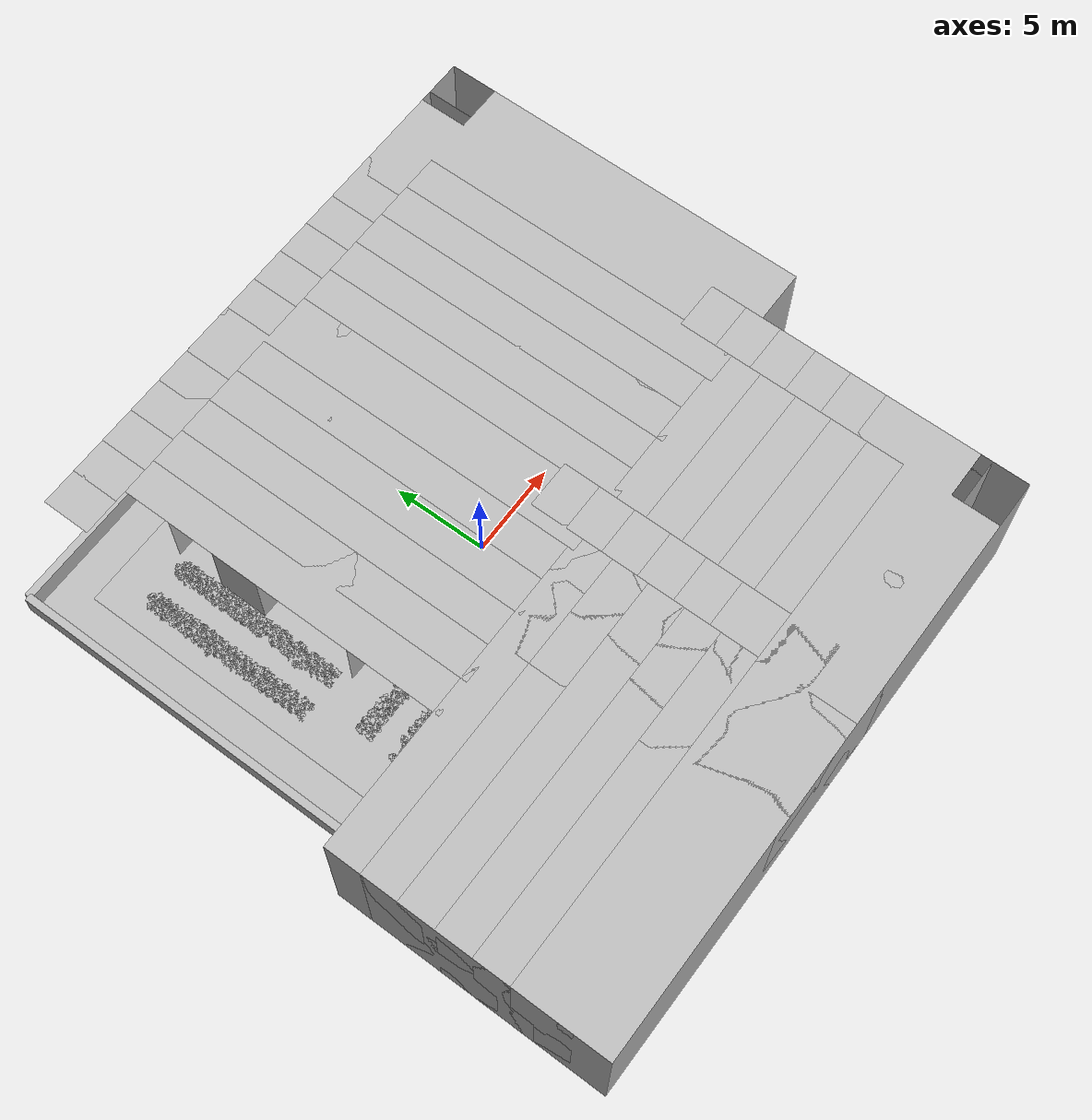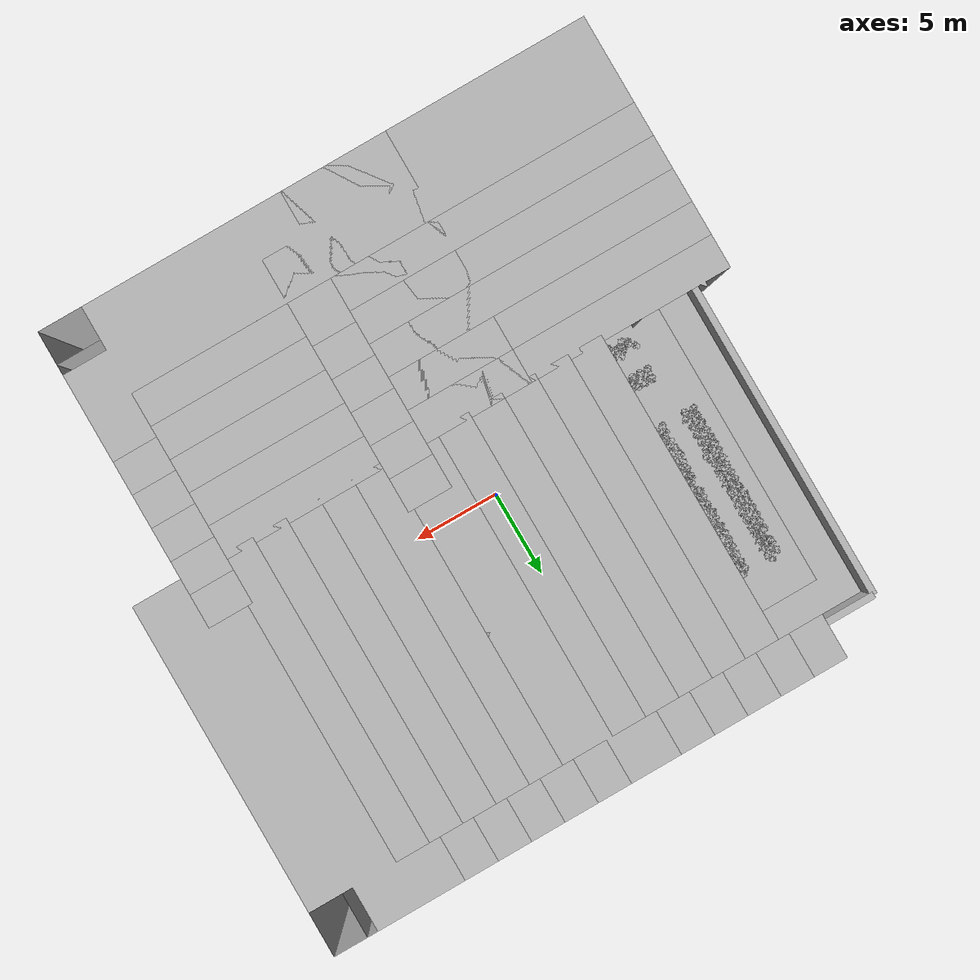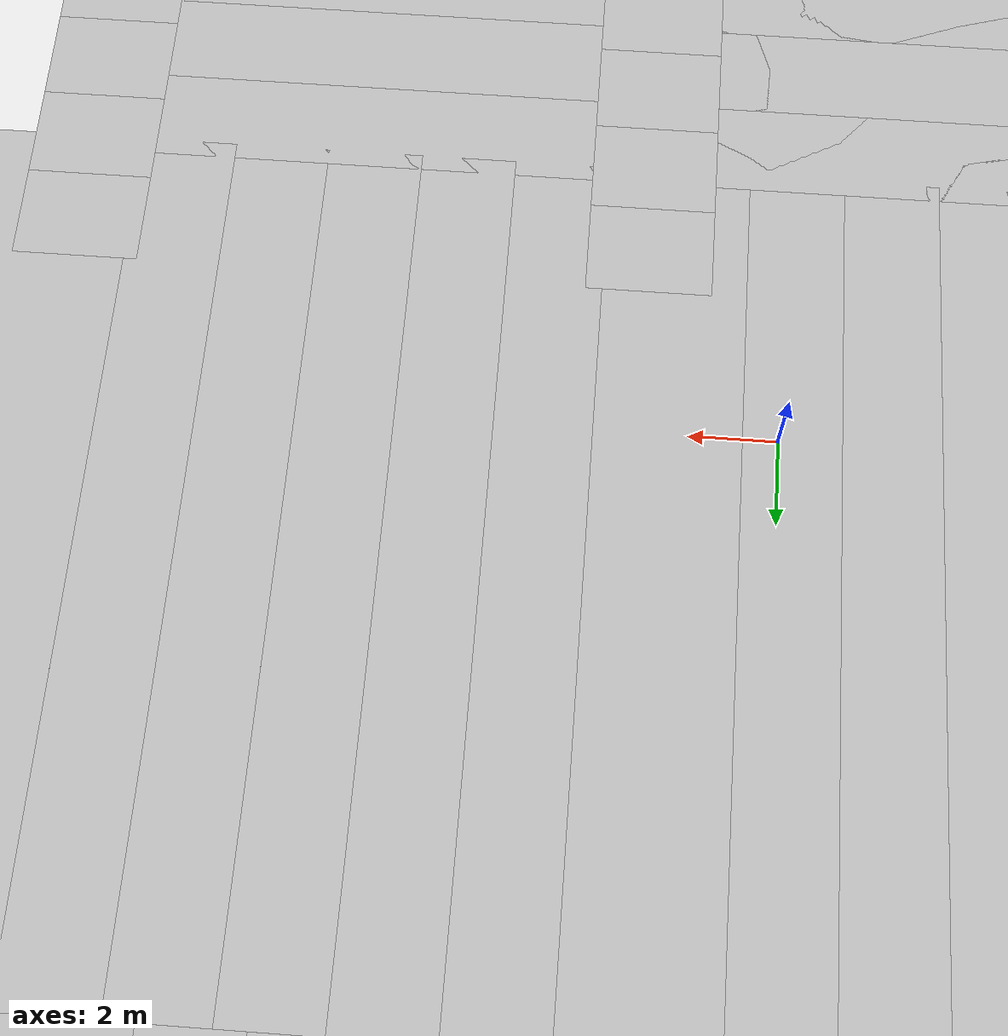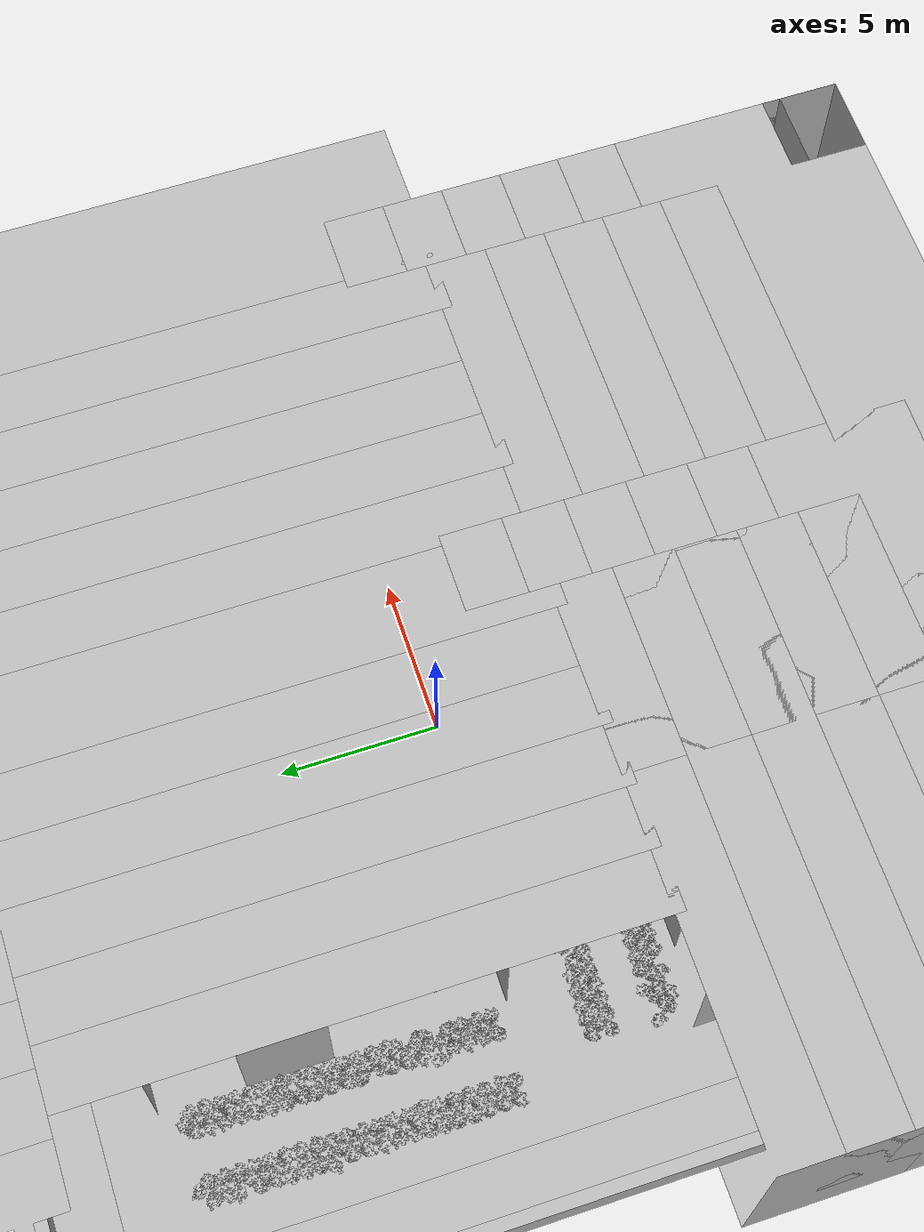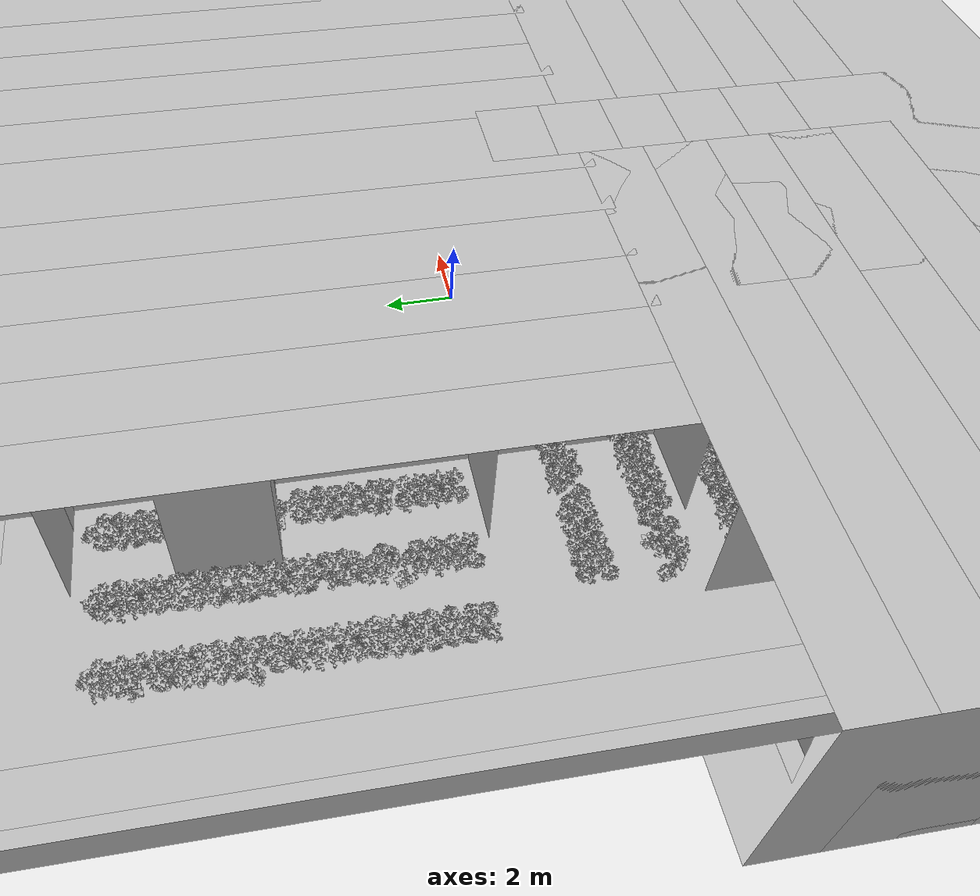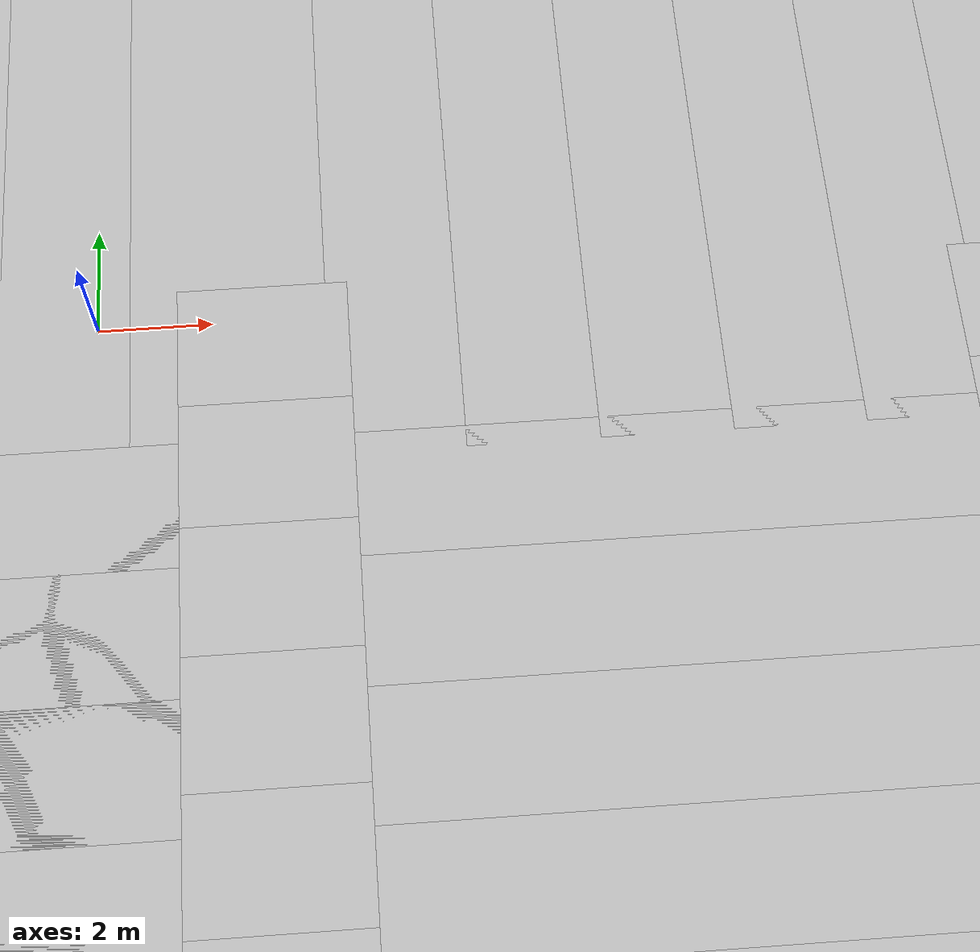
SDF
<?xml version="1.0"?>
<!-- Generated by generate_strawberry_farm.py - pinwheel field + plants. -->
<sdf version="1.6">
  <world name="strawberry_farm">
    <include><uri>model://sun</uri></include>
    <include><uri>model://grass_ground</uri><pose>0 0 -0.01 0 0 0</pose></include>
    <include><uri>model://soil_ground</uri></include>
    <include><uri>model://hedge</uri><name>hedge_n</name><pose>0  15 0 0 0 0</pose></include>
    <include><uri>model://hedge</uri><name>hedge_s</name><pose>0 -15 0 0 0 0</pose></include>
    <include><uri>model://hedge</uri><name>hedge_e</name><pose>15 0 0 0 0 1.5708</pose></include>
    <include><uri>model://hedge</uri><name>hedge_w</name><pose>-15 0 0 0 0 1.5708</pose></include>
    <physics type="ode">
      <max_step_size>0.001</max_step_size>
      <real_time_update_rate>1000</real_time_update_rate>
    </physics>
    <include><uri>model://bed</uri><name>bed_q1_0</name><pose>1.500 6.000 0 0 0 1.5708</pose></include>
    <include><uri>model://bed</uri><name>bed_q2_0</name><pose>-1.500 6.000 0 0 0 1.5708</pose></include>
    <include><uri>model://bed</uri><name>bed_q4_0</name><pose>6.000 -1.500 0 0 0 0.0000</pose></include>
    <include><uri>model://bed</uri><name>bed_q3_0</name><pose>-6.000 -1.500 0 0 0 0.0000</pose></include>
    <include><uri>model://bed</uri><name>bed_q1_1</name><pose>3.500 6.000 0 0 0 1.5708</pose></include>
    <include><uri>model://bed</uri><name>bed_q2_1</name><pose>-3.500 6.000 0 0 0 1.5708</pose></include>
    <include><uri>model://bed</uri><name>bed_q4_1</name><pose>6.000 -3.500 0 0 0 0.0000</pose></include>
    <include><uri>model://bed</uri><name>bed_q3_1</name><pose>-6.000 -3.500 0 0 0 0.0000</pose></include>
    <include><uri>model://bed</uri><name>bed_q1_2</name><pose>5.500 6.000 0 0 0 1.5708</pose></include>
    <include><uri>model://bed</uri><name>bed_q2_2</name><pose>-5.500 6.000 0 0 0 1.5708</pose></include>
    <include><uri>model://bed</uri><name>bed_q4_2</name><pose>6.000 -5.500 0 0 0 0.0000</pose></include>
    <include><uri>model://bed</uri><name>bed_q3_2</name><pose>-6.000 -5.500 0 0 0 0.0000</pose></include>
    <include><uri>model://bed</uri><name>bed_q1_3</name><pose>7.500 6.000 0 0 0 1.5708</pose></include>
    <include><uri>model://bed</uri><name>bed_q2_3</name><pose>-7.500 6.000 0 0 0 1.5708</pose></include>
    <include><uri>model://bed</uri><name>bed_q4_3</name><pose>6.000 -7.500 0 0 0 0.0000</pose></include>
    <include><uri>model://bed</uri><name>bed_q3_3</name><pose>-6.000 -7.500 0 0 0 0.0000</pose></include>
    <include><uri>model://bed</uri><name>bed_q1_4</name><pose>9.500 6.000 0 0 0 1.5708</pose></include>
    <include><uri>model://bed</uri><name>bed_q2_4</name><pose>-9.500 6.000 0 0 0 1.5708</pose></include>
    <include><uri>model://bed</uri><name>bed_q4_4</name><pose>6.000 -9.500 0 0 0 0.0000</pose></include>
    <include><uri>model://bed</uri><name>bed_q3_4</name><pose>-6.000 -9.500 0 0 0 0.0000</pose></include>
    <include><uri>model://bed</uri><name>bed_q1_5</name><pose>11.500 6.000 0 0 0 1.5708</pose></include>
    <include><uri>model://bed</uri><name>bed_q2_5</name><pose>-11.500 6.000 0 0 0 1.5708</pose></include>
    <include><uri>model://bed</uri><name>bed_q4_5</name><pose>6.000 -11.500 0 0 0 0.0000</pose></include>
    <include><uri>model://bed</uri><name>bed_q3_5</name><pose>-6.000 -11.500 0 0 0 0.0000</pose></include>
    <include><uri>model://strawberry_ripe</uri><name>bed_q1_0_p0_0</name><pose>1.780 1.350 0.4 0 0 0.0000</pose></include>
    <include><uri>model://strawberry_ripe</uri><name>bed_q1_0_p0_1</name><pose>1.780 1.800 0.4 0 0 0.7854</pose></include>
    <include><uri>model://strawberry_ripe</uri><name>bed_q1_0_p0_2</name><pose>1.780 2.250 0.4 0 0 1.5708</pose></include>
    <include><uri>model://strawberry_ripe</uri><name>bed_q1_0_p0_3</name><pose>1.780 2.700 0.4 0 0 2.3562</pose></include>
    <include><uri>model://strawberry_ripe</uri><name>bed_q1_0_p0_4</name><pose>1.780 3.150 0.4 0 0 3.1416</pose></include>
    <include><uri>model://strawberry_ripe</uri><name>bed_q1_0_p0_5</name><pose>1.780 3.600 0.4 0 0 3.9270</pose></include>
    <include><uri>model://strawberry_flower</uri><name>bed_q1_0_p0_6</name><pose>1.780 4.050 0.4 0 0 0.0000</pose></include>
    <include><uri>model://strawberry_ripe</uri><name>bed_q1_0_p0_7</name><pose>1.780 4.500 0.4 0 0 4.7124</pose></include>
    <include><uri>model://strawberry_ripe</uri><name>bed_q1_0_p0_8</name><pose>1.780 4.950 0.4 0 0 5.4978</pose></include>
    <include><uri>model://strawberry_ripe</uri><name>bed_q1_0_p0_9</name><pose>1.780 5.400 0.4 0 0 0.0000</pose></include>
    <include><uri>model://strawberry_ripe</uri><name>bed_q1_0_p0_10</name><pose>1.780 5.850 0.4 0 0 0.7854</pose></include>
    <include><uri>model://strawberry_ripe</uri><name>bed_q1_0_p0_11</name><pose>1.780 6.300 0.4 0 0 1.5708</pose></include>
    <include><uri>model://strawberry_ripe</uri><name>bed_q1_0_p0_12</name><pose>1.780 6.750 0.4 0 0 2.3562</pose></include>
    <include><uri>model://strawberry_ripe</uri><name>bed_q1_0_p0_13</name><pose>1.780 7.200 0.4 0 0 3.1416</pose></include>
    <include><uri>model://strawberry_ripe</uri><name>bed_q1_0_p0_14</name><pose>1.780 7.650 0.4 0 0 3.9270</pose></include>
    <include><uri>model://strawberry_ripe</uri><name>bed_q1_0_p0_15</name><pose>1.780 8.100 0.4 0 0 4.7124</pose></include>
    <include><uri>model://strawberry_ripe</uri><name>bed_q1_0_p0_16</name><pose>1.780 8.550 0.4 0 0 5.4978</pose></include>
    <include><uri>model://strawberry_ripe</uri><name>bed_q1_0_p0_17</name><pose>1.780 9.000 0.4 0 0 0.0000</pose></include>
    <include><uri>model://strawberry_unripe</uri><name>bed_q1_0_p0_18</name><pose>1.780 9.450 0.4 0 0 0.0000</pose></include>
    <include><uri>model://strawberry_ripe</uri><name>bed_q1_0_p0_19</name><pose>1.780 9.900 0.4 0 0 0.7854</pose></include>
    <include><uri>model://strawberry_unripe</uri><name>bed_q1_0_p0_20</name><pose>1.780 10.350 0.4 0 0 0.7854</pose></include>
    <include><uri>model://strawberry_ripe</uri><name>bed_q1_0_p1_0</name><pose>1.500 1.575 0.4 0 0 1.5708</pose></include>
    <include><uri>model://strawberry_ripe</uri><name>bed_q1_0_p1_1</name><pose>1.500 2.025 0.4 0 0 2.3562</pose></include>
    <include><uri>model://strawberry_ripe</uri><name>bed_q1_0_p1_2</name><pose>1.500 2.475 0.4 0 0 3.1416</pose></include>
    <include><uri>model://strawberry_leafscorch</uri><name>bed_q1_0_p1_3</name><pose>1.500 2.925 0.4 0 0 0.0000</pose></include>
    <include><uri>model://strawberry_ripe</uri><name>bed_q1_0_p1_4</name><pose>1.500 3.375 0.4 0 0 3.9270</pose></include>
    <include><uri>model://strawberry_ripe</uri><name>bed_q1_0_p1_5</name><pose>1.500 3.825 0.4 0 0 4.7124</pose></include>
    <include><uri>model://strawberry_ripe</uri><name>bed_q1_0_p1_6</name><pose>1.500 4.275 0.4 0 0 5.4978</pose></include>
    <include><uri>model://strawberry_unripe</uri><name>bed_q1_0_p1_7</name><pose>1.500 4.725 0.4 0 0 1.5708</pose></include>
    <include><uri>model://strawberry_ripe</uri><name>bed_q1_0_p1_8</name><pose>1.500 5.175 0.4 0 0 0.0000</pose></include>
    <include><uri>model://strawberry_unripe</uri><name>bed_q1_0_p1_9</name><pose>1.500 5.625 0.4 0 0 2.3562</pose></include>
    <include><uri>model://strawberry_ripe</uri><name>bed_q1_0_p1_10</name><pose>1.500 6.075 0.4 0 0 0.7854</pose></include>
    <include><uri>model://strawberry_ripe</uri><name>bed_q1_0_p1_11</name><pose>1.500 6.525 0.4 0 0 1.5708</pose></include>
    <include><uri>model://strawberry_leafscorch</uri><name>bed_q1_0_p1_12</name><pose>1.500 6.975 0.4 0 0 0.7854</pose></include>
    <include><uri>model://strawberry_ripe</uri><name>bed_q1_0_p1_13</name><pose>1.500 7.425 0.4 0 0 2.3562</pose></include>
    <include><uri>model://strawberry_ripe</uri><name>bed_q1_0_p1_14</name><pose>1.500 7.875 0.4 0 0 3.1416</pose></include>
    <include><uri>model://strawberry_unripe</uri><name>bed_q1_0_p1_15</name><pose>1.500 8.325 0.4 0 0 3.1416</pose></include>
    <include><uri>model://strawberry_ripe</uri><name>bed_q1_0_p1_16</name><pose>1.500 8.775 0.4 0 0 3.9270</pose></include>
    <include><uri>model://strawberry_flower</uri><name>bed_q1_0_p1_17</name><pose>1.500 9.225 0.4 0 0 0.7854</pose></include>
    <include><uri>model://strawberry_ripe</uri><name>bed_q1_0_p1_18</name><pose>1.500 9.675 0.4 0 0 4.7124</pose></include>
    <include><uri>model://strawberry_ripe</uri><name>bed_q1_0_p1_19</name><pose>1.500 10.125 0.4 0 0 5.4978</pose></include>
    <include><uri>model://strawberry_ripe</uri><name>bed_q1_0_p1_20</name><pose>1.500 10.575 0.4 0 0 0.0000</pose></include>
    <include><uri>model://strawberry_ripe</uri><name>bed_q1_0_p2_0</name><pose>1.220 1.350 0.4 0 0 0.7854</pose></include>
    <include><uri>model://strawberry_ripe</uri><name>bed_q1_0_p2_1</name><pose>1.220 1.800 0.4 0 0 1.5708</pose></include>
    <include><uri>model://strawberry_ripe</uri><name>bed_q1_0_p2_2</name><pose>1.220 2.250 0.4 0 0 2.3562</pose></include>
    <include><uri>model://strawberry_ripe</uri><name>bed_q1_0_p2_3</name><pose>1.220 2.700 0.4 0 0 3.1416</pose></include>
    <include><uri>model://strawberry_ripe</uri><name>bed_q1_0_p2_4</name><pose>1.220 3.150 0.4 0 0 3.9270</pose></include>
    <include><uri>model://strawberry_ripe</uri><name>bed_q1_0_p2_5</name><pose>1.220 3.600 0.4 0 0 4.7124</pose></include>
    <include><uri>model://strawberry_ripe</uri><name>bed_q1_0_p2_6</name><pose>1.220 4.050 0.4 0 0 5.4978</pose></include>
    <include><uri>model://strawberry_ripe</uri><name>bed_q1_0_p2_7</name><pose>1.220 4.500 0.4 0 0 0.0000</pose></include>
    <include><uri>model://strawberry_ripe</uri><name>bed_q1_0_p2_8</name><pose>1.220 4.950 0.4 0 0 0.7854</pose></include>
    <include><uri>model://strawberry_ripe</uri><name>bed_q1_0_p2_9</name><pose>1.220 5.400 0.4 0 0 1.5708</pose></include>
    <include><uri>model://strawberry_ripe</uri><name>bed_q1_0_p2_10</name><pose>1.220 5.850 0.4 0 0 2.3562</pose></include>
    <include><uri>model://strawberry_mildew</uri><name>bed_q1_0_p2_11</name><pose>1.220 6.300 0.4 0 0 0.0000</pose></include>
    <include><uri>model://strawberry_ripe</uri><name>bed_q1_0_p2_12</name><pose>1.220 6.750 0.4 0 0 3.1416</pose></include>
    <include><uri>model://strawberry_ripe</uri><name>bed_q1_0_p2_13</name><pose>1.220 7.200 0.4 0 0 3.9270</pose></include>
    <include><uri>model://strawberry_ripe</uri><name>bed_q1_0_p2_14</name><pose>1.220 7.650 0.4 0 0 4.7124</pose></include>
    <include><uri>model://strawberry_ripe</uri><name>bed_q1_0_p2_15</name><pose>1.220 8.100 0.4 0 0 5.4978</pose></include>
    <include><uri>model://strawberry_ripe</uri><name>bed_q1_0_p2_16</name><pose>1.220 8.550 0.4 0 0 0.0000</pose></include>
    <include><uri>model://strawberry_ripe</uri><name>bed_q1_0_p2_17</name><pose>1.220 9.000 0.4 0 0 0.7854</pose></include>
    <include><uri>model://strawberry_leafscorch</uri><name>bed_q1_0_p2_18</name><pose>1.220 9.450 0.4 0 0 1.5708</pose></include>
    <include><uri>model://strawberry_ripe</uri><name>bed_q1_0_p2_19</name><pose>1.220 9.900 0.4 0 0 1.5708</pose></include>
    <include><uri>model://strawberry_ripe</uri><name>bed_q1_0_p2_20</name><pose>1.220 10.350 0.4 0 0 2.3562</pose></include>
    <include><uri>model://strawberry_ripe</uri><name>bed_q2_0_p0_0</name><pose>-1.220 1.350 0.4 0 0 3.1416</pose></include>
    <include><uri>model://strawberry_unripe</uri><name>bed_q2_0_p0_1</name><pose>-1.220 1.800 0.4 0 0 3.9270</pose></include>
    <include><uri>model://strawberry_halfripe</uri><name>bed_q2_0_p0_2</name><pose>-1.220 2.250 0.4 0 0 0.0000</pose></include>
    <include><uri>model://strawberry_ripe</uri><name>bed_q2_0_p0_3</name><pose>-1.220 2.700 0.4 0 0 3.9270</pose></include>
    <include><uri>model://strawberry_ripe</uri><name>bed_q2_0_p0_4</name><pose>-1.220 3.150 0.4 0 0 4.7124</pose></include>
    <include><uri>model://strawberry_ripe</uri><name>bed_q2_0_p0_5</name><pose>-1.220 3.600 0.4 0 0 5.4978</pose></include>
    <include><uri>model://strawberry_ripe</uri><name>bed_q2_0_p0_6</name><pose>-1.220 4.050 0.4 0 0 0.0000</pose></include>
    <include><uri>model://strawberry_ripe</uri><name>bed_q2_0_p0_7</name><pose>-1.220 4.500 0.4 0 0 0.7854</pose></include>
    <include><uri>model://strawberry_mildew</uri><name>bed_q2_0_p0_8</name><pose>-1.220 4.950 0.4 0 0 0.7854</pose></include>
    <include><uri>model://strawberry_flower</uri><name>bed_q2_0_p0_9</name><pose>-1.220 5.400 0.4 0 0 1.5708</pose></include>
    <include><uri>model://strawberry_ripe</uri><name>bed_q2_0_p0_10</name><pose>-1.220 5.850 0.4 0 0 1.5708</pose></include>
    <include><uri>model://strawberry_ripe</uri><name>bed_q2_0_p0_11</name><pose>-1.220 6.300 0.4 0 0 2.3562</pose></include>
    <include><uri>model://strawberry_ripe</uri><name>bed_q2_0_p0_12</name><pose>-1.220 6.750 0.4 0 0 3.1416</pose></include>
    <include><uri>model://strawberry_mildew</uri><name>bed_q2_0_p0_13</name><pose>-1.220 7.200 0.4 0 0 1.5708</pose></include>
    <include><uri>model://strawberry_ripe</uri><name>bed_q2_0_p0_14</name><pose>-1.220 7.650 0.4 0 0 3.9270</pose></include>
    <include><uri>model://strawberry_ripe</uri><name>bed_q2_0_p0_15</name><pose>-1.220 8.100 0.4 0 0 4.7124</pose></include>
    <include><uri>model://strawberry_ripe</uri><name>bed_q2_0_p0_16</name><pose>-1.220 8.550 0.4 0 0 5.4978</pose></include>
    <include><uri>model://strawberry_ripe</uri><name>bed_q2_0_p0_17</name><pose>-1.220 9.000 0.4 0 0 0.0000</pose></include>
    <include><uri>model://strawberry_ripe</uri><name>bed_q2_0_p0_18</name><pose>-1.220 9.450 0.4 0 0 0.7854</pose></include>
    <include><uri>model://strawberry_ripe</uri><name>bed_q2_0_p0_19</name><pose>-1.220 9.900 0.4 0 0 1.5708</pose></include>
    <include><uri>model://strawberry_flower</uri><name>bed_q2_0_p0_20</name><pose>-1.220 10.350 0.4 0 0 2.3562</pose></include>
    <include><uri>model://strawberry_ripe</uri><name>bed_q2_0_p1_0</name><pose>-1.500 1.575 0.4 0 0 2.3562</pose></include>
    <include><uri>model://strawberry_ripe</uri><name>bed_q2_0_p1_1</name><pose>-1.500 2.025 0.4 0 0 3.1416</pose></include>
    <include><uri>model://strawberry_leafscorch</uri><name>bed_q2_0_p1_2</name><pose>-1.500 2.475 0.4 0 0 2.3562</pose></include>
    <include><uri>model://strawberry_ripe</uri><name>bed_q2_0_p1_3</name><pose>-1.500 2.925 0.4 0 0 3.9270</pose></include>
    <include><uri>model://strawberry_ripe</uri><name>bed_q2_0_p1_4</name><pose>-1.500 3.375 0.4 0 0 4.7124</pose></include>
    <include><uri>model://strawberry_ripe</uri><name>bed_q2_0_p1_5</name><pose>-1.500 3.825 0.4 0 0 5.4978</pose></include>
    <include><uri>model://strawberry_ripe</uri><name>bed_q2_0_p1_6</name><pose>-1.500 4.275 0.4 0 0 0.0000</pose></include>
    <include><uri>model://strawberry_ripe</uri><name>bed_q2_0_p1_7</name><pose>-1.500 4.725 0.4 0 0 0.7854</pose></include>
    <include><uri>model://strawberry_halfripe</uri><name>bed_q2_0_p1_8</name><pose>-1.500 5.175 0.4 0 0 0.7854</pose></include>
    <include><uri>model://strawberry_ripe</uri><name>bed_q2_0_p1_9</name><pose>-1.500 5.625 0.4 0 0 1.5708</pose></include>
    <include><uri>model://strawberry_ripe</uri><name>bed_q2_0_p1_10</name><pose>-1.500 6.075 0.4 0 0 2.3562</pose></include>
    <include><uri>model://strawberry_ripe</uri><name>bed_q2_0_p1_11</name><pose>-1.500 6.525 0.4 0 0 3.1416</pose></include>
    <include><uri>model://strawberry_leafscorch</uri><name>bed_q2_0_p1_12</name><pose>-1.500 6.975 0.4 0 0 3.1416</pose></include>
    <include><uri>model://strawberry_ripe</uri><name>bed_q2_0_p1_13</name><pose>-1.500 7.425 0.4 0 0 3.9270</pose></include>
    <include><uri>model://strawberry_leafscorch</uri><name>bed_q2_0_p1_14</name><pose>-1.500 7.875 0.4 0 0 3.9270</pose></include>
    <include><uri>model://strawberry_flower</uri><name>bed_q2_0_p1_15</name><pose>-1.500 8.325 0.4 0 0 3.1416</pose></include>
    <include><uri>model://strawberry_ripe</uri><name>bed_q2_0_p1_16</name><pose>-1.500 8.775 0.4 0 0 4.7124</pose></include>
    <include><uri>model://strawberry_ripe</uri><name>bed_q2_0_p1_17</name><pose>-1.500 9.225 0.4 0 0 5.4978</pose></include>
    <include><uri>model://strawberry_ripe</uri><name>bed_q2_0_p1_18</name><pose>-1.500 9.675 0.4 0 0 0.0000</pose></include>
    <include><uri>model://strawberry_ripe</uri><name>bed_q2_0_p1_19</name><pose>-1.500 10.125 0.4 0 0 0.7854</pose></include>
    <include><uri>model://strawberry_ripe</uri><name>bed_q2_0_p1_20</name><pose>-1.500 10.575 0.4 0 0 1.5708</pose></include>
    <include><uri>model://strawberry_ripe</uri><name>bed_q2_0_p2_0</name><pose>-1.780 1.350 0.4 0 0 2.3562</pose></include>
    <include><uri>model://strawberry_ripe</uri><name>bed_q2_0_p2_1</name><pose>-1.780 1.800 0.4 0 0 3.1416</pose></include>
    <include><uri>model://strawberry_ripe</uri><name>bed_q2_0_p2_2</name><pose>-1.780 2.250 0.4 0 0 3.9270</pose></include>
    <include><uri>model://strawberry_ripe</uri><name>bed_q2_0_p2_3</name><pose>-1.780 2.700 0.4 0 0 4.7124</pose></include>
    <include><uri>model://strawberry_leafscorch</uri><name>bed_q2_0_p2_4</name><pose>-1.780 3.150 0.4 0 0 4.7124</pose></include>
    <include><uri>model://strawberry_flower</uri><name>bed_q2_0_p2_5</name><pose>-1.780 3.600 0.4 0 0 3.9270</pose></include>
    <include><uri>model://strawberry_ripe</uri><name>bed_q2_0_p2_6</name><pose>-1.780 4.050 0.4 0 0 5.4978</pose></include>
    <include><uri>model://strawberry_ripe</uri><name>bed_q2_0_p2_7</name><pose>-1.780 4.500 0.4 0 0 6.2832</pose></include>
    <include><uri>model://strawberry_ripe</uri><name>bed_q2_0_p2_8</name><pose>-1.780 4.950 0.4 0 0 0.7854</pose></include>
    <include><uri>model://strawberry_mildew</uri><name>bed_q2_0_p2_9</name><pose>-1.780 5.400 0.4 0 0 2.3562</pose></include>
    <include><uri>model://strawberry_flower</uri><name>bed_q2_0_p2_10</name><pose>-1.780 5.850 0.4 0 0 4.7124</pose></include>
    <include><uri>model://strawberry_ripe</uri><name>bed_q2_0_p2_11</name><pose>-1.780 6.300 0.4 0 0 1.5708</pose></include>
    <include><uri>model://strawberry_ripe</uri><name>bed_q2_0_p2_12</name><pose>-1.780 6.750 0.4 0 0 2.3562</pose></include>
    <include><uri>model://strawberry_ripe</uri><name>bed_q2_0_p2_13</name><pose>-1.780 7.200 0.4 0 0 3.1416</pose></include>
    <include><uri>model://strawberry_ripe</uri><name>bed_q2_0_p2_14</name><pose>-1.780 7.650 0.4 0 0 3.9270</pose></include>
    <include><uri>model://strawberry_halfripe</uri><name>bed_q2_0_p2_15</name><pose>-1.780 8.100 0.4 0 0 1.5708</pose></include>
    <include><uri>model://strawberry_ripe</uri><name>bed_q2_0_p2_16</name><pose>-1.780 8.550 0.4 0 0 4.7124</pose></include>
    <include><uri>model://strawberry_halfripe</uri><name>bed_q2_0_p2_17</name><pose>-1.780 9.000 0.4 0 0 2.3562</pose></include>
    <include><uri>model://strawberry_ripe</uri><name>bed_q2_0_p2_18</name><pose>-1.780 9.450 0.4 0 0 5.4978</pose></include>
    <include><uri>model://strawberry_ripe</uri><name>bed_q2_0_p2_19</name><pose>-1.780 9.900 0.4 0 0 0.0000</pose></include>
    <include><uri>model://strawberry_ripe</uri><name>bed_q2_0_p2_20</name><pose>-1.780 10.350 0.4 0 0 0.7854</pose></include>
    <include><uri>model://strawberry_ripe</uri><name>bed_q4_0_p0_0</name><pose>1.350 -1.780 0.4 0 0 1.5708</pose></include>
    <include><uri>model://strawberry_mildew</uri><name>bed_q4_0_p0_1</name><pose>1.800 -1.780 0.4 0 0 3.1416</pose></include>
    <include><uri>model://strawberry_flower</uri><name>bed_q4_0_p0_2</name><pose>2.250 -1.780 0.4 0 0 5.4978</pose></include>
    <include><uri>model://strawberry_unripe</uri><name>bed_q4_0_p0_3</name><pose>2.700 -1.780 0.4 0 0 4.7124</pose></include>
    <include><uri>model://strawberry_ripe</uri><name>bed_q4_0_p0_4</name><pose>3.150 -1.780 0.4 0 0 2.3562</pose></include>
    <include><uri>model://strawberry_ripe</uri><name>bed_q4_0_p0_5</name><pose>3.600 -1.780 0.4 0 0 3.1416</pose></include>
    <include><uri>model://strawberry_flower</uri><name>bed_q4_0_p0_6</name><pose>4.050 -1.780 0.4 0 0 0.0000</pose></include>
    <include><uri>model://strawberry_mildew</uri><name>bed_q4_0_p0_7</name><pose>4.500 -1.780 0.4 0 0 3.9270</pose></include>
    <include><uri>model://strawberry_ripe</uri><name>bed_q4_0_p0_8</name><pose>4.950 -1.780 0.4 0 0 3.9270</pose></include>
    <include><uri>model://strawberry_ripe</uri><name>bed_q4_0_p0_9</name><pose>5.400 -1.780 0.4 0 0 4.7124</pose></include>
    <include><uri>model://strawberry_ripe</uri><name>bed_q4_0_p0_10</name><pose>5.850 -1.780 0.4 0 0 5.4978</pose></include>
    <include><uri>model://strawberry_halfripe</uri><name>bed_q4_0_p0_11</name><pose>6.300 -1.780 0.4 0 0 3.1416</pose></include>
    <include><uri>model://strawberry_halfripe</uri><name>bed_q4_0_p0_12</name><pose>6.750 -1.780 0.4 0 0 3.9270</pose></include>
    <include><uri>model://strawberry_ripe</uri><name>bed_q4_0_p0_13</name><pose>7.200 -1.780 0.4 0 0 0.0000</pose></include>
    <include><uri>model://strawberry_ripe</uri><name>bed_q4_0_p0_14</name><pose>7.650 -1.780 0.4 0 0 0.7854</pose></include>
    <include><uri>model://strawberry_ripe</uri><name>bed_q4_0_p0_15</name><pose>8.100 -1.780 0.4 0 0 1.5708</pose></include>
    <include><uri>model://strawberry_ripe</uri><name>bed_q4_0_p0_16</name><pose>8.550 -1.780 0.4 0 0 2.3562</pose></include>
    <include><uri>model://strawberry_flower</uri><name>bed_q4_0_p0_17</name><pose>9.000 -1.780 0.4 0 0 0.7854</pose></include>
    <include><uri>model://strawberry_ripe</uri><name>bed_q4_0_p0_18</name><pose>9.450 -1.780 0.4 0 0 3.1416</pose></include>
    <include><uri>model://strawberry_ripe</uri><name>bed_q4_0_p0_19</name><pose>9.900 -1.780 0.4 0 0 3.9270</pose></include>
    <include><uri>model://strawberry_ripe</uri><name>bed_q4_0_p0_20</name><pose>10.350 -1.780 0.4 0 0 4.7124</pose></include>
    <include><uri>model://strawberry_ripe</uri><name>bed_q4_0_p1_0</name><pose>1.575 -1.500 0.4 0 0 5.4978</pose></include>
    <include><uri>model://strawberry_ripe</uri><name>bed_q4_0_p1_1</name><pose>2.025 -1.500 0.4 0 0 0.0000</pose></include>
    <include><uri>model://strawberry_ripe</uri><name>bed_q4_0_p1_2</name><pose>2.475 -1.500 0.4 0 0 0.7854</pose></include>
    <include><uri>model://strawberry_leafscorch</uri><name>bed_q4_0_p1_3</name><pose>2.925 -1.500 0.4 0 0 5.4978</pose></include>
    <include><uri>model://strawberry_ripe</uri><name>bed_q4_0_p1_4</name><pose>3.375 -1.500 0.4 0 0 1.5708</pose></include>
    <include><uri>model://strawberry_ripe</uri><name>bed_q4_0_p1_5</name><pose>3.825 -1.500 0.4 0 0 2.3562</pose></include>
    <include><uri>model://strawberry_ripe</uri><name>bed_q4_0_p1_6</name><pose>4.275 -1.500 0.4 0 0 3.1416</pose></include>
    <include><uri>model://strawberry_ripe</uri><name>bed_q4_0_p1_7</name><pose>4.725 -1.500 0.4 0 0 3.9270</pose></include>
    <include><uri>model://strawberry_ripe</uri><name>bed_q4_0_p1_8</name><pose>5.175 -1.500 0.4 0 0 4.7124</pose></include>
    <include><uri>model://strawberry_ripe</uri><name>bed_q4_0_p1_9</name><pose>5.625 -1.500 0.4 0 0 5.4978</pose></include>
    <include><uri>model://strawberry_ripe</uri><name>bed_q4_0_p1_10</name><pose>6.075 -1.500 0.4 0 0 6.2832</pose></include>
    <include><uri>model://strawberry_ripe</uri><name>bed_q4_0_p1_11</name><pose>6.525 -1.500 0.4 0 0 0.7854</pose></include>
    <include><uri>model://strawberry_ripe</uri><name>bed_q4_0_p1_12</name><pose>6.975 -1.500 0.4 0 0 1.5708</pose></include>
    <include><uri>model://strawberry_ripe</uri><name>bed_q4_0_p1_13</name><pose>7.425 -1.500 0.4 0 0 2.3562</pose></include>
    <include><uri>model://strawberry_ripe</uri><name>bed_q4_0_p1_14</name><pose>7.875 -1.500 0.4 0 0 3.1416</pose></include>
    <include><uri>model://strawberry_ripe</uri><name>bed_q4_0_p1_15</name><pose>8.325 -1.500 0.4 0 0 3.9270</pose></include>
    <include><uri>model://strawberry_mildew</uri><name>bed_q4_0_p1_16</name><pose>8.775 -1.500 0.4 0 0 4.7124</pose></include>
    <include><uri>model://strawberry_flower</uri><name>bed_q4_0_p1_17</name><pose>9.225 -1.500 0.4 0 0 1.5708</pose></include>
    <include><uri>model://strawberry_ripe</uri><name>bed_q4_0_p1_18</name><pose>9.675 -1.500 0.4 0 0 4.7124</pose></include>
    <include><uri>model://strawberry_ripe</uri><name>bed_q4_0_p1_19</name><pose>10.125 -1.500 0.4 0 0 5.4978</pose></include>
    <include><uri>model://strawberry_ripe</uri><name>bed_q4_0_p1_20</name><pose>10.575 -1.500 0.4 0 0 0.0000</pose></include>
    <include><uri>model://strawberry_ripe</uri><name>bed_q4_0_p2_0</name><pose>1.350 -1.220 0.4 0 0 0.7854</pose></include>
    <include><uri>model://strawberry_ripe</uri><name>bed_q4_0_p2_1</name><pose>1.800 -1.220 0.4 0 0 1.5708</pose></include>
    <include><uri>model://strawberry_mildew</uri><name>bed_q4_0_p2_2</name><pose>2.250 -1.220 0.4 0 0 5.4978</pose></include>
    <include><uri>model://strawberry_ripe</uri><name>bed_q4_0_p2_3</name><pose>2.700 -1.220 0.4 0 0 2.3562</pose></include>
    <include><uri>model://strawberry_ripe</uri><name>bed_q4_0_p2_4</name><pose>3.150 -1.220 0.4 0 0 3.1416</pose></include>
    <include><uri>model://strawberry_halfripe</uri><name>bed_q4_0_p2_5</name><pose>3.600 -1.220 0.4 0 0 4.7124</pose></include>
    <include><uri>model://strawberry_unripe</uri><name>bed_q4_0_p2_6</name><pose>4.050 -1.220 0.4 0 0 5.4978</pose></include>
    <include><uri>model://strawberry_ripe</uri><name>bed_q4_0_p2_7</name><pose>4.500 -1.220 0.4 0 0 3.9270</pose></include>
    <include><uri>model://strawberry_ripe</uri><name>bed_q4_0_p2_8</name><pose>4.950 -1.220 0.4 0 0 4.7124</pose></include>
    <include><uri>model://strawberry_ripe</uri><name>bed_q4_0_p2_9</name><pose>5.400 -1.220 0.4 0 0 5.4978</pose></include>
    <include><uri>model://strawberry_ripe</uri><name>bed_q4_0_p2_10</name><pose>5.850 -1.220 0.4 0 0 0.0000</pose></include>
    <include><uri>model://strawberry_ripe</uri><name>bed_q4_0_p2_11</name><pose>6.300 -1.220 0.4 0 0 0.7854</pose></include>
    <include><uri>model://strawberry_ripe</uri><name>bed_q4_0_p2_12</name><pose>6.750 -1.220 0.4 0 0 1.5708</pose></include>
    <include><uri>model://strawberry_ripe</uri><name>bed_q4_0_p2_13</name><pose>7.200 -1.220 0.4 0 0 2.3562</pose></include>
    <include><uri>model://strawberry_leafscorch</uri><name>bed_q4_0_p2_14</name><pose>7.650 -1.220 0.4 0 0 0.0000</pose></include>
    <include><uri>model://strawberry_ripe</uri><name>bed_q4_0_p2_15</name><pose>8.100 -1.220 0.4 0 0 3.1416</pose></include>
    <include><uri>model://strawberry_ripe</uri><name>bed_q4_0_p2_16</name><pose>8.550 -1.220 0.4 0 0 3.9270</pose></include>
    <include><uri>model://strawberry_ripe</uri><name>bed_q4_0_p2_17</name><pose>9.000 -1.220 0.4 0 0 4.7124</pose></include>
    <include><uri>model://strawberry_flower</uri><name>bed_q4_0_p2_18</name><pose>9.450 -1.220 0.4 0 0 2.3562</pose></include>
    <include><uri>model://strawberry_ripe</uri><name>bed_q4_0_p2_19</name><pose>9.900 -1.220 0.4 0 0 5.4978</pose></include>
    <include><uri>model://strawberry_ripe</uri><name>bed_q4_0_p2_20</name><pose>10.350 -1.220 0.4 0 0 0.0000</pose></include>
    <include><uri>model://strawberry_ripe</uri><name>bed_q3_0_p0_0</name><pose>-10.650 -1.780 0.4 0 0 0.7854</pose></include>
    <include><uri>model://strawberry_ripe</uri><name>bed_q3_0_p0_1</name><pose>-10.200 -1.780 0.4 0 0 1.5708</pose></include>
    <include><uri>model://strawberry_ripe</uri><name>bed_q3_0_p0_2</name><pose>-9.750 -1.780 0.4 0 0 2.3562</pose></include>
    <include><uri>model://strawberry_ripe</uri><name>bed_q3_0_p0_3</name><pose>-9.300 -1.780 0.4 0 0 3.1416</pose></include>
    <include><uri>model://strawberry_mildew</uri><name>bed_q3_0_p0_4</name><pose>-8.850 -1.780 0.4 0 0 0.0000</pose></include>
    <include><uri>model://strawberry_ripe</uri><name>bed_q3_0_p0_5</name><pose>-8.400 -1.780 0.4 0 0 3.9270</pose></include>
    <include><uri>model://strawberry_flower</uri><name>bed_q3_0_p0_6</name><pose>-7.950 -1.780 0.4 0 0 3.1416</pose></include>
    <include><uri>model://strawberry_ripe</uri><name>bed_q3_0_p0_7</name><pose>-7.500 -1.780 0.4 0 0 4.7124</pose></include>
    <include><uri>model://strawberry_ripe</uri><name>bed_q3_0_p0_8</name><pose>-7.050 -1.780 0.4 0 0 5.4978</pose></include>
    <include><uri>model://strawberry_leafscorch</uri><name>bed_q3_0_p0_9</name><pose>-6.600 -1.780 0.4 0 0 0.7854</pose></include>
    <include><uri>model://strawberry_unripe</uri><name>bed_q3_0_p0_10</name><pose>-6.150 -1.780 0.4 0 0 0.0000</pose></include>
    <include><uri>model://strawberry_leafscorch</uri><name>bed_q3_0_p0_11</name><pose>-5.700 -1.780 0.4 0 0 1.5708</pose></include>
    <include><uri>model://strawberry_mildew</uri><name>bed_q3_0_p0_12</name><pose>-5.250 -1.780 0.4 0 0 0.7854</pose></include>
    <include><uri>model://strawberry_unripe</uri><name>bed_q3_0_p0_13</name><pose>-4.800 -1.780 0.4 0 0 0.7854</pose></include>
    <include><uri>model://strawberry_ripe</uri><name>bed_q3_0_p0_14</name><pose>-4.350 -1.780 0.4 0 0 6.2832</pose></include>
    <include><uri>model://strawberry_ripe</uri><name>bed_q3_0_p0_15</name><pose>-3.900 -1.780 0.4 0 0 0.7854</pose></include>
    <include><uri>model://strawberry_ripe</uri><name>bed_q3_0_p0_16</name><pose>-3.450 -1.780 0.4 0 0 1.5708</pose></include>
    <include><uri>model://strawberry_ripe</uri><name>bed_q3_0_p0_17</name><pose>-3.000 -1.780 0.4 0 0 2.3562</pose></include>
    <include><uri>model://strawberry_ripe</uri><name>bed_q3_0_p0_18</name><pose>-2.550 -1.780 0.4 0 0 3.1416</pose></include>
    <include><uri>model://strawberry_ripe</uri><name>bed_q3_0_p0_19</name><pose>-2.100 -1.780 0.4 0 0 3.9270</pose></include>
    <include><uri>model://strawberry_leafscorch</uri><name>bed_q3_0_p0_20</name><pose>-1.650 -1.780 0.4 0 0 2.3562</pose></include>
    <include><uri>model://strawberry_ripe</uri><name>bed_q3_0_p1_0</name><pose>-10.425 -1.500 0.4 0 0 4.7124</pose></include>
    <include><uri>model://strawberry_halfripe</uri><name>bed_q3_0_p1_1</name><pose>-9.975 -1.500 0.4 0 0 5.4978</pose></include>
    <include><uri>model://strawberry_ripe</uri><name>bed_q3_0_p1_2</name><pose>-9.525 -1.500 0.4 0 0 5.4978</pose></include>
    <include><uri>model://strawberry_ripe</uri><name>bed_q3_0_p1_3</name><pose>-9.075 -1.500 0.4 0 0 0.0000</pose></include>
    <include><uri>model://strawberry_leafscorch</uri><name>bed_q3_0_p1_4</name><pose>-8.625 -1.500 0.4 0 0 3.1416</pose></include>
    <include><uri>model://strawberry_leafscorch</uri><name>bed_q3_0_p1_5</name><pose>-8.175 -1.500 0.4 0 0 3.9270</pose></include>
    <include><uri>model://strawberry_ripe</uri><name>bed_q3_0_p1_6</name><pose>-7.725 -1.500 0.4 0 0 0.7854</pose></include>
    <include><uri>model://strawberry_ripe</uri><name>bed_q3_0_p1_7</name><pose>-7.275 -1.500 0.4 0 0 1.5708</pose></include>
    <include><uri>model://strawberry_ripe</uri><name>bed_q3_0_p1_8</name><pose>-6.825 -1.500 0.4 0 0 2.3562</pose></include>
    <include><uri>model://strawberry_ripe</uri><name>bed_q3_0_p1_9</name><pose>-6.375 -1.500 0.4 0 0 3.1416</pose></include>
    <include><uri>model://strawberry_leafscorch</uri><name>bed_q3_0_p1_10</name><pose>-5.925 -1.500 0.4 0 0 4.7124</pose></include>
    <include><uri>model://strawberry_ripe</uri><name>bed_q3_0_p1_11</name><pose>-5.475 -1.500 0.4 0 0 3.9270</pose></include>
    <include><uri>model://strawberry_ripe</uri><name>bed_q3_0_p1_12</name><pose>-5.025 -1.500 0.4 0 0 4.7124</pose></include>
    <include><uri>model://strawberry_ripe</uri><name>bed_q3_0_p1_13</name><pose>-4.575 -1.500 0.4 0 0 5.4978</pose></include>
    <include><uri>model://strawberry_ripe</uri><name>bed_q3_0_p1_14</name><pose>-4.125 -1.500 0.4 0 0 0.0000</pose></include>
    <include><uri>model://strawberry_ripe</uri><name>bed_q3_0_p1_15</name><pose>-3.675 -1.500 0.4 0 0 0.7854</pose></include>
    <include><uri>model://strawberry_ripe</uri><name>bed_q3_0_p1_16</name><pose>-3.225 -1.500 0.4 0 0 1.5708</pose></include>
    <include><uri>model://strawberry_flower</uri><name>bed_q3_0_p1_17</name><pose>-2.775 -1.500 0.4 0 0 3.9270</pose></include>
    <include><uri>model://strawberry_ripe</uri><name>bed_q3_0_p1_18</name><pose>-2.325 -1.500 0.4 0 0 2.3562</pose></include>
    <include><uri>model://strawberry_leafscorch</uri><name>bed_q3_0_p1_19</name><pose>-1.875 -1.500 0.4 0 0 5.4978</pose></include>
    <include><uri>model://strawberry_ripe</uri><name>bed_q3_0_p1_20</name><pose>-1.425 -1.500 0.4 0 0 3.1416</pose></include>
    <include><uri>model://strawberry_ripe</uri><name>bed_q3_0_p2_0</name><pose>-10.650 -1.220 0.4 0 0 3.9270</pose></include>
    <include><uri>model://strawberry_ripe</uri><name>bed_q3_0_p2_1</name><pose>-10.200 -1.220 0.4 0 0 4.7124</pose></include>
    <include><uri>model://strawberry_ripe</uri><name>bed_q3_0_p2_2</name><pose>-9.750 -1.220 0.4 0 0 5.4978</pose></include>
    <include><uri>model://strawberry_ripe</uri><name>bed_q3_0_p2_3</name><pose>-9.300 -1.220 0.4 0 0 6.2832</pose></include>
    <include><uri>model://strawberry_ripe</uri><name>bed_q3_0_p2_4</name><pose>-8.850 -1.220 0.4 0 0 0.7854</pose></include>
    <include><uri>model://strawberry_flower</uri><name>bed_q3_0_p2_5</name><pose>-8.400 -1.220 0.4 0 0 4.7124</pose></include>
    <include><uri>model://strawberry_ripe</uri><name>bed_q3_0_p2_6</name><pose>-7.950 -1.220 0.4 0 0 1.5708</pose></include>
    <include><uri>model://strawberry_ripe</uri><name>bed_q3_0_p2_7</name><pose>-7.500 -1.220 0.4 0 0 2.3562</pose></include>
    <include><uri>model://strawberry_ripe</uri><name>bed_q3_0_p2_8</name><pose>-7.050 -1.220 0.4 0 0 3.1416</pose></include>
    <include><uri>model://strawberry_ripe</uri><name>bed_q3_0_p2_9</name><pose>-6.600 -1.220 0.4 0 0 3.9270</pose></include>
    <include><uri>model://strawberry_ripe</uri><name>bed_q3_0_p2_10</name><pose>-6.150 -1.220 0.4 0 0 4.7124</pose></include>
    <include><uri>model://strawberry_ripe</uri><name>bed_q3_0_p2_11</name><pose>-5.700 -1.220 0.4 0 0 5.4978</pose></include>
    <include><uri>model://strawberry_mildew</uri><name>bed_q3_0_p2_12</name><pose>-5.250 -1.220 0.4 0 0 1.5708</pose></include>
    <include><uri>model://strawberry_ripe</uri><name>bed_q3_0_p2_13</name><pose>-4.800 -1.220 0.4 0 0 6.2832</pose></include>
    <include><uri>model://strawberry_ripe</uri><name>bed_q3_0_p2_14</name><pose>-4.350 -1.220 0.4 0 0 0.7854</pose></include>
    <include><uri>model://strawberry_ripe</uri><name>bed_q3_0_p2_15</name><pose>-3.900 -1.220 0.4 0 0 1.5708</pose></include>
    <include><uri>model://strawberry_ripe</uri><name>bed_q3_0_p2_16</name><pose>-3.450 -1.220 0.4 0 0 2.3562</pose></include>
    <include><uri>model://strawberry_ripe</uri><name>bed_q3_0_p2_17</name><pose>-3.000 -1.220 0.4 0 0 3.1416</pose></include>
    <include><uri>model://strawberry_ripe</uri><name>bed_q3_0_p2_18</name><pose>-2.550 -1.220 0.4 0 0 3.9270</pose></include>
    <include><uri>model://strawberry_ripe</uri><name>bed_q3_0_p2_19</name><pose>-2.100 -1.220 0.4 0 0 4.7124</pose></include>
    <include><uri>model://strawberry_halfripe</uri><name>bed_q3_0_p2_20</name><pose>-1.650 -1.220 0.4 0 0 0.0000</pose></include>
    <include><uri>model://strawberry_ripe</uri><name>bed_q1_1_p0_0</name><pose>3.780 1.350 0.4 0 0 5.4978</pose></include>
    <include><uri>model://strawberry_ripe</uri><name>bed_q1_1_p0_1</name><pose>3.780 1.800 0.4 0 0 0.0000</pose></include>
    <include><uri>model://strawberry_leafscorch</uri><name>bed_q1_1_p0_2</name><pose>3.780 2.250 0.4 0 0 0.0000</pose></include>
    <include><uri>model://strawberry_leafscorch</uri><name>bed_q1_1_p0_3</name><pose>3.780 2.700 0.4 0 0 0.7854</pose></include>
    <include><uri>model://strawberry_ripe</uri><name>bed_q1_1_p0_4</name><pose>3.780 3.150 0.4 0 0 0.7854</pose></include>
    <include><uri>model://strawberry_ripe</uri><name>bed_q1_1_p0_5</name><pose>3.780 3.600 0.4 0 0 1.5708</pose></include>
    <include><uri>model://strawberry_ripe</uri><name>bed_q1_1_p0_6</name><pose>3.780 4.050 0.4 0 0 2.3562</pose></include>
    <include><uri>model://strawberry_mildew</uri><name>bed_q1_1_p0_7</name><pose>3.780 4.500 0.4 0 0 2.3562</pose></include>
    <include><uri>model://strawberry_flower</uri><name>bed_q1_1_p0_8</name><pose>3.780 4.950 0.4 0 0 5.4978</pose></include>
    <include><uri>model://strawberry_flower</uri><name>bed_q1_1_p0_9</name><pose>3.780 5.400 0.4 0 0 0.0000</pose></include>
    <include><uri>model://strawberry_ripe</uri><name>bed_q1_1_p0_10</name><pose>3.780 5.850 0.4 0 0 3.1416</pose></include>
    <include><uri>model://strawberry_ripe</uri><name>bed_q1_1_p0_11</name><pose>3.780 6.300 0.4 0 0 3.9270</pose></include>
    <include><uri>model://strawberry_unripe</uri><name>bed_q1_1_p0_12</name><pose>3.780 6.750 0.4 0 0 1.5708</pose></include>
    <include><uri>model://strawberry_ripe</uri><name>bed_q1_1_p0_13</name><pose>3.780 7.200 0.4 0 0 4.7124</pose></include>
    <include><uri>model://strawberry_ripe</uri><name>bed_q1_1_p0_14</name><pose>3.780 7.650 0.4 0 0 5.4978</pose></include>
    <include><uri>model://strawberry_leafscorch</uri><name>bed_q1_1_p0_15</name><pose>3.780 8.100 0.4 0 0 1.5708</pose></include>
    <include><uri>model://strawberry_ripe</uri><name>bed_q1_1_p0_16</name><pose>3.780 8.550 0.4 0 0 0.0000</pose></include>
    <include><uri>model://strawberry_ripe</uri><name>bed_q1_1_p0_17</name><pose>3.780 9.000 0.4 0 0 0.7854</pose></include>
    <include><uri>model://strawberry_unripe</uri><name>bed_q1_1_p0_18</name><pose>3.780 9.450 0.4 0 0 2.3562</pose></include>
    <include><uri>model://strawberry_ripe</uri><name>bed_q1_1_p0_19</name><pose>3.780 9.900 0.4 0 0 1.5708</pose></include>
    <include><uri>model://strawberry_ripe</uri><name>bed_q1_1_p0_20</name><pose>3.780 10.350 0.4 0 0 2.3562</pose></include>
    <include><uri>model://strawberry_mildew</uri><name>bed_q1_1_p1_0</name><pose>3.500 1.575 0.4 0 0 3.1416</pose></include>
    <include><uri>model://strawberry_ripe</uri><name>bed_q1_1_p1_1</name><pose>3.500 2.025 0.4 0 0 3.1416</pose></include>
    <include><uri>model://strawberry_ripe</uri><name>bed_q1_1_p1_2</name><pose>3.500 2.475 0.4 0 0 3.9270</pose></include>
    <include><uri>model://strawberry_ripe</uri><name>bed_q1_1_p1_3</name><pose>3.500 2.925 0.4 0 0 4.7124</pose></include>
    <include><uri>model://strawberry_ripe</uri><name>bed_q1_1_p1_4</name><pose>3.500 3.375 0.4 0 0 5.4978</pose></include>
    <include><uri>model://strawberry_ripe</uri><name>bed_q1_1_p1_5</name><pose>3.500 3.825 0.4 0 0 0.0000</pose></include>
    <include><uri>model://strawberry_ripe</uri><name>bed_q1_1_p1_6</name><pose>3.500 4.275 0.4 0 0 0.7854</pose></include>
    <include><uri>model://strawberry_ripe</uri><name>bed_q1_1_p1_7</name><pose>3.500 4.725 0.4 0 0 1.5708</pose></include>
    <include><uri>model://strawberry_ripe</uri><name>bed_q1_1_p1_8</name><pose>3.500 5.175 0.4 0 0 2.3562</pose></include>
    <include><uri>model://strawberry_ripe</uri><name>bed_q1_1_p1_9</name><pose>3.500 5.625 0.4 0 0 3.1416</pose></include>
    <include><uri>model://strawberry_ripe</uri><name>bed_q1_1_p1_10</name><pose>3.500 6.075 0.4 0 0 3.9270</pose></include>
    <include><uri>model://strawberry_ripe</uri><name>bed_q1_1_p1_11</name><pose>3.500 6.525 0.4 0 0 4.7124</pose></include>
    <include><uri>model://strawberry_mildew</uri><name>bed_q1_1_p1_12</name><pose>3.500 6.975 0.4 0 0 3.9270</pose></include>
    <include><uri>model://strawberry_unripe</uri><name>bed_q1_1_p1_13</name><pose>3.500 7.425 0.4 0 0 3.1416</pose></include>
    <include><uri>model://strawberry_ripe</uri><name>bed_q1_1_p1_14</name><pose>3.500 7.875 0.4 0 0 5.4978</pose></include>
    <include><uri>model://strawberry_ripe</uri><name>bed_q1_1_p1_15</name><pose>3.500 8.325 0.4 0 0 6.2832</pose></include>
    <include><uri>model://strawberry_ripe</uri><name>bed_q1_1_p1_16</name><pose>3.500 8.775 0.4 0 0 0.7854</pose></include>
    <include><uri>model://strawberry_ripe</uri><name>bed_q1_1_p1_17</name><pose>3.500 9.225 0.4 0 0 1.5708</pose></include>
    <include><uri>model://strawberry_halfripe</uri><name>bed_q1_1_p1_18</name><pose>3.500 9.675 0.4 0 0 0.7854</pose></include>
    <include><uri>model://strawberry_ripe</uri><name>bed_q1_1_p1_19</name><pose>3.500 10.125 0.4 0 0 2.3562</pose></include>
    <include><uri>model://strawberry_ripe</uri><name>bed_q1_1_p1_20</name><pose>3.500 10.575 0.4 0 0 3.1416</pose></include>
    <include><uri>model://strawberry_ripe</uri><name>bed_q1_1_p2_0</name><pose>3.220 1.350 0.4 0 0 3.9270</pose></include>
    <include><uri>model://strawberry_ripe</uri><name>bed_q1_1_p2_1</name><pose>3.220 1.800 0.4 0 0 4.7124</pose></include>
    <include><uri>model://strawberry_ripe</uri><name>bed_q1_1_p2_2</name><pose>3.220 2.250 0.4 0 0 5.4978</pose></include>
    <include><uri>model://strawberry_ripe</uri><name>bed_q1_1_p2_3</name><pose>3.220 2.700 0.4 0 0 0.0000</pose></include>
    <include><uri>model://strawberry_ripe</uri><name>bed_q1_1_p2_4</name><pose>3.220 3.150 0.4 0 0 0.7854</pose></include>
    <include><uri>model://strawberry_flower</uri><name>bed_q1_1_p2_5</name><pose>3.220 3.600 0.4 0 0 0.7854</pose></include>
    <include><uri>model://strawberry_mildew</uri><name>bed_q1_1_p2_6</name><pose>3.220 4.050 0.4 0 0 4.7124</pose></include>
    <include><uri>model://strawberry_ripe</uri><name>bed_q1_1_p2_7</name><pose>3.220 4.500 0.4 0 0 1.5708</pose></include>
    <include><uri>model://strawberry_unripe</uri><name>bed_q1_1_p2_8</name><pose>3.220 4.950 0.4 0 0 3.9270</pose></include>
    <include><uri>model://strawberry_ripe</uri><name>bed_q1_1_p2_9</name><pose>3.220 5.400 0.4 0 0 2.3562</pose></include>
    <include><uri>model://strawberry_ripe</uri><name>bed_q1_1_p2_10</name><pose>3.220 5.850 0.4 0 0 3.1416</pose></include>
    <include><uri>model://strawberry_ripe</uri><name>bed_q1_1_p2_11</name><pose>3.220 6.300 0.4 0 0 3.9270</pose></include>
    <include><uri>model://strawberry_ripe</uri><name>bed_q1_1_p2_12</name><pose>3.220 6.750 0.4 0 0 4.7124</pose></include>
    <include><uri>model://strawberry_flower</uri><name>bed_q1_1_p2_13</name><pose>3.220 7.200 0.4 0 0 1.5708</pose></include>
    <include><uri>model://strawberry_halfripe</uri><name>bed_q1_1_p2_14</name><pose>3.220 7.650 0.4 0 0 1.5708</pose></include>
    <include><uri>model://strawberry_flower</uri><name>bed_q1_1_p2_15</name><pose>3.220 8.100 0.4 0 0 2.3562</pose></include>
    <include><uri>model://strawberry_flower</uri><name>bed_q1_1_p2_16</name><pose>3.220 8.550 0.4 0 0 3.1416</pose></include>
    <include><uri>model://strawberry_ripe</uri><name>bed_q1_1_p2_17</name><pose>3.220 9.000 0.4 0 0 5.4978</pose></include>
    <include><uri>model://strawberry_ripe</uri><name>bed_q1_1_p2_18</name><pose>3.220 9.450 0.4 0 0 0.0000</pose></include>
    <include><uri>model://strawberry_ripe</uri><name>bed_q1_1_p2_19</name><pose>3.220 9.900 0.4 0 0 0.7854</pose></include>
    <include><uri>model://strawberry_halfripe</uri><name>bed_q1_1_p2_20</name><pose>3.220 10.350 0.4 0 0 2.3562</pose></include>
    <include><uri>model://strawberry_flower</uri><name>bed_q2_1_p0_0</name><pose>-3.220 1.350 0.4 0 0 3.9270</pose></include>
    <include><uri>model://strawberry_ripe</uri><name>bed_q2_1_p0_1</name><pose>-3.220 1.800 0.4 0 0 1.5708</pose></include>
    <include><uri>model://strawberry_ripe</uri><name>bed_q2_1_p0_2</name><pose>-3.220 2.250 0.4 0 0 2.3562</pose></include>
    <include><uri>model://strawberry_ripe</uri><name>bed_q2_1_p0_3</name><pose>-3.220 2.700 0.4 0 0 3.1416</pose></include>
    <include><uri>model://strawberry_mildew</uri><name>bed_q2_1_p0_4</name><pose>-3.220 3.150 0.4 0 0 5.4978</pose></include>
    <include><uri>model://strawberry_flower</uri><name>bed_q2_1_p0_5</name><pose>-3.220 3.600 0.4 0 0 4.7124</pose></include>
    <include><uri>model://strawberry_leafscorch</uri><name>bed_q2_1_p0_6</name><pose>-3.220 4.050 0.4 0 0 2.3562</pose></include>
    <include><uri>model://strawberry_unripe</uri><name>bed_q2_1_p0_7</name><pose>-3.220 4.500 0.4 0 0 4.7124</pose></include>
    <include><uri>model://strawberry_flower</uri><name>bed_q2_1_p0_8</name><pose>-3.220 4.950 0.4 0 0 5.4978</pose></include>
    <include><uri>model://strawberry_ripe</uri><name>bed_q2_1_p0_9</name><pose>-3.220 5.400 0.4 0 0 3.9270</pose></include>
    <include><uri>model://strawberry_ripe</uri><name>bed_q2_1_p0_10</name><pose>-3.220 5.850 0.4 0 0 4.7124</pose></include>
    <include><uri>model://strawberry_ripe</uri><name>bed_q2_1_p0_11</name><pose>-3.220 6.300 0.4 0 0 5.4978</pose></include>
    <include><uri>model://strawberry_mildew</uri><name>bed_q2_1_p0_12</name><pose>-3.220 6.750 0.4 0 0 0.0000</pose></include>
    <include><uri>model://strawberry_unripe</uri><name>bed_q2_1_p0_13</name><pose>-3.220 7.200 0.4 0 0 5.4978</pose></include>
    <include><uri>model://strawberry_flower</uri><name>bed_q2_1_p0_14</name><pose>-3.220 7.650 0.4 0 0 0.0000</pose></include>
    <include><uri>model://strawberry_unripe</uri><name>bed_q2_1_p0_15</name><pose>-3.220 8.100 0.4 0 0 0.0000</pose></include>
    <include><uri>model://strawberry_ripe</uri><name>bed_q2_1_p0_16</name><pose>-3.220 8.550 0.4 0 0 6.2832</pose></include>
    <include><uri>model://strawberry_halfripe</uri><name>bed_q2_1_p0_17</name><pose>-3.220 9.000 0.4 0 0 3.1416</pose></include>
    <include><uri>model://strawberry_ripe</uri><name>bed_q2_1_p0_18</name><pose>-3.220 9.450 0.4 0 0 0.7854</pose></include>
    <include><uri>model://strawberry_flower</uri><name>bed_q2_1_p0_19</name><pose>-3.220 9.900 0.4 0 0 0.7854</pose></include>
    <include><uri>model://strawberry_flower</uri><name>bed_q2_1_p0_20</name><pose>-3.220 10.350 0.4 0 0 1.5708</pose></include>
    <include><uri>model://strawberry_ripe</uri><name>bed_q2_1_p1_0</name><pose>-3.500 1.575 0.4 0 0 1.5708</pose></include>
    <include><uri>model://strawberry_unripe</uri><name>bed_q2_1_p1_1</name><pose>-3.500 2.025 0.4 0 0 0.7854</pose></include>
    <include><uri>model://strawberry_ripe</uri><name>bed_q2_1_p1_2</name><pose>-3.500 2.475 0.4 0 0 2.3562</pose></include>
    <include><uri>model://strawberry_ripe</uri><name>bed_q2_1_p1_3</name><pose>-3.500 2.925 0.4 0 0 3.1416</pose></include>
    <include><uri>model://strawberry_halfripe</uri><name>bed_q2_1_p1_4</name><pose>-3.500 3.375 0.4 0 0 3.9270</pose></include>
    <include><uri>model://strawberry_ripe</uri><name>bed_q2_1_p1_5</name><pose>-3.500 3.825 0.4 0 0 3.9270</pose></include>
    <include><uri>model://strawberry_ripe</uri><name>bed_q2_1_p1_6</name><pose>-3.500 4.275 0.4 0 0 4.7124</pose></include>
    <include><uri>model://strawberry_ripe</uri><name>bed_q2_1_p1_7</name><pose>-3.500 4.725 0.4 0 0 5.4978</pose></include>
    <include><uri>model://strawberry_ripe</uri><name>bed_q2_1_p1_8</name><pose>-3.500 5.175 0.4 0 0 6.2832</pose></include>
    <include><uri>model://strawberry_flower</uri><name>bed_q2_1_p1_9</name><pose>-3.500 5.625 0.4 0 0 2.3562</pose></include>
    <include><uri>model://strawberry_leafscorch</uri><name>bed_q2_1_p1_10</name><pose>-3.500 6.075 0.4 0 0 3.1416</pose></include>
    <include><uri>model://strawberry_ripe</uri><name>bed_q2_1_p1_11</name><pose>-3.500 6.525 0.4 0 0 0.7854</pose></include>
    <include><uri>model://strawberry_ripe</uri><name>bed_q2_1_p1_12</name><pose>-3.500 6.975 0.4 0 0 1.5708</pose></include>
    <include><uri>model://strawberry_ripe</uri><name>bed_q2_1_p1_13</name><pose>-3.500 7.425 0.4 0 0 2.3562</pose></include>
    <include><uri>model://strawberry_leafscorch</uri><name>bed_q2_1_p1_14</name><pose>-3.500 7.875 0.4 0 0 3.9270</pose></include>
    <include><uri>model://strawberry_ripe</uri><name>bed_q2_1_p1_15</name><pose>-3.500 8.325 0.4 0 0 3.1416</pose></include>
    <include><uri>model://strawberry_mildew</uri><name>bed_q2_1_p1_16</name><pose>-3.500 8.775 0.4 0 0 0.7854</pose></include>
    <include><uri>model://strawberry_ripe</uri><name>bed_q2_1_p1_17</name><pose>-3.500 9.225 0.4 0 0 3.9270</pose></include>
    <include><uri>model://strawberry_leafscorch</uri><name>bed_q2_1_p1_18</name><pose>-3.500 9.675 0.4 0 0 4.7124</pose></include>
    <include><uri>model://strawberry_ripe</uri><name>bed_q2_1_p1_19</name><pose>-3.500 10.125 0.4 0 0 4.7124</pose></include>
    <include><uri>model://strawberry_leafscorch</uri><name>bed_q2_1_p1_20</name><pose>-3.500 10.575 0.4 0 0 5.4978</pose></include>
    <include><uri>model://strawberry_ripe</uri><name>bed_q2_1_p2_0</name><pose>-3.780 1.350 0.4 0 0 5.4978</pose></include>
    <include><uri>model://strawberry_ripe</uri><name>bed_q2_1_p2_1</name><pose>-3.780 1.800 0.4 0 0 0.0000</pose></include>
    <include><uri>model://strawberry_ripe</uri><name>bed_q2_1_p2_2</name><pose>-3.780 2.250 0.4 0 0 0.7854</pose></include>
    <include><uri>model://strawberry_ripe</uri><name>bed_q2_1_p2_3</name><pose>-3.780 2.700 0.4 0 0 1.5708</pose></include>
    <include><uri>model://strawberry_ripe</uri><name>bed_q2_1_p2_4</name><pose>-3.780 3.150 0.4 0 0 2.3562</pose></include>
    <include><uri>model://strawberry_ripe</uri><name>bed_q2_1_p2_5</name><pose>-3.780 3.600 0.4 0 0 3.1416</pose></include>
    <include><uri>model://strawberry_ripe</uri><name>bed_q2_1_p2_6</name><pose>-3.780 4.050 0.4 0 0 3.9270</pose></include>
    <include><uri>model://strawberry_ripe</uri><name>bed_q2_1_p2_7</name><pose>-3.780 4.500 0.4 0 0 4.7124</pose></include>
    <include><uri>model://strawberry_ripe</uri><name>bed_q2_1_p2_8</name><pose>-3.780 4.950 0.4 0 0 5.4978</pose></include>
    <include><uri>model://strawberry_ripe</uri><name>bed_q2_1_p2_9</name><pose>-3.780 5.400 0.4 0 0 0.0000</pose></include>
    <include><uri>model://strawberry_ripe</uri><name>bed_q2_1_p2_10</name><pose>-3.780 5.850 0.4 0 0 0.7854</pose></include>
    <include><uri>model://strawberry_ripe</uri><name>bed_q2_1_p2_11</name><pose>-3.780 6.300 0.4 0 0 1.5708</pose></include>
    <include><uri>model://strawberry_mildew</uri><name>bed_q2_1_p2_12</name><pose>-3.780 6.750 0.4 0 0 1.5708</pose></include>
    <include><uri>model://strawberry_ripe</uri><name>bed_q2_1_p2_13</name><pose>-3.780 7.200 0.4 0 0 2.3562</pose></include>
    <include><uri>model://strawberry_ripe</uri><name>bed_q2_1_p2_14</name><pose>-3.780 7.650 0.4 0 0 3.1416</pose></include>
    <include><uri>model://strawberry_ripe</uri><name>bed_q2_1_p2_15</name><pose>-3.780 8.100 0.4 0 0 3.9270</pose></include>
    <include><uri>model://strawberry_ripe</uri><name>bed_q2_1_p2_16</name><pose>-3.780 8.550 0.4 0 0 4.7124</pose></include>
    <include><uri>model://strawberry_ripe</uri><name>bed_q2_1_p2_17</name><pose>-3.780 9.000 0.4 0 0 5.4978</pose></include>
    <include><uri>model://strawberry_ripe</uri><name>bed_q2_1_p2_18</name><pose>-3.780 9.450 0.4 0 0 0.0000</pose></include>
    <include><uri>model://strawberry_ripe</uri><name>bed_q2_1_p2_19</name><pose>-3.780 9.900 0.4 0 0 0.7854</pose></include>
    <include><uri>model://strawberry_ripe</uri><name>bed_q2_1_p2_20</name><pose>-3.780 10.350 0.4 0 0 1.5708</pose></include>
    <include><uri>model://strawberry_ripe</uri><name>bed_q4_1_p0_0</name><pose>1.350 -3.780 0.4 0 0 2.3562</pose></include>
    <include><uri>model://strawberry_unripe</uri><name>bed_q4_1_p0_1</name><pose>1.800 -3.780 0.4 0 0 1.5708</pose></include>
    <include><uri>model://strawberry_ripe</uri><name>bed_q4_1_p0_2</name><pose>2.250 -3.780 0.4 0 0 3.1416</pose></include>
    <include><uri>model://strawberry_ripe</uri><name>bed_q4_1_p0_3</name><pose>2.700 -3.780 0.4 0 0 3.9270</pose></include>
    <include><uri>model://strawberry_ripe</uri><name>bed_q4_1_p0_4</name><pose>3.150 -3.780 0.4 0 0 4.7124</pose></include>
    <include><uri>model://strawberry_ripe</uri><name>bed_q4_1_p0_5</name><pose>3.600 -3.780 0.4 0 0 5.4978</pose></include>
    <include><uri>model://strawberry_ripe</uri><name>bed_q4_1_p0_6</name><pose>4.050 -3.780 0.4 0 0 6.2832</pose></include>
    <include><uri>model://strawberry_ripe</uri><name>bed_q4_1_p0_7</name><pose>4.500 -3.780 0.4 0 0 0.7854</pose></include>
    <include><uri>model://strawberry_ripe</uri><name>bed_q4_1_p0_8</name><pose>4.950 -3.780 0.4 0 0 1.5708</pose></include>
    <include><uri>model://strawberry_ripe</uri><name>bed_q4_1_p0_9</name><pose>5.400 -3.780 0.4 0 0 2.3562</pose></include>
    <include><uri>model://strawberry_mildew</uri><name>bed_q4_1_p0_10</name><pose>5.850 -3.780 0.4 0 0 2.3562</pose></include>
    <include><uri>model://strawberry_ripe</uri><name>bed_q4_1_p0_11</name><pose>6.300 -3.780 0.4 0 0 3.1416</pose></include>
    <include><uri>model://strawberry_mildew</uri><name>bed_q4_1_p0_12</name><pose>6.750 -3.780 0.4 0 0 3.1416</pose></include>
    <include><uri>model://strawberry_ripe</uri><name>bed_q4_1_p0_13</name><pose>7.200 -3.780 0.4 0 0 3.9270</pose></include>
    <include><uri>model://strawberry_ripe</uri><name>bed_q4_1_p0_14</name><pose>7.650 -3.780 0.4 0 0 4.7124</pose></include>
    <include><uri>model://strawberry_ripe</uri><name>bed_q4_1_p0_15</name><pose>8.100 -3.780 0.4 0 0 5.4978</pose></include>
    <include><uri>model://strawberry_ripe</uri><name>bed_q4_1_p0_16</name><pose>8.550 -3.780 0.4 0 0 0.0000</pose></include>
    <include><uri>model://strawberry_ripe</uri><name>bed_q4_1_p0_17</name><pose>9.000 -3.780 0.4 0 0 0.7854</pose></include>
    <include><uri>model://strawberry_ripe</uri><name>bed_q4_1_p0_18</name><pose>9.450 -3.780 0.4 0 0 1.5708</pose></include>
    <include><uri>model://strawberry_ripe</uri><name>bed_q4_1_p0_19</name><pose>9.900 -3.780 0.4 0 0 2.3562</pose></include>
    <include><uri>model://strawberry_ripe</uri><name>bed_q4_1_p0_20</name><pose>10.350 -3.780 0.4 0 0 3.1416</pose></include>
    <include><uri>model://strawberry_ripe</uri><name>bed_q4_1_p1_0</name><pose>1.575 -3.500 0.4 0 0 3.9270</pose></include>
    <include><uri>model://strawberry_ripe</uri><name>bed_q4_1_p1_1</name><pose>2.025 -3.500 0.4 0 0 4.7124</pose></include>
    <include><uri>model://strawberry_ripe</uri><name>bed_q4_1_p1_2</name><pose>2.475 -3.500 0.4 0 0 5.4978</pose></include>
    <include><uri>model://strawberry_ripe</uri><name>bed_q4_1_p1_3</name><pose>2.925 -3.500 0.4 0 0 0.0000</pose></include>
    <include><uri>model://strawberry_mildew</uri><name>bed_q4_1_p1_4</name><pose>3.375 -3.500 0.4 0 0 3.9270</pose></include>
    <include><uri>model://strawberry_halfripe</uri><name>bed_q4_1_p1_5</name><pose>3.825 -3.500 0.4 0 0 4.7124</pose></include>
    <include><uri>model://strawberry_ripe</uri><name>bed_q4_1_p1_6</name><pose>4.275 -3.500 0.4 0 0 0.7854</pose></include>
    <include><uri>model://strawberry_ripe</uri><name>bed_q4_1_p1_7</name><pose>4.725 -3.500 0.4 0 0 1.5708</pose></include>
    <include><uri>model://strawberry_ripe</uri><name>bed_q4_1_p1_8</name><pose>5.175 -3.500 0.4 0 0 2.3562</pose></include>
    <include><uri>model://strawberry_ripe</uri><name>bed_q4_1_p1_9</name><pose>5.625 -3.500 0.4 0 0 3.1416</pose></include>
    <include><uri>model://strawberry_ripe</uri><name>bed_q4_1_p1_10</name><pose>6.075 -3.500 0.4 0 0 3.9270</pose></include>
    <include><uri>model://strawberry_unripe</uri><name>bed_q4_1_p1_11</name><pose>6.525 -3.500 0.4 0 0 2.3562</pose></include>
    <include><uri>model://strawberry_halfripe</uri><name>bed_q4_1_p1_12</name><pose>6.975 -3.500 0.4 0 0 5.4978</pose></include>
    <include><uri>model://strawberry_ripe</uri><name>bed_q4_1_p1_13</name><pose>7.425 -3.500 0.4 0 0 4.7124</pose></include>
    <include><uri>model://strawberry_ripe</uri><name>bed_q4_1_p1_14</name><pose>7.875 -3.500 0.4 0 0 5.4978</pose></include>
    <include><uri>model://strawberry_ripe</uri><name>bed_q4_1_p1_15</name><pose>8.325 -3.500 0.4 0 0 6.2832</pose></include>
    <include><uri>model://strawberry_ripe</uri><name>bed_q4_1_p1_16</name><pose>8.775 -3.500 0.4 0 0 0.7854</pose></include>
    <include><uri>model://strawberry_ripe</uri><name>bed_q4_1_p1_17</name><pose>9.225 -3.500 0.4 0 0 1.5708</pose></include>
    <include><uri>model://strawberry_ripe</uri><name>bed_q4_1_p1_18</name><pose>9.675 -3.500 0.4 0 0 2.3562</pose></include>
    <include><uri>model://strawberry_unripe</uri><name>bed_q4_1_p1_19</name><pose>10.125 -3.500 0.4 0 0 3.1416</pose></include>
    <include><uri>model://strawberry_ripe</uri><name>bed_q4_1_p1_20</name><pose>10.575 -3.500 0.4 0 0 3.1416</pose></include>
    <include><uri>model://strawberry_ripe</uri><name>bed_q4_1_p2_0</name><pose>1.350 -3.220 0.4 0 0 3.9270</pose></include>
    <include><uri>model://strawberry_ripe</uri><name>bed_q4_1_p2_1</name><pose>1.800 -3.220 0.4 0 0 4.7124</pose></include>
    <include><uri>model://strawberry_ripe</uri><name>bed_q4_1_p2_2</name><pose>2.250 -3.220 0.4 0 0 5.4978</pose></include>
    <include><uri>model://strawberry_ripe</uri><name>bed_q4_1_p2_3</name><pose>2.700 -3.220 0.4 0 0 6.2832</pose></include>
    <include><uri>model://strawberry_ripe</uri><name>bed_q4_1_p2_4</name><pose>3.150 -3.220 0.4 0 0 0.7854</pose></include>
    <include><uri>model://strawberry_ripe</uri><name>bed_q4_1_p2_5</name><pose>3.600 -3.220 0.4 0 0 1.5708</pose></include>
    <include><uri>model://strawberry_ripe</uri><name>bed_q4_1_p2_6</name><pose>4.050 -3.220 0.4 0 0 2.3562</pose></include>
    <include><uri>model://strawberry_ripe</uri><name>bed_q4_1_p2_7</name><pose>4.500 -3.220 0.4 0 0 3.1416</pose></include>
    <include><uri>model://strawberry_halfripe</uri><name>bed_q4_1_p2_8</name><pose>4.950 -3.220 0.4 0 0 0.0000</pose></include>
    <include><uri>model://strawberry_halfripe</uri><name>bed_q4_1_p2_9</name><pose>5.400 -3.220 0.4 0 0 0.7854</pose></include>
    <include><uri>model://strawberry_ripe</uri><name>bed_q4_1_p2_10</name><pose>5.850 -3.220 0.4 0 0 3.9270</pose></include>
    <include><uri>model://strawberry_ripe</uri><name>bed_q4_1_p2_11</name><pose>6.300 -3.220 0.4 0 0 4.7124</pose></include>
    <include><uri>model://strawberry_ripe</uri><name>bed_q4_1_p2_12</name><pose>6.750 -3.220 0.4 0 0 5.4978</pose></include>
    <include><uri>model://strawberry_leafscorch</uri><name>bed_q4_1_p2_13</name><pose>7.200 -3.220 0.4 0 0 0.0000</pose></include>
    <include><uri>model://strawberry_ripe</uri><name>bed_q4_1_p2_14</name><pose>7.650 -3.220 0.4 0 0 0.0000</pose></include>
    <include><uri>model://strawberry_ripe</uri><name>bed_q4_1_p2_15</name><pose>8.100 -3.220 0.4 0 0 0.7854</pose></include>
    <include><uri>model://strawberry_ripe</uri><name>bed_q4_1_p2_16</name><pose>8.550 -3.220 0.4 0 0 1.5708</pose></include>
    <include><uri>model://strawberry_unripe</uri><name>bed_q4_1_p2_17</name><pose>9.000 -3.220 0.4 0 0 3.9270</pose></include>
    <include><uri>model://strawberry_ripe</uri><name>bed_q4_1_p2_18</name><pose>9.450 -3.220 0.4 0 0 2.3562</pose></include>
    <include><uri>model://strawberry_unripe</uri><name>bed_q4_1_p2_19</name><pose>9.900 -3.220 0.4 0 0 4.7124</pose></include>
    <include><uri>model://strawberry_ripe</uri><name>bed_q4_1_p2_20</name><pose>10.350 -3.220 0.4 0 0 3.1416</pose></include>
    <include><uri>model://strawberry_leafscorch</uri><name>bed_q3_1_p0_0</name><pose>-10.650 -3.780 0.4 0 0 0.7854</pose></include>
    <include><uri>model://strawberry_ripe</uri><name>bed_q3_1_p0_1</name><pose>-10.200 -3.780 0.4 0 0 3.9270</pose></include>
    <include><uri>model://strawberry_leafscorch</uri><name>bed_q3_1_p0_2</name><pose>-9.750 -3.780 0.4 0 0 1.5708</pose></include>
    <include><uri>model://strawberry_flower</uri><name>bed_q3_1_p0_3</name><pose>-9.300 -3.780 0.4 0 0 3.1416</pose></include>
    <include><uri>model://strawberry_ripe</uri><name>bed_q3_1_p0_4</name><pose>-8.850 -3.780 0.4 0 0 4.7124</pose></include>
    <include><uri>model://strawberry_ripe</uri><name>bed_q3_1_p0_5</name><pose>-8.400 -3.780 0.4 0 0 5.4978</pose></include>
    <include><uri>model://strawberry_ripe</uri><name>bed_q3_1_p0_6</name><pose>-7.950 -3.780 0.4 0 0 6.2832</pose></include>
    <include><uri>model://strawberry_unripe</uri><name>bed_q3_1_p0_7</name><pose>-7.500 -3.780 0.4 0 0 5.4978</pose></include>
    <include><uri>model://strawberry_ripe</uri><name>bed_q3_1_p0_8</name><pose>-7.050 -3.780 0.4 0 0 0.7854</pose></include>
    <include><uri>model://strawberry_flower</uri><name>bed_q3_1_p0_9</name><pose>-6.600 -3.780 0.4 0 0 3.9270</pose></include>
    <include><uri>model://strawberry_ripe</uri><name>bed_q3_1_p0_10</name><pose>-6.150 -3.780 0.4 0 0 1.5708</pose></include>
    <include><uri>model://strawberry_ripe</uri><name>bed_q3_1_p0_11</name><pose>-5.700 -3.780 0.4 0 0 2.3562</pose></include>
    <include><uri>model://strawberry_ripe</uri><name>bed_q3_1_p0_12</name><pose>-5.250 -3.780 0.4 0 0 3.1416</pose></include>
    <include><uri>model://strawberry_ripe</uri><name>bed_q3_1_p0_13</name><pose>-4.800 -3.780 0.4 0 0 3.9270</pose></include>
    <include><uri>model://strawberry_ripe</uri><name>bed_q3_1_p0_14</name><pose>-4.350 -3.780 0.4 0 0 4.7124</pose></include>
    <include><uri>model://strawberry_halfripe</uri><name>bed_q3_1_p0_15</name><pose>-3.900 -3.780 0.4 0 0 1.5708</pose></include>
    <include><uri>model://strawberry_ripe</uri><name>bed_q3_1_p0_16</name><pose>-3.450 -3.780 0.4 0 0 5.4978</pose></include>
    <include><uri>model://strawberry_ripe</uri><name>bed_q3_1_p0_17</name><pose>-3.000 -3.780 0.4 0 0 0.0000</pose></include>
    <include><uri>model://strawberry_ripe</uri><name>bed_q3_1_p0_18</name><pose>-2.550 -3.780 0.4 0 0 0.7854</pose></include>
    <include><uri>model://strawberry_ripe</uri><name>bed_q3_1_p0_19</name><pose>-2.100 -3.780 0.4 0 0 1.5708</pose></include>
    <include><uri>model://strawberry_ripe</uri><name>bed_q3_1_p0_20</name><pose>-1.650 -3.780 0.4 0 0 2.3562</pose></include>
    <include><uri>model://strawberry_ripe</uri><name>bed_q3_1_p1_0</name><pose>-10.425 -3.500 0.4 0 0 3.1416</pose></include>
    <include><uri>model://strawberry_ripe</uri><name>bed_q3_1_p1_1</name><pose>-9.975 -3.500 0.4 0 0 3.9270</pose></include>
    <include><uri>model://strawberry_ripe</uri><name>bed_q3_1_p1_2</name><pose>-9.525 -3.500 0.4 0 0 4.7124</pose></include>
    <include><uri>model://strawberry_ripe</uri><name>bed_q3_1_p1_3</name><pose>-9.075 -3.500 0.4 0 0 5.4978</pose></include>
    <include><uri>model://strawberry_ripe</uri><name>bed_q3_1_p1_4</name><pose>-8.625 -3.500 0.4 0 0 6.2832</pose></include>
    <include><uri>model://strawberry_ripe</uri><name>bed_q3_1_p1_5</name><pose>-8.175 -3.500 0.4 0 0 0.7854</pose></include>
    <include><uri>model://strawberry_ripe</uri><name>bed_q3_1_p1_6</name><pose>-7.725 -3.500 0.4 0 0 1.5708</pose></include>
    <include><uri>model://strawberry_ripe</uri><name>bed_q3_1_p1_7</name><pose>-7.275 -3.500 0.4 0 0 2.3562</pose></include>
    <include><uri>model://strawberry_ripe</uri><name>bed_q3_1_p1_8</name><pose>-6.825 -3.500 0.4 0 0 3.1416</pose></include>
    <include><uri>model://strawberry_ripe</uri><name>bed_q3_1_p1_9</name><pose>-6.375 -3.500 0.4 0 0 3.9270</pose></include>
    <include><uri>model://strawberry_ripe</uri><name>bed_q3_1_p1_10</name><pose>-5.925 -3.500 0.4 0 0 4.7124</pose></include>
    <include><uri>model://strawberry_ripe</uri><name>bed_q3_1_p1_11</name><pose>-5.475 -3.500 0.4 0 0 5.4978</pose></include>
    <include><uri>model://strawberry_ripe</uri><name>bed_q3_1_p1_12</name><pose>-5.025 -3.500 0.4 0 0 6.2832</pose></include>
    <include><uri>model://strawberry_mildew</uri><name>bed_q3_1_p1_13</name><pose>-4.575 -3.500 0.4 0 0 4.7124</pose></include>
    <include><uri>model://strawberry_ripe</uri><name>bed_q3_1_p1_14</name><pose>-4.125 -3.500 0.4 0 0 0.7854</pose></include>
    <include><uri>model://strawberry_ripe</uri><name>bed_q3_1_p1_15</name><pose>-3.675 -3.500 0.4 0 0 1.5708</pose></include>
    <include><uri>model://strawberry_flower</uri><name>bed_q3_1_p1_16</name><pose>-3.225 -3.500 0.4 0 0 4.7124</pose></include>
    <include><uri>model://strawberry_halfripe</uri><name>bed_q3_1_p1_17</name><pose>-2.775 -3.500 0.4 0 0 2.3562</pose></include>
    <include><uri>model://strawberry_ripe</uri><name>bed_q3_1_p1_18</name><pose>-2.325 -3.500 0.4 0 0 2.3562</pose></include>
    <include><uri>model://strawberry_ripe</uri><name>bed_q3_1_p1_19</name><pose>-1.875 -3.500 0.4 0 0 3.1416</pose></include>
    <include><uri>model://strawberry_ripe</uri><name>bed_q3_1_p1_20</name><pose>-1.425 -3.500 0.4 0 0 3.9270</pose></include>
    <include><uri>model://strawberry_halfripe</uri><name>bed_q3_1_p2_0</name><pose>-10.650 -3.220 0.4 0 0 3.1416</pose></include>
    <include><uri>model://strawberry_flower</uri><name>bed_q3_1_p2_1</name><pose>-10.200 -3.220 0.4 0 0 5.4978</pose></include>
    <include><uri>model://strawberry_leafscorch</uri><name>bed_q3_1_p2_2</name><pose>-9.750 -3.220 0.4 0 0 2.3562</pose></include>
    <include><uri>model://strawberry_ripe</uri><name>bed_q3_1_p2_3</name><pose>-9.300 -3.220 0.4 0 0 4.7124</pose></include>
    <include><uri>model://strawberry_ripe</uri><name>bed_q3_1_p2_4</name><pose>-8.850 -3.220 0.4 0 0 5.4978</pose></include>
    <include><uri>model://strawberry_ripe</uri><name>bed_q3_1_p2_5</name><pose>-8.400 -3.220 0.4 0 0 0.0000</pose></include>
    <include><uri>model://strawberry_ripe</uri><name>bed_q3_1_p2_6</name><pose>-7.950 -3.220 0.4 0 0 0.7854</pose></include>
    <include><uri>model://strawberry_ripe</uri><name>bed_q3_1_p2_7</name><pose>-7.500 -3.220 0.4 0 0 1.5708</pose></include>
    <include><uri>model://strawberry_ripe</uri><name>bed_q3_1_p2_8</name><pose>-7.050 -3.220 0.4 0 0 2.3562</pose></include>
    <include><uri>model://strawberry_ripe</uri><name>bed_q3_1_p2_9</name><pose>-6.600 -3.220 0.4 0 0 3.1416</pose></include>
    <include><uri>model://strawberry_ripe</uri><name>bed_q3_1_p2_10</name><pose>-6.150 -3.220 0.4 0 0 3.9270</pose></include>
    <include><uri>model://strawberry_ripe</uri><name>bed_q3_1_p2_11</name><pose>-5.700 -3.220 0.4 0 0 4.7124</pose></include>
    <include><uri>model://strawberry_ripe</uri><name>bed_q3_1_p2_12</name><pose>-5.250 -3.220 0.4 0 0 5.4978</pose></include>
    <include><uri>model://strawberry_ripe</uri><name>bed_q3_1_p2_13</name><pose>-4.800 -3.220 0.4 0 0 6.2832</pose></include>
    <include><uri>model://strawberry_ripe</uri><name>bed_q3_1_p2_14</name><pose>-4.350 -3.220 0.4 0 0 0.7854</pose></include>
    <include><uri>model://strawberry_ripe</uri><name>bed_q3_1_p2_15</name><pose>-3.900 -3.220 0.4 0 0 1.5708</pose></include>
    <include><uri>model://strawberry_ripe</uri><name>bed_q3_1_p2_16</name><pose>-3.450 -3.220 0.4 0 0 2.3562</pose></include>
    <include><uri>model://strawberry_ripe</uri><name>bed_q3_1_p2_17</name><pose>-3.000 -3.220 0.4 0 0 3.1416</pose></include>
    <include><uri>model://strawberry_ripe</uri><name>bed_q3_1_p2_18</name><pose>-2.550 -3.220 0.4 0 0 3.9270</pose></include>
    <include><uri>model://strawberry_ripe</uri><name>bed_q3_1_p2_19</name><pose>-2.100 -3.220 0.4 0 0 4.7124</pose></include>
    <include><uri>model://strawberry_ripe</uri><name>bed_q3_1_p2_20</name><pose>-1.650 -3.220 0.4 0 0 5.4978</pose></include>
    <include><uri>model://strawberry_ripe</uri><name>bed_q1_2_p0_0</name><pose>5.780 1.350 0.4 0 0 0.0000</pose></include>
    <include><uri>model://strawberry_ripe</uri><name>bed_q1_2_p0_1</name><pose>5.780 1.800 0.4 0 0 0.7854</pose></include>
    <include><uri>model://strawberry_ripe</uri><name>bed_q1_2_p0_2</name><pose>5.780 2.250 0.4 0 0 1.5708</pose></include>
    <include><uri>model://strawberry_ripe</uri><name>bed_q1_2_p0_3</name><pose>5.780 2.700 0.4 0 0 2.3562</pose></include>
    <include><uri>model://strawberry_ripe</uri><name>bed_q1_2_p0_4</name><pose>5.780 3.150 0.4 0 0 3.1416</pose></include>
    <include><uri>model://strawberry_ripe</uri><name>bed_q1_2_p0_5</name><pose>5.780 3.600 0.4 0 0 3.9270</pose></include>
    <include><uri>model://strawberry_ripe</uri><name>bed_q1_2_p0_6</name><pose>5.780 4.050 0.4 0 0 4.7124</pose></include>
    <include><uri>model://strawberry_ripe</uri><name>bed_q1_2_p0_7</name><pose>5.780 4.500 0.4 0 0 5.4978</pose></include>
    <include><uri>model://strawberry_halfripe</uri><name>bed_q1_2_p0_8</name><pose>5.780 4.950 0.4 0 0 3.9270</pose></include>
    <include><uri>model://strawberry_ripe</uri><name>bed_q1_2_p0_9</name><pose>5.780 5.400 0.4 0 0 0.0000</pose></include>
    <include><uri>model://strawberry_halfripe</uri><name>bed_q1_2_p0_10</name><pose>5.780 5.850 0.4 0 0 4.7124</pose></include>
    <include><uri>model://strawberry_unripe</uri><name>bed_q1_2_p0_11</name><pose>5.780 6.300 0.4 0 0 0.0000</pose></include>
    <include><uri>model://strawberry_ripe</uri><name>bed_q1_2_p0_12</name><pose>5.780 6.750 0.4 0 0 0.7854</pose></include>
    <include><uri>model://strawberry_ripe</uri><name>bed_q1_2_p0_13</name><pose>5.780 7.200 0.4 0 0 1.5708</pose></include>
    <include><uri>model://strawberry_ripe</uri><name>bed_q1_2_p0_14</name><pose>5.780 7.650 0.4 0 0 2.3562</pose></include>
    <include><uri>model://strawberry_ripe</uri><name>bed_q1_2_p0_15</name><pose>5.780 8.100 0.4 0 0 3.1416</pose></include>
    <include><uri>model://strawberry_leafscorch</uri><name>bed_q1_2_p0_16</name><pose>5.780 8.550 0.4 0 0 3.1416</pose></include>
    <include><uri>model://strawberry_ripe</uri><name>bed_q1_2_p0_17</name><pose>5.780 9.000 0.4 0 0 3.9270</pose></include>
    <include><uri>model://strawberry_ripe</uri><name>bed_q1_2_p0_18</name><pose>5.780 9.450 0.4 0 0 4.7124</pose></include>
    <include><uri>model://strawberry_halfripe</uri><name>bed_q1_2_p0_19</name><pose>5.780 9.900 0.4 0 0 5.4978</pose></include>
    <include><uri>model://strawberry_ripe</uri><name>bed_q1_2_p0_20</name><pose>5.780 10.350 0.4 0 0 5.4978</pose></include>
    <include><uri>model://strawberry_halfripe</uri><name>bed_q1_2_p1_0</name><pose>5.500 1.575 0.4 0 0 0.0000</pose></include>
    <include><uri>model://strawberry_mildew</uri><name>bed_q1_2_p1_1</name><pose>5.500 2.025 0.4 0 0 5.4978</pose></include>
    <include><uri>model://strawberry_ripe</uri><name>bed_q1_2_p1_2</name><pose>5.500 2.475 0.4 0 0 6.2832</pose></include>
    <include><uri>model://strawberry_ripe</uri><name>bed_q1_2_p1_3</name><pose>5.500 2.925 0.4 0 0 0.7854</pose></include>
    <include><uri>model://strawberry_ripe</uri><name>bed_q1_2_p1_4</name><pose>5.500 3.375 0.4 0 0 1.5708</pose></include>
    <include><uri>model://strawberry_ripe</uri><name>bed_q1_2_p1_5</name><pose>5.500 3.825 0.4 0 0 2.3562</pose></include>
    <include><uri>model://strawberry_ripe</uri><name>bed_q1_2_p1_6</name><pose>5.500 4.275 0.4 0 0 3.1416</pose></include>
    <include><uri>model://strawberry_ripe</uri><name>bed_q1_2_p1_7</name><pose>5.500 4.725 0.4 0 0 3.9270</pose></include>
    <include><uri>model://strawberry_ripe</uri><name>bed_q1_2_p1_8</name><pose>5.500 5.175 0.4 0 0 4.7124</pose></include>
    <include><uri>model://strawberry_ripe</uri><name>bed_q1_2_p1_9</name><pose>5.500 5.625 0.4 0 0 5.4978</pose></include>
    <include><uri>model://strawberry_halfripe</uri><name>bed_q1_2_p1_10</name><pose>5.500 6.075 0.4 0 0 0.7854</pose></include>
    <include><uri>model://strawberry_ripe</uri><name>bed_q1_2_p1_11</name><pose>5.500 6.525 0.4 0 0 0.0000</pose></include>
    <include><uri>model://strawberry_ripe</uri><name>bed_q1_2_p1_12</name><pose>5.500 6.975 0.4 0 0 0.7854</pose></include>
    <include><uri>model://strawberry_ripe</uri><name>bed_q1_2_p1_13</name><pose>5.500 7.425 0.4 0 0 1.5708</pose></include>
    <include><uri>model://strawberry_ripe</uri><name>bed_q1_2_p1_14</name><pose>5.500 7.875 0.4 0 0 2.3562</pose></include>
    <include><uri>model://strawberry_unripe</uri><name>bed_q1_2_p1_15</name><pose>5.500 8.325 0.4 0 0 0.7854</pose></include>
    <include><uri>model://strawberry_leafscorch</uri><name>bed_q1_2_p1_16</name><pose>5.500 8.775 0.4 0 0 3.9270</pose></include>
    <include><uri>model://strawberry_ripe</uri><name>bed_q1_2_p1_17</name><pose>5.500 9.225 0.4 0 0 3.1416</pose></include>
    <include><uri>model://strawberry_ripe</uri><name>bed_q1_2_p1_18</name><pose>5.500 9.675 0.4 0 0 3.9270</pose></include>
    <include><uri>model://strawberry_ripe</uri><name>bed_q1_2_p1_19</name><pose>5.500 10.125 0.4 0 0 4.7124</pose></include>
    <include><uri>model://strawberry_ripe</uri><name>bed_q1_2_p1_20</name><pose>5.500 10.575 0.4 0 0 5.4978</pose></include>
    <include><uri>model://strawberry_leafscorch</uri><name>bed_q1_2_p2_0</name><pose>5.220 1.350 0.4 0 0 4.7124</pose></include>
    <include><uri>model://strawberry_ripe</uri><name>bed_q1_2_p2_1</name><pose>5.220 1.800 0.4 0 0 6.2832</pose></include>
    <include><uri>model://strawberry_ripe</uri><name>bed_q1_2_p2_2</name><pose>5.220 2.250 0.4 0 0 0.7854</pose></include>
    <include><uri>model://strawberry_ripe</uri><name>bed_q1_2_p2_3</name><pose>5.220 2.700 0.4 0 0 1.5708</pose></include>
    <include><uri>model://strawberry_ripe</uri><name>bed_q1_2_p2_4</name><pose>5.220 3.150 0.4 0 0 2.3562</pose></include>
    <include><uri>model://strawberry_ripe</uri><name>bed_q1_2_p2_5</name><pose>5.220 3.600 0.4 0 0 3.1416</pose></include>
    <include><uri>model://strawberry_ripe</uri><name>bed_q1_2_p2_6</name><pose>5.220 4.050 0.4 0 0 3.9270</pose></include>
    <include><uri>model://strawberry_halfripe</uri><name>bed_q1_2_p2_7</name><pose>5.220 4.500 0.4 0 0 1.5708</pose></include>
    <include><uri>model://strawberry_flower</uri><name>bed_q1_2_p2_8</name><pose>5.220 4.950 0.4 0 0 0.0000</pose></include>
    <include><uri>model://strawberry_ripe</uri><name>bed_q1_2_p2_9</name><pose>5.220 5.400 0.4 0 0 4.7124</pose></include>
    <include><uri>model://strawberry_ripe</uri><name>bed_q1_2_p2_10</name><pose>5.220 5.850 0.4 0 0 5.4978</pose></include>
    <include><uri>model://strawberry_leafscorch</uri><name>bed_q1_2_p2_11</name><pose>5.220 6.300 0.4 0 0 5.4978</pose></include>
    <include><uri>model://strawberry_halfripe</uri><name>bed_q1_2_p2_12</name><pose>5.220 6.750 0.4 0 0 2.3562</pose></include>
    <include><uri>model://strawberry_ripe</uri><name>bed_q1_2_p2_13</name><pose>5.220 7.200 0.4 0 0 0.0000</pose></include>
    <include><uri>model://strawberry_ripe</uri><name>bed_q1_2_p2_14</name><pose>5.220 7.650 0.4 0 0 0.7854</pose></include>
    <include><uri>model://strawberry_ripe</uri><name>bed_q1_2_p2_15</name><pose>5.220 8.100 0.4 0 0 1.5708</pose></include>
    <include><uri>model://strawberry_ripe</uri><name>bed_q1_2_p2_16</name><pose>5.220 8.550 0.4 0 0 2.3562</pose></include>
    <include><uri>model://strawberry_ripe</uri><name>bed_q1_2_p2_17</name><pose>5.220 9.000 0.4 0 0 3.1416</pose></include>
    <include><uri>model://strawberry_unripe</uri><name>bed_q1_2_p2_18</name><pose>5.220 9.450 0.4 0 0 1.5708</pose></include>
    <include><uri>model://strawberry_unripe</uri><name>bed_q1_2_p2_19</name><pose>5.220 9.900 0.4 0 0 2.3562</pose></include>
    <include><uri>model://strawberry_ripe</uri><name>bed_q1_2_p2_20</name><pose>5.220 10.350 0.4 0 0 3.9270</pose></include>
    <include><uri>model://strawberry_leafscorch</uri><name>bed_q2_2_p0_0</name><pose>-5.220 1.350 0.4 0 0 0.0000</pose></include>
    <include><uri>model://strawberry_ripe</uri><name>bed_q2_2_p0_1</name><pose>-5.220 1.800 0.4 0 0 4.7124</pose></include>
    <include><uri>model://strawberry_unripe</uri><name>bed_q2_2_p0_2</name><pose>-5.220 2.250 0.4 0 0 3.1416</pose></include>
    <include><uri>model://strawberry_ripe</uri><name>bed_q2_2_p0_3</name><pose>-5.220 2.700 0.4 0 0 5.4978</pose></include>
    <include><uri>model://strawberry_ripe</uri><name>bed_q2_2_p0_4</name><pose>-5.220 3.150 0.4 0 0 0.0000</pose></include>
    <include><uri>model://strawberry_ripe</uri><name>bed_q2_2_p0_5</name><pose>-5.220 3.600 0.4 0 0 0.7854</pose></include>
    <include><uri>model://strawberry_leafscorch</uri><name>bed_q2_2_p0_6</name><pose>-5.220 4.050 0.4 0 0 0.7854</pose></include>
    <include><uri>model://strawberry_ripe</uri><name>bed_q2_2_p0_7</name><pose>-5.220 4.500 0.4 0 0 1.5708</pose></include>
    <include><uri>model://strawberry_unripe</uri><name>bed_q2_2_p0_8</name><pose>-5.220 4.950 0.4 0 0 3.9270</pose></include>
    <include><uri>model://strawberry_ripe</uri><name>bed_q2_2_p0_9</name><pose>-5.220 5.400 0.4 0 0 2.3562</pose></include>
    <include><uri>model://strawberry_ripe</uri><name>bed_q2_2_p0_10</name><pose>-5.220 5.850 0.4 0 0 3.1416</pose></include>
    <include><uri>model://strawberry_ripe</uri><name>bed_q2_2_p0_11</name><pose>-5.220 6.300 0.4 0 0 3.9270</pose></include>
    <include><uri>model://strawberry_ripe</uri><name>bed_q2_2_p0_12</name><pose>-5.220 6.750 0.4 0 0 4.7124</pose></include>
    <include><uri>model://strawberry_ripe</uri><name>bed_q2_2_p0_13</name><pose>-5.220 7.200 0.4 0 0 5.4978</pose></include>
    <include><uri>model://strawberry_flower</uri><name>bed_q2_2_p0_14</name><pose>-5.220 7.650 0.4 0 0 0.7854</pose></include>
    <include><uri>model://strawberry_unripe</uri><name>bed_q2_2_p0_15</name><pose>-5.220 8.100 0.4 0 0 4.7124</pose></include>
    <include><uri>model://strawberry_ripe</uri><name>bed_q2_2_p0_16</name><pose>-5.220 8.550 0.4 0 0 6.2832</pose></include>
    <include><uri>model://strawberry_flower</uri><name>bed_q2_2_p0_17</name><pose>-5.220 9.000 0.4 0 0 1.5708</pose></include>
    <include><uri>model://strawberry_ripe</uri><name>bed_q2_2_p0_18</name><pose>-5.220 9.450 0.4 0 0 0.7854</pose></include>
    <include><uri>model://strawberry_ripe</uri><name>bed_q2_2_p0_19</name><pose>-5.220 9.900 0.4 0 0 1.5708</pose></include>
    <include><uri>model://strawberry_ripe</uri><name>bed_q2_2_p0_20</name><pose>-5.220 10.350 0.4 0 0 2.3562</pose></include>
    <include><uri>model://strawberry_ripe</uri><name>bed_q2_2_p1_0</name><pose>-5.500 1.575 0.4 0 0 3.1416</pose></include>
    <include><uri>model://strawberry_ripe</uri><name>bed_q2_2_p1_1</name><pose>-5.500 2.025 0.4 0 0 3.9270</pose></include>
    <include><uri>model://strawberry_flower</uri><name>bed_q2_2_p1_2</name><pose>-5.500 2.475 0.4 0 0 2.3562</pose></include>
    <include><uri>model://strawberry_ripe</uri><name>bed_q2_2_p1_3</name><pose>-5.500 2.925 0.4 0 0 4.7124</pose></include>
    <include><uri>model://strawberry_ripe</uri><name>bed_q2_2_p1_4</name><pose>-5.500 3.375 0.4 0 0 5.4978</pose></include>
    <include><uri>model://strawberry_halfripe</uri><name>bed_q2_2_p1_5</name><pose>-5.500 3.825 0.4 0 0 3.1416</pose></include>
    <include><uri>model://strawberry_ripe</uri><name>bed_q2_2_p1_6</name><pose>-5.500 4.275 0.4 0 0 0.0000</pose></include>
    <include><uri>model://strawberry_flower</uri><name>bed_q2_2_p1_7</name><pose>-5.500 4.725 0.4 0 0 3.1416</pose></include>
    <include><uri>model://strawberry_ripe</uri><name>bed_q2_2_p1_8</name><pose>-5.500 5.175 0.4 0 0 0.7854</pose></include>
    <include><uri>model://strawberry_ripe</uri><name>bed_q2_2_p1_9</name><pose>-5.500 5.625 0.4 0 0 1.5708</pose></include>
    <include><uri>model://strawberry_ripe</uri><name>bed_q2_2_p1_10</name><pose>-5.500 6.075 0.4 0 0 2.3562</pose></include>
    <include><uri>model://strawberry_mildew</uri><name>bed_q2_2_p1_11</name><pose>-5.500 6.525 0.4 0 0 0.0000</pose></include>
    <include><uri>model://strawberry_ripe</uri><name>bed_q2_2_p1_12</name><pose>-5.500 6.975 0.4 0 0 3.1416</pose></include>
    <include><uri>model://strawberry_ripe</uri><name>bed_q2_2_p1_13</name><pose>-5.500 7.425 0.4 0 0 3.9270</pose></include>
    <include><uri>model://strawberry_ripe</uri><name>bed_q2_2_p1_14</name><pose>-5.500 7.875 0.4 0 0 4.7124</pose></include>
    <include><uri>model://strawberry_halfripe</uri><name>bed_q2_2_p1_15</name><pose>-5.500 8.325 0.4 0 0 3.9270</pose></include>
    <include><uri>model://strawberry_ripe</uri><name>bed_q2_2_p1_16</name><pose>-5.500 8.775 0.4 0 0 5.4978</pose></include>
    <include><uri>model://strawberry_ripe</uri><name>bed_q2_2_p1_17</name><pose>-5.500 9.225 0.4 0 0 0.0000</pose></include>
    <include><uri>model://strawberry_ripe</uri><name>bed_q2_2_p1_18</name><pose>-5.500 9.675 0.4 0 0 0.7854</pose></include>
    <include><uri>model://strawberry_halfripe</uri><name>bed_q2_2_p1_19</name><pose>-5.500 10.125 0.4 0 0 4.7124</pose></include>
    <include><uri>model://strawberry_ripe</uri><name>bed_q2_2_p1_20</name><pose>-5.500 10.575 0.4 0 0 1.5708</pose></include>
    <include><uri>model://strawberry_ripe</uri><name>bed_q2_2_p2_0</name><pose>-5.780 1.350 0.4 0 0 2.3562</pose></include>
    <include><uri>model://strawberry_ripe</uri><name>bed_q2_2_p2_1</name><pose>-5.780 1.800 0.4 0 0 3.1416</pose></include>
    <include><uri>model://strawberry_ripe</uri><name>bed_q2_2_p2_2</name><pose>-5.780 2.250 0.4 0 0 3.9270</pose></include>
    <include><uri>model://strawberry_ripe</uri><name>bed_q2_2_p2_3</name><pose>-5.780 2.700 0.4 0 0 4.7124</pose></include>
    <include><uri>model://strawberry_ripe</uri><name>bed_q2_2_p2_4</name><pose>-5.780 3.150 0.4 0 0 5.4978</pose></include>
    <include><uri>model://strawberry_ripe</uri><name>bed_q2_2_p2_5</name><pose>-5.780 3.600 0.4 0 0 6.2832</pose></include>
    <include><uri>model://strawberry_ripe</uri><name>bed_q2_2_p2_6</name><pose>-5.780 4.050 0.4 0 0 0.7854</pose></include>
    <include><uri>model://strawberry_ripe</uri><name>bed_q2_2_p2_7</name><pose>-5.780 4.500 0.4 0 0 1.5708</pose></include>
    <include><uri>model://strawberry_ripe</uri><name>bed_q2_2_p2_8</name><pose>-5.780 4.950 0.4 0 0 2.3562</pose></include>
    <include><uri>model://strawberry_ripe</uri><name>bed_q2_2_p2_9</name><pose>-5.780 5.400 0.4 0 0 3.1416</pose></include>
    <include><uri>model://strawberry_ripe</uri><name>bed_q2_2_p2_10</name><pose>-5.780 5.850 0.4 0 0 3.9270</pose></include>
    <include><uri>model://strawberry_ripe</uri><name>bed_q2_2_p2_11</name><pose>-5.780 6.300 0.4 0 0 4.7124</pose></include>
    <include><uri>model://strawberry_ripe</uri><name>bed_q2_2_p2_12</name><pose>-5.780 6.750 0.4 0 0 5.4978</pose></include>
    <include><uri>model://strawberry_ripe</uri><name>bed_q2_2_p2_13</name><pose>-5.780 7.200 0.4 0 0 0.0000</pose></include>
    <include><uri>model://strawberry_ripe</uri><name>bed_q2_2_p2_14</name><pose>-5.780 7.650 0.4 0 0 0.7854</pose></include>
    <include><uri>model://strawberry_ripe</uri><name>bed_q2_2_p2_15</name><pose>-5.780 8.100 0.4 0 0 1.5708</pose></include>
    <include><uri>model://strawberry_halfripe</uri><name>bed_q2_2_p2_16</name><pose>-5.780 8.550 0.4 0 0 5.4978</pose></include>
    <include><uri>model://strawberry_ripe</uri><name>bed_q2_2_p2_17</name><pose>-5.780 9.000 0.4 0 0 2.3562</pose></include>
    <include><uri>model://strawberry_ripe</uri><name>bed_q2_2_p2_18</name><pose>-5.780 9.450 0.4 0 0 3.1416</pose></include>
    <include><uri>model://strawberry_ripe</uri><name>bed_q2_2_p2_19</name><pose>-5.780 9.900 0.4 0 0 3.9270</pose></include>
    <include><uri>model://strawberry_ripe</uri><name>bed_q2_2_p2_20</name><pose>-5.780 10.350 0.4 0 0 4.7124</pose></include>
    <include><uri>model://strawberry_leafscorch</uri><name>bed_q4_2_p0_0</name><pose>1.350 -5.780 0.4 0 0 1.5708</pose></include>
    <include><uri>model://strawberry_ripe</uri><name>bed_q4_2_p0_1</name><pose>1.800 -5.780 0.4 0 0 5.4978</pose></include>
    <include><uri>model://strawberry_ripe</uri><name>bed_q4_2_p0_2</name><pose>2.250 -5.780 0.4 0 0 6.2832</pose></include>
    <include><uri>model://strawberry_ripe</uri><name>bed_q4_2_p0_3</name><pose>2.700 -5.780 0.4 0 0 0.7854</pose></include>
    <include><uri>model://strawberry_ripe</uri><name>bed_q4_2_p0_4</name><pose>3.150 -5.780 0.4 0 0 1.5708</pose></include>
    <include><uri>model://strawberry_ripe</uri><name>bed_q4_2_p0_5</name><pose>3.600 -5.780 0.4 0 0 2.3562</pose></include>
    <include><uri>model://strawberry_ripe</uri><name>bed_q4_2_p0_6</name><pose>4.050 -5.780 0.4 0 0 3.1416</pose></include>
    <include><uri>model://strawberry_ripe</uri><name>bed_q4_2_p0_7</name><pose>4.500 -5.780 0.4 0 0 3.9270</pose></include>
    <include><uri>model://strawberry_ripe</uri><name>bed_q4_2_p0_8</name><pose>4.950 -5.780 0.4 0 0 4.7124</pose></include>
    <include><uri>model://strawberry_ripe</uri><name>bed_q4_2_p0_9</name><pose>5.400 -5.780 0.4 0 0 5.4978</pose></include>
    <include><uri>model://strawberry_leafscorch</uri><name>bed_q4_2_p0_10</name><pose>5.850 -5.780 0.4 0 0 2.3562</pose></include>
    <include><uri>model://strawberry_ripe</uri><name>bed_q4_2_p0_11</name><pose>6.300 -5.780 0.4 0 0 6.2832</pose></include>
    <include><uri>model://strawberry_ripe</uri><name>bed_q4_2_p0_12</name><pose>6.750 -5.780 0.4 0 0 0.7854</pose></include>
    <include><uri>model://strawberry_ripe</uri><name>bed_q4_2_p0_13</name><pose>7.200 -5.780 0.4 0 0 1.5708</pose></include>
    <include><uri>model://strawberry_flower</uri><name>bed_q4_2_p0_14</name><pose>7.650 -5.780 0.4 0 0 3.9270</pose></include>
    <include><uri>model://strawberry_ripe</uri><name>bed_q4_2_p0_15</name><pose>8.100 -5.780 0.4 0 0 2.3562</pose></include>
    <include><uri>model://strawberry_flower</uri><name>bed_q4_2_p0_16</name><pose>8.550 -5.780 0.4 0 0 4.7124</pose></include>
    <include><uri>model://strawberry_ripe</uri><name>bed_q4_2_p0_17</name><pose>9.000 -5.780 0.4 0 0 3.1416</pose></include>
    <include><uri>model://strawberry_ripe</uri><name>bed_q4_2_p0_18</name><pose>9.450 -5.780 0.4 0 0 3.9270</pose></include>
    <include><uri>model://strawberry_ripe</uri><name>bed_q4_2_p0_19</name><pose>9.900 -5.780 0.4 0 0 4.7124</pose></include>
    <include><uri>model://strawberry_ripe</uri><name>bed_q4_2_p0_20</name><pose>10.350 -5.780 0.4 0 0 5.4978</pose></include>
    <include><uri>model://strawberry_ripe</uri><name>bed_q4_2_p1_0</name><pose>1.575 -5.500 0.4 0 0 0.0000</pose></include>
    <include><uri>model://strawberry_mildew</uri><name>bed_q4_2_p1_1</name><pose>2.025 -5.500 0.4 0 0 0.7854</pose></include>
    <include><uri>model://strawberry_ripe</uri><name>bed_q4_2_p1_2</name><pose>2.475 -5.500 0.4 0 0 0.7854</pose></include>
    <include><uri>model://strawberry_unripe</uri><name>bed_q4_2_p1_3</name><pose>2.925 -5.500 0.4 0 0 5.4978</pose></include>
    <include><uri>model://strawberry_ripe</uri><name>bed_q4_2_p1_4</name><pose>3.375 -5.500 0.4 0 0 1.5708</pose></include>
    <include><uri>model://strawberry_ripe</uri><name>bed_q4_2_p1_5</name><pose>3.825 -5.500 0.4 0 0 2.3562</pose></include>
    <include><uri>model://strawberry_ripe</uri><name>bed_q4_2_p1_6</name><pose>4.275 -5.500 0.4 0 0 3.1416</pose></include>
    <include><uri>model://strawberry_ripe</uri><name>bed_q4_2_p1_7</name><pose>4.725 -5.500 0.4 0 0 3.9270</pose></include>
    <include><uri>model://strawberry_ripe</uri><name>bed_q4_2_p1_8</name><pose>5.175 -5.500 0.4 0 0 4.7124</pose></include>
    <include><uri>model://strawberry_ripe</uri><name>bed_q4_2_p1_9</name><pose>5.625 -5.500 0.4 0 0 5.4978</pose></include>
    <include><uri>model://strawberry_ripe</uri><name>bed_q4_2_p1_10</name><pose>6.075 -5.500 0.4 0 0 6.2832</pose></include>
    <include><uri>model://strawberry_leafscorch</uri><name>bed_q4_2_p1_11</name><pose>6.525 -5.500 0.4 0 0 3.1416</pose></include>
    <include><uri>model://strawberry_ripe</uri><name>bed_q4_2_p1_12</name><pose>6.975 -5.500 0.4 0 0 0.7854</pose></include>
    <include><uri>model://strawberry_halfripe</uri><name>bed_q4_2_p1_13</name><pose>7.425 -5.500 0.4 0 0 0.0000</pose></include>
    <include><uri>model://strawberry_ripe</uri><name>bed_q4_2_p1_14</name><pose>7.875 -5.500 0.4 0 0 1.5708</pose></include>
    <include><uri>model://strawberry_halfripe</uri><name>bed_q4_2_p1_15</name><pose>8.325 -5.500 0.4 0 0 0.7854</pose></include>
    <include><uri>model://strawberry_ripe</uri><name>bed_q4_2_p1_16</name><pose>8.775 -5.500 0.4 0 0 2.3562</pose></include>
    <include><uri>model://strawberry_ripe</uri><name>bed_q4_2_p1_17</name><pose>9.225 -5.500 0.4 0 0 3.1416</pose></include>
    <include><uri>model://strawberry_ripe</uri><name>bed_q4_2_p1_18</name><pose>9.675 -5.500 0.4 0 0 3.9270</pose></include>
    <include><uri>model://strawberry_ripe</uri><name>bed_q4_2_p1_19</name><pose>10.125 -5.500 0.4 0 0 4.7124</pose></include>
    <include><uri>model://strawberry_flower</uri><name>bed_q4_2_p1_20</name><pose>10.575 -5.500 0.4 0 0 5.4978</pose></include>
    <include><uri>model://strawberry_leafscorch</uri><name>bed_q4_2_p2_0</name><pose>1.350 -5.220 0.4 0 0 3.9270</pose></include>
    <include><uri>model://strawberry_ripe</uri><name>bed_q4_2_p2_1</name><pose>1.800 -5.220 0.4 0 0 5.4978</pose></include>
    <include><uri>model://strawberry_ripe</uri><name>bed_q4_2_p2_2</name><pose>2.250 -5.220 0.4 0 0 0.0000</pose></include>
    <include><uri>model://strawberry_ripe</uri><name>bed_q4_2_p2_3</name><pose>2.700 -5.220 0.4 0 0 0.7854</pose></include>
    <include><uri>model://strawberry_ripe</uri><name>bed_q4_2_p2_4</name><pose>3.150 -5.220 0.4 0 0 1.5708</pose></include>
    <include><uri>model://strawberry_mildew</uri><name>bed_q4_2_p2_5</name><pose>3.600 -5.220 0.4 0 0 1.5708</pose></include>
    <include><uri>model://strawberry_ripe</uri><name>bed_q4_2_p2_6</name><pose>4.050 -5.220 0.4 0 0 2.3562</pose></include>
    <include><uri>model://strawberry_ripe</uri><name>bed_q4_2_p2_7</name><pose>4.500 -5.220 0.4 0 0 3.1416</pose></include>
    <include><uri>model://strawberry_ripe</uri><name>bed_q4_2_p2_8</name><pose>4.950 -5.220 0.4 0 0 3.9270</pose></include>
    <include><uri>model://strawberry_ripe</uri><name>bed_q4_2_p2_9</name><pose>5.400 -5.220 0.4 0 0 4.7124</pose></include>
    <include><uri>model://strawberry_ripe</uri><name>bed_q4_2_p2_10</name><pose>5.850 -5.220 0.4 0 0 5.4978</pose></include>
    <include><uri>model://strawberry_ripe</uri><name>bed_q4_2_p2_11</name><pose>6.300 -5.220 0.4 0 0 0.0000</pose></include>
    <include><uri>model://strawberry_ripe</uri><name>bed_q4_2_p2_12</name><pose>6.750 -5.220 0.4 0 0 0.7854</pose></include>
    <include><uri>model://strawberry_ripe</uri><name>bed_q4_2_p2_13</name><pose>7.200 -5.220 0.4 0 0 1.5708</pose></include>
    <include><uri>model://strawberry_ripe</uri><name>bed_q4_2_p2_14</name><pose>7.650 -5.220 0.4 0 0 2.3562</pose></include>
    <include><uri>model://strawberry_ripe</uri><name>bed_q4_2_p2_15</name><pose>8.100 -5.220 0.4 0 0 3.1416</pose></include>
    <include><uri>model://strawberry_ripe</uri><name>bed_q4_2_p2_16</name><pose>8.550 -5.220 0.4 0 0 3.9270</pose></include>
    <include><uri>model://strawberry_ripe</uri><name>bed_q4_2_p2_17</name><pose>9.000 -5.220 0.4 0 0 4.7124</pose></include>
    <include><uri>model://strawberry_ripe</uri><name>bed_q4_2_p2_18</name><pose>9.450 -5.220 0.4 0 0 5.4978</pose></include>
    <include><uri>model://strawberry_ripe</uri><name>bed_q4_2_p2_19</name><pose>9.900 -5.220 0.4 0 0 6.2832</pose></include>
    <include><uri>model://strawberry_ripe</uri><name>bed_q4_2_p2_20</name><pose>10.350 -5.220 0.4 0 0 0.7854</pose></include>
    <include><uri>model://strawberry_mildew</uri><name>bed_q3_2_p0_0</name><pose>-10.650 -5.780 0.4 0 0 2.3562</pose></include>
    <include><uri>model://strawberry_halfripe</uri><name>bed_q3_2_p0_1</name><pose>-10.200 -5.780 0.4 0 0 1.5708</pose></include>
    <include><uri>model://strawberry_ripe</uri><name>bed_q3_2_p0_2</name><pose>-9.750 -5.780 0.4 0 0 1.5708</pose></include>
    <include><uri>model://strawberry_ripe</uri><name>bed_q3_2_p0_3</name><pose>-9.300 -5.780 0.4 0 0 2.3562</pose></include>
    <include><uri>model://strawberry_mildew</uri><name>bed_q3_2_p0_4</name><pose>-8.850 -5.780 0.4 0 0 3.1416</pose></include>
    <include><uri>model://strawberry_ripe</uri><name>bed_q3_2_p0_5</name><pose>-8.400 -5.780 0.4 0 0 3.1416</pose></include>
    <include><uri>model://strawberry_ripe</uri><name>bed_q3_2_p0_6</name><pose>-7.950 -5.780 0.4 0 0 3.9270</pose></include>
    <include><uri>model://strawberry_ripe</uri><name>bed_q3_2_p0_7</name><pose>-7.500 -5.780 0.4 0 0 4.7124</pose></include>
    <include><uri>model://strawberry_mildew</uri><name>bed_q3_2_p0_8</name><pose>-7.050 -5.780 0.4 0 0 3.9270</pose></include>
    <include><uri>model://strawberry_unripe</uri><name>bed_q3_2_p0_9</name><pose>-6.600 -5.780 0.4 0 0 0.0000</pose></include>
    <include><uri>model://strawberry_ripe</uri><name>bed_q3_2_p0_10</name><pose>-6.150 -5.780 0.4 0 0 5.4978</pose></include>
    <include><uri>model://strawberry_ripe</uri><name>bed_q3_2_p0_11</name><pose>-5.700 -5.780 0.4 0 0 0.0000</pose></include>
    <include><uri>model://strawberry_ripe</uri><name>bed_q3_2_p0_12</name><pose>-5.250 -5.780 0.4 0 0 0.7854</pose></include>
    <include><uri>model://strawberry_ripe</uri><name>bed_q3_2_p0_13</name><pose>-4.800 -5.780 0.4 0 0 1.5708</pose></include>
    <include><uri>model://strawberry_ripe</uri><name>bed_q3_2_p0_14</name><pose>-4.350 -5.780 0.4 0 0 2.3562</pose></include>
    <include><uri>model://strawberry_ripe</uri><name>bed_q3_2_p0_15</name><pose>-3.900 -5.780 0.4 0 0 3.1416</pose></include>
    <include><uri>model://strawberry_ripe</uri><name>bed_q3_2_p0_16</name><pose>-3.450 -5.780 0.4 0 0 3.9270</pose></include>
    <include><uri>model://strawberry_ripe</uri><name>bed_q3_2_p0_17</name><pose>-3.000 -5.780 0.4 0 0 4.7124</pose></include>
    <include><uri>model://strawberry_ripe</uri><name>bed_q3_2_p0_18</name><pose>-2.550 -5.780 0.4 0 0 5.4978</pose></include>
    <include><uri>model://strawberry_mildew</uri><name>bed_q3_2_p0_19</name><pose>-2.100 -5.780 0.4 0 0 4.7124</pose></include>
    <include><uri>model://strawberry_ripe</uri><name>bed_q3_2_p0_20</name><pose>-1.650 -5.780 0.4 0 0 6.2832</pose></include>
    <include><uri>model://strawberry_ripe</uri><name>bed_q3_2_p1_0</name><pose>-10.425 -5.500 0.4 0 0 0.7854</pose></include>
    <include><uri>model://strawberry_ripe</uri><name>bed_q3_2_p1_1</name><pose>-9.975 -5.500 0.4 0 0 1.5708</pose></include>
    <include><uri>model://strawberry_ripe</uri><name>bed_q3_2_p1_2</name><pose>-9.525 -5.500 0.4 0 0 2.3562</pose></include>
    <include><uri>model://strawberry_ripe</uri><name>bed_q3_2_p1_3</name><pose>-9.075 -5.500 0.4 0 0 3.1416</pose></include>
    <include><uri>model://strawberry_ripe</uri><name>bed_q3_2_p1_4</name><pose>-8.625 -5.500 0.4 0 0 3.9270</pose></include>
    <include><uri>model://strawberry_ripe</uri><name>bed_q3_2_p1_5</name><pose>-8.175 -5.500 0.4 0 0 4.7124</pose></include>
    <include><uri>model://strawberry_ripe</uri><name>bed_q3_2_p1_6</name><pose>-7.725 -5.500 0.4 0 0 5.4978</pose></include>
    <include><uri>model://strawberry_leafscorch</uri><name>bed_q3_2_p1_7</name><pose>-7.275 -5.500 0.4 0 0 4.7124</pose></include>
    <include><uri>model://strawberry_unripe</uri><name>bed_q3_2_p1_8</name><pose>-6.825 -5.500 0.4 0 0 0.7854</pose></include>
    <include><uri>model://strawberry_ripe</uri><name>bed_q3_2_p1_9</name><pose>-6.375 -5.500 0.4 0 0 0.0000</pose></include>
    <include><uri>model://strawberry_leafscorch</uri><name>bed_q3_2_p1_10</name><pose>-5.925 -5.500 0.4 0 0 5.4978</pose></include>
    <include><uri>model://strawberry_leafscorch</uri><name>bed_q3_2_p1_11</name><pose>-5.475 -5.500 0.4 0 0 0.0000</pose></include>
    <include><uri>model://strawberry_ripe</uri><name>bed_q3_2_p1_12</name><pose>-5.025 -5.500 0.4 0 0 0.7854</pose></include>
    <include><uri>model://strawberry_ripe</uri><name>bed_q3_2_p1_13</name><pose>-4.575 -5.500 0.4 0 0 1.5708</pose></include>
    <include><uri>model://strawberry_ripe</uri><name>bed_q3_2_p1_14</name><pose>-4.125 -5.500 0.4 0 0 2.3562</pose></include>
    <include><uri>model://strawberry_halfripe</uri><name>bed_q3_2_p1_15</name><pose>-3.675 -5.500 0.4 0 0 2.3562</pose></include>
    <include><uri>model://strawberry_ripe</uri><name>bed_q3_2_p1_16</name><pose>-3.225 -5.500 0.4 0 0 3.1416</pose></include>
    <include><uri>model://strawberry_ripe</uri><name>bed_q3_2_p1_17</name><pose>-2.775 -5.500 0.4 0 0 3.9270</pose></include>
    <include><uri>model://strawberry_mildew</uri><name>bed_q3_2_p1_18</name><pose>-2.325 -5.500 0.4 0 0 5.4978</pose></include>
    <include><uri>model://strawberry_ripe</uri><name>bed_q3_2_p1_19</name><pose>-1.875 -5.500 0.4 0 0 4.7124</pose></include>
    <include><uri>model://strawberry_ripe</uri><name>bed_q3_2_p1_20</name><pose>-1.425 -5.500 0.4 0 0 5.4978</pose></include>
    <include><uri>model://strawberry_ripe</uri><name>bed_q3_2_p2_0</name><pose>-10.650 -5.220 0.4 0 0 0.0000</pose></include>
    <include><uri>model://strawberry_ripe</uri><name>bed_q3_2_p2_1</name><pose>-10.200 -5.220 0.4 0 0 0.7854</pose></include>
    <include><uri>model://strawberry_ripe</uri><name>bed_q3_2_p2_2</name><pose>-9.750 -5.220 0.4 0 0 1.5708</pose></include>
    <include><uri>model://strawberry_ripe</uri><name>bed_q3_2_p2_3</name><pose>-9.300 -5.220 0.4 0 0 2.3562</pose></include>
    <include><uri>model://strawberry_ripe</uri><name>bed_q3_2_p2_4</name><pose>-8.850 -5.220 0.4 0 0 3.1416</pose></include>
    <include><uri>model://strawberry_ripe</uri><name>bed_q3_2_p2_5</name><pose>-8.400 -5.220 0.4 0 0 3.9270</pose></include>
    <include><uri>model://strawberry_flower</uri><name>bed_q3_2_p2_6</name><pose>-7.950 -5.220 0.4 0 0 0.0000</pose></include>
    <include><uri>model://strawberry_ripe</uri><name>bed_q3_2_p2_7</name><pose>-7.500 -5.220 0.4 0 0 4.7124</pose></include>
    <include><uri>model://strawberry_ripe</uri><name>bed_q3_2_p2_8</name><pose>-7.050 -5.220 0.4 0 0 5.4978</pose></include>
    <include><uri>model://strawberry_ripe</uri><name>bed_q3_2_p2_9</name><pose>-6.600 -5.220 0.4 0 0 6.2832</pose></include>
    <include><uri>model://strawberry_mildew</uri><name>bed_q3_2_p2_10</name><pose>-6.150 -5.220 0.4 0 0 0.0000</pose></include>
    <include><uri>model://strawberry_unripe</uri><name>bed_q3_2_p2_11</name><pose>-5.700 -5.220 0.4 0 0 1.5708</pose></include>
    <include><uri>model://strawberry_ripe</uri><name>bed_q3_2_p2_12</name><pose>-5.250 -5.220 0.4 0 0 0.7854</pose></include>
    <include><uri>model://strawberry_ripe</uri><name>bed_q3_2_p2_13</name><pose>-4.800 -5.220 0.4 0 0 1.5708</pose></include>
    <include><uri>model://strawberry_ripe</uri><name>bed_q3_2_p2_14</name><pose>-4.350 -5.220 0.4 0 0 2.3562</pose></include>
    <include><uri>model://strawberry_ripe</uri><name>bed_q3_2_p2_15</name><pose>-3.900 -5.220 0.4 0 0 3.1416</pose></include>
    <include><uri>model://strawberry_leafscorch</uri><name>bed_q3_2_p2_16</name><pose>-3.450 -5.220 0.4 0 0 0.7854</pose></include>
    <include><uri>model://strawberry_ripe</uri><name>bed_q3_2_p2_17</name><pose>-3.000 -5.220 0.4 0 0 3.9270</pose></include>
    <include><uri>model://strawberry_ripe</uri><name>bed_q3_2_p2_18</name><pose>-2.550 -5.220 0.4 0 0 4.7124</pose></include>
    <include><uri>model://strawberry_leafscorch</uri><name>bed_q3_2_p2_19</name><pose>-2.100 -5.220 0.4 0 0 1.5708</pose></include>
    <include><uri>model://strawberry_ripe</uri><name>bed_q3_2_p2_20</name><pose>-1.650 -5.220 0.4 0 0 5.4978</pose></include>
    <include><uri>model://strawberry_ripe</uri><name>bed_q1_3_p0_0</name><pose>7.780 1.350 0.4 0 0 0.0000</pose></include>
    <include><uri>model://strawberry_ripe</uri><name>bed_q1_3_p0_1</name><pose>7.780 1.800 0.4 0 0 0.7854</pose></include>
    <include><uri>model://strawberry_ripe</uri><name>bed_q1_3_p0_2</name><pose>7.780 2.250 0.4 0 0 1.5708</pose></include>
    <include><uri>model://strawberry_ripe</uri><name>bed_q1_3_p0_3</name><pose>7.780 2.700 0.4 0 0 2.3562</pose></include>
    <include><uri>model://strawberry_halfripe</uri><name>bed_q1_3_p0_4</name><pose>7.780 3.150 0.4 0 0 3.1416</pose></include>
    <include><uri>model://strawberry_ripe</uri><name>bed_q1_3_p0_5</name><pose>7.780 3.600 0.4 0 0 3.1416</pose></include>
    <include><uri>model://strawberry_halfripe</uri><name>bed_q1_3_p0_6</name><pose>7.780 4.050 0.4 0 0 3.9270</pose></include>
    <include><uri>model://strawberry_ripe</uri><name>bed_q1_3_p0_7</name><pose>7.780 4.500 0.4 0 0 3.9270</pose></include>
    <include><uri>model://strawberry_ripe</uri><name>bed_q1_3_p0_8</name><pose>7.780 4.950 0.4 0 0 4.7124</pose></include>
    <include><uri>model://strawberry_mildew</uri><name>bed_q1_3_p0_9</name><pose>7.780 5.400 0.4 0 0 0.7854</pose></include>
    <include><uri>model://strawberry_ripe</uri><name>bed_q1_3_p0_10</name><pose>7.780 5.850 0.4 0 0 5.4978</pose></include>
    <include><uri>model://strawberry_ripe</uri><name>bed_q1_3_p0_11</name><pose>7.780 6.300 0.4 0 0 0.0000</pose></include>
    <include><uri>model://strawberry_ripe</uri><name>bed_q1_3_p0_12</name><pose>7.780 6.750 0.4 0 0 0.7854</pose></include>
    <include><uri>model://strawberry_leafscorch</uri><name>bed_q1_3_p0_13</name><pose>7.780 7.200 0.4 0 0 2.3562</pose></include>
    <include><uri>model://strawberry_ripe</uri><name>bed_q1_3_p0_14</name><pose>7.780 7.650 0.4 0 0 1.5708</pose></include>
    <include><uri>model://strawberry_ripe</uri><name>bed_q1_3_p0_15</name><pose>7.780 8.100 0.4 0 0 2.3562</pose></include>
    <include><uri>model://strawberry_ripe</uri><name>bed_q1_3_p0_16</name><pose>7.780 8.550 0.4 0 0 3.1416</pose></include>
    <include><uri>model://strawberry_ripe</uri><name>bed_q1_3_p0_17</name><pose>7.780 9.000 0.4 0 0 3.9270</pose></include>
    <include><uri>model://strawberry_ripe</uri><name>bed_q1_3_p0_18</name><pose>7.780 9.450 0.4 0 0 4.7124</pose></include>
    <include><uri>model://strawberry_ripe</uri><name>bed_q1_3_p0_19</name><pose>7.780 9.900 0.4 0 0 5.4978</pose></include>
    <include><uri>model://strawberry_leafscorch</uri><name>bed_q1_3_p0_20</name><pose>7.780 10.350 0.4 0 0 3.1416</pose></include>
    <include><uri>model://strawberry_mildew</uri><name>bed_q1_3_p1_0</name><pose>7.500 1.575 0.4 0 0 1.5708</pose></include>
    <include><uri>model://strawberry_ripe</uri><name>bed_q1_3_p1_1</name><pose>7.500 2.025 0.4 0 0 6.2832</pose></include>
    <include><uri>model://strawberry_ripe</uri><name>bed_q1_3_p1_2</name><pose>7.500 2.475 0.4 0 0 0.7854</pose></include>
    <include><uri>model://strawberry_unripe</uri><name>bed_q1_3_p1_3</name><pose>7.500 2.925 0.4 0 0 2.3562</pose></include>
    <include><uri>model://strawberry_ripe</uri><name>bed_q1_3_p1_4</name><pose>7.500 3.375 0.4 0 0 1.5708</pose></include>
    <include><uri>model://strawberry_ripe</uri><name>bed_q1_3_p1_5</name><pose>7.500 3.825 0.4 0 0 2.3562</pose></include>
    <include><uri>model://strawberry_ripe</uri><name>bed_q1_3_p1_6</name><pose>7.500 4.275 0.4 0 0 3.1416</pose></include>
    <include><uri>model://strawberry_ripe</uri><name>bed_q1_3_p1_7</name><pose>7.500 4.725 0.4 0 0 3.9270</pose></include>
    <include><uri>model://strawberry_unripe</uri><name>bed_q1_3_p1_8</name><pose>7.500 5.175 0.4 0 0 3.1416</pose></include>
    <include><uri>model://strawberry_leafscorch</uri><name>bed_q1_3_p1_9</name><pose>7.500 5.625 0.4 0 0 3.9270</pose></include>
    <include><uri>model://strawberry_ripe</uri><name>bed_q1_3_p1_10</name><pose>7.500 6.075 0.4 0 0 4.7124</pose></include>
    <include><uri>model://strawberry_ripe</uri><name>bed_q1_3_p1_11</name><pose>7.500 6.525 0.4 0 0 5.4978</pose></include>
    <include><uri>model://strawberry_ripe</uri><name>bed_q1_3_p1_12</name><pose>7.500 6.975 0.4 0 0 0.0000</pose></include>
    <include><uri>model://strawberry_mildew</uri><name>bed_q1_3_p1_13</name><pose>7.500 7.425 0.4 0 0 2.3562</pose></include>
    <include><uri>model://strawberry_ripe</uri><name>bed_q1_3_p1_14</name><pose>7.500 7.875 0.4 0 0 0.7854</pose></include>
    <include><uri>model://strawberry_flower</uri><name>bed_q1_3_p1_15</name><pose>7.500 8.325 0.4 0 0 0.7854</pose></include>
    <include><uri>model://strawberry_flower</uri><name>bed_q1_3_p1_16</name><pose>7.500 8.775 0.4 0 0 1.5708</pose></include>
    <include><uri>model://strawberry_ripe</uri><name>bed_q1_3_p1_17</name><pose>7.500 9.225 0.4 0 0 1.5708</pose></include>
    <include><uri>model://strawberry_halfripe</uri><name>bed_q1_3_p1_18</name><pose>7.500 9.675 0.4 0 0 4.7124</pose></include>
    <include><uri>model://strawberry_ripe</uri><name>bed_q1_3_p1_19</name><pose>7.500 10.125 0.4 0 0 2.3562</pose></include>
    <include><uri>model://strawberry_mildew</uri><name>bed_q1_3_p1_20</name><pose>7.500 10.575 0.4 0 0 3.1416</pose></include>
    <include><uri>model://strawberry_ripe</uri><name>bed_q1_3_p2_0</name><pose>7.220 1.350 0.4 0 0 3.1416</pose></include>
    <include><uri>model://strawberry_unripe</uri><name>bed_q1_3_p2_1</name><pose>7.220 1.800 0.4 0 0 3.9270</pose></include>
    <include><uri>model://strawberry_ripe</uri><name>bed_q1_3_p2_2</name><pose>7.220 2.250 0.4 0 0 3.9270</pose></include>
    <include><uri>model://strawberry_ripe</uri><name>bed_q1_3_p2_3</name><pose>7.220 2.700 0.4 0 0 4.7124</pose></include>
    <include><uri>model://strawberry_ripe</uri><name>bed_q1_3_p2_4</name><pose>7.220 3.150 0.4 0 0 5.4978</pose></include>
    <include><uri>model://strawberry_leafscorch</uri><name>bed_q1_3_p2_5</name><pose>7.220 3.600 0.4 0 0 4.7124</pose></include>
    <include><uri>model://strawberry_ripe</uri><name>bed_q1_3_p2_6</name><pose>7.220 4.050 0.4 0 0 6.2832</pose></include>
    <include><uri>model://strawberry_ripe</uri><name>bed_q1_3_p2_7</name><pose>7.220 4.500 0.4 0 0 0.7854</pose></include>
    <include><uri>model://strawberry_ripe</uri><name>bed_q1_3_p2_8</name><pose>7.220 4.950 0.4 0 0 1.5708</pose></include>
    <include><uri>model://strawberry_ripe</uri><name>bed_q1_3_p2_9</name><pose>7.220 5.400 0.4 0 0 2.3562</pose></include>
    <include><uri>model://strawberry_ripe</uri><name>bed_q1_3_p2_10</name><pose>7.220 5.850 0.4 0 0 3.1416</pose></include>
    <include><uri>model://strawberry_ripe</uri><name>bed_q1_3_p2_11</name><pose>7.220 6.300 0.4 0 0 3.9270</pose></include>
    <include><uri>model://strawberry_ripe</uri><name>bed_q1_3_p2_12</name><pose>7.220 6.750 0.4 0 0 4.7124</pose></include>
    <include><uri>model://strawberry_ripe</uri><name>bed_q1_3_p2_13</name><pose>7.220 7.200 0.4 0 0 5.4978</pose></include>
    <include><uri>model://strawberry_ripe</uri><name>bed_q1_3_p2_14</name><pose>7.220 7.650 0.4 0 0 6.2832</pose></include>
    <include><uri>model://strawberry_ripe</uri><name>bed_q1_3_p2_15</name><pose>7.220 8.100 0.4 0 0 0.7854</pose></include>
    <include><uri>model://strawberry_ripe</uri><name>bed_q1_3_p2_16</name><pose>7.220 8.550 0.4 0 0 1.5708</pose></include>
    <include><uri>model://strawberry_ripe</uri><name>bed_q1_3_p2_17</name><pose>7.220 9.000 0.4 0 0 2.3562</pose></include>
    <include><uri>model://strawberry_halfripe</uri><name>bed_q1_3_p2_18</name><pose>7.220 9.450 0.4 0 0 5.4978</pose></include>
    <include><uri>model://strawberry_ripe</uri><name>bed_q1_3_p2_19</name><pose>7.220 9.900 0.4 0 0 3.1416</pose></include>
    <include><uri>model://strawberry_ripe</uri><name>bed_q1_3_p2_20</name><pose>7.220 10.350 0.4 0 0 3.9270</pose></include>
    <include><uri>model://strawberry_ripe</uri><name>bed_q2_3_p0_0</name><pose>-7.220 1.350 0.4 0 0 4.7124</pose></include>
    <include><uri>model://strawberry_unripe</uri><name>bed_q2_3_p0_1</name><pose>-7.220 1.800 0.4 0 0 4.7124</pose></include>
    <include><uri>model://strawberry_ripe</uri><name>bed_q2_3_p0_2</name><pose>-7.220 2.250 0.4 0 0 5.4978</pose></include>
    <include><uri>model://strawberry_ripe</uri><name>bed_q2_3_p0_3</name><pose>-7.220 2.700 0.4 0 0 0.0000</pose></include>
    <include><uri>model://strawberry_unripe</uri><name>bed_q2_3_p0_4</name><pose>-7.220 3.150 0.4 0 0 5.4978</pose></include>
    <include><uri>model://strawberry_leafscorch</uri><name>bed_q2_3_p0_5</name><pose>-7.220 3.600 0.4 0 0 5.4978</pose></include>
    <include><uri>model://strawberry_ripe</uri><name>bed_q2_3_p0_6</name><pose>-7.220 4.050 0.4 0 0 0.7854</pose></include>
    <include><uri>model://strawberry_ripe</uri><name>bed_q2_3_p0_7</name><pose>-7.220 4.500 0.4 0 0 1.5708</pose></include>
    <include><uri>model://strawberry_ripe</uri><name>bed_q2_3_p0_8</name><pose>-7.220 4.950 0.4 0 0 2.3562</pose></include>
    <include><uri>model://strawberry_ripe</uri><name>bed_q2_3_p0_9</name><pose>-7.220 5.400 0.4 0 0 3.1416</pose></include>
    <include><uri>model://strawberry_flower</uri><name>bed_q2_3_p0_10</name><pose>-7.220 5.850 0.4 0 0 2.3562</pose></include>
    <include><uri>model://strawberry_flower</uri><name>bed_q2_3_p0_11</name><pose>-7.220 6.300 0.4 0 0 3.1416</pose></include>
    <include><uri>model://strawberry_ripe</uri><name>bed_q2_3_p0_12</name><pose>-7.220 6.750 0.4 0 0 3.9270</pose></include>
    <include><uri>model://strawberry_ripe</uri><name>bed_q2_3_p0_13</name><pose>-7.220 7.200 0.4 0 0 4.7124</pose></include>
    <include><uri>model://strawberry_ripe</uri><name>bed_q2_3_p0_14</name><pose>-7.220 7.650 0.4 0 0 5.4978</pose></include>
    <include><uri>model://strawberry_ripe</uri><name>bed_q2_3_p0_15</name><pose>-7.220 8.100 0.4 0 0 6.2832</pose></include>
    <include><uri>model://strawberry_ripe</uri><name>bed_q2_3_p0_16</name><pose>-7.220 8.550 0.4 0 0 0.7854</pose></include>
    <include><uri>model://strawberry_ripe</uri><name>bed_q2_3_p0_17</name><pose>-7.220 9.000 0.4 0 0 1.5708</pose></include>
    <include><uri>model://strawberry_ripe</uri><name>bed_q2_3_p0_18</name><pose>-7.220 9.450 0.4 0 0 2.3562</pose></include>
    <include><uri>model://strawberry_ripe</uri><name>bed_q2_3_p0_19</name><pose>-7.220 9.900 0.4 0 0 3.1416</pose></include>
    <include><uri>model://strawberry_leafscorch</uri><name>bed_q2_3_p0_20</name><pose>-7.220 10.350 0.4 0 0 0.0000</pose></include>
    <include><uri>model://strawberry_ripe</uri><name>bed_q2_3_p1_0</name><pose>-7.500 1.575 0.4 0 0 3.9270</pose></include>
    <include><uri>model://strawberry_ripe</uri><name>bed_q2_3_p1_1</name><pose>-7.500 2.025 0.4 0 0 4.7124</pose></include>
    <include><uri>model://strawberry_ripe</uri><name>bed_q2_3_p1_2</name><pose>-7.500 2.475 0.4 0 0 5.4978</pose></include>
    <include><uri>model://strawberry_flower</uri><name>bed_q2_3_p1_3</name><pose>-7.500 2.925 0.4 0 0 3.9270</pose></include>
    <include><uri>model://strawberry_flower</uri><name>bed_q2_3_p1_4</name><pose>-7.500 3.375 0.4 0 0 4.7124</pose></include>
    <include><uri>model://strawberry_flower</uri><name>bed_q2_3_p1_5</name><pose>-7.500 3.825 0.4 0 0 5.4978</pose></include>
    <include><uri>model://strawberry_ripe</uri><name>bed_q2_3_p1_6</name><pose>-7.500 4.275 0.4 0 0 0.0000</pose></include>
    <include><uri>model://strawberry_ripe</uri><name>bed_q2_3_p1_7</name><pose>-7.500 4.725 0.4 0 0 0.7854</pose></include>
    <include><uri>model://strawberry_ripe</uri><name>bed_q2_3_p1_8</name><pose>-7.500 5.175 0.4 0 0 1.5708</pose></include>
    <include><uri>model://strawberry_halfripe</uri><name>bed_q2_3_p1_9</name><pose>-7.500 5.625 0.4 0 0 0.0000</pose></include>
    <include><uri>model://strawberry_flower</uri><name>bed_q2_3_p1_10</name><pose>-7.500 6.075 0.4 0 0 0.0000</pose></include>
    <include><uri>model://strawberry_ripe</uri><name>bed_q2_3_p1_11</name><pose>-7.500 6.525 0.4 0 0 2.3562</pose></include>
    <include><uri>model://strawberry_ripe</uri><name>bed_q2_3_p1_12</name><pose>-7.500 6.975 0.4 0 0 3.1416</pose></include>
    <include><uri>model://strawberry_ripe</uri><name>bed_q2_3_p1_13</name><pose>-7.500 7.425 0.4 0 0 3.9270</pose></include>
    <include><uri>model://strawberry_mildew</uri><name>bed_q2_3_p1_14</name><pose>-7.500 7.875 0.4 0 0 3.9270</pose></include>
    <include><uri>model://strawberry_leafscorch</uri><name>bed_q2_3_p1_15</name><pose>-7.500 8.325 0.4 0 0 0.7854</pose></include>
    <include><uri>model://strawberry_ripe</uri><name>bed_q2_3_p1_16</name><pose>-7.500 8.775 0.4 0 0 4.7124</pose></include>
    <include><uri>model://strawberry_ripe</uri><name>bed_q2_3_p1_17</name><pose>-7.500 9.225 0.4 0 0 5.4978</pose></include>
    <include><uri>model://strawberry_ripe</uri><name>bed_q2_3_p1_18</name><pose>-7.500 9.675 0.4 0 0 0.0000</pose></include>
    <include><uri>model://strawberry_ripe</uri><name>bed_q2_3_p1_19</name><pose>-7.500 10.125 0.4 0 0 0.7854</pose></include>
    <include><uri>model://strawberry_flower</uri><name>bed_q2_3_p1_20</name><pose>-7.500 10.575 0.4 0 0 0.7854</pose></include>
    <include><uri>model://strawberry_ripe</uri><name>bed_q2_3_p2_0</name><pose>-7.780 1.350 0.4 0 0 1.5708</pose></include>
    <include><uri>model://strawberry_ripe</uri><name>bed_q2_3_p2_1</name><pose>-7.780 1.800 0.4 0 0 2.3562</pose></include>
    <include><uri>model://strawberry_mildew</uri><name>bed_q2_3_p2_2</name><pose>-7.780 2.250 0.4 0 0 4.7124</pose></include>
    <include><uri>model://strawberry_ripe</uri><name>bed_q2_3_p2_3</name><pose>-7.780 2.700 0.4 0 0 3.1416</pose></include>
    <include><uri>model://strawberry_halfripe</uri><name>bed_q2_3_p2_4</name><pose>-7.780 3.150 0.4 0 0 0.7854</pose></include>
    <include><uri>model://strawberry_ripe</uri><name>bed_q2_3_p2_5</name><pose>-7.780 3.600 0.4 0 0 3.9270</pose></include>
    <include><uri>model://strawberry_ripe</uri><name>bed_q2_3_p2_6</name><pose>-7.780 4.050 0.4 0 0 4.7124</pose></include>
    <include><uri>model://strawberry_ripe</uri><name>bed_q2_3_p2_7</name><pose>-7.780 4.500 0.4 0 0 5.4978</pose></include>
    <include><uri>model://strawberry_ripe</uri><name>bed_q2_3_p2_8</name><pose>-7.780 4.950 0.4 0 0 6.2832</pose></include>
    <include><uri>model://strawberry_ripe</uri><name>bed_q2_3_p2_9</name><pose>-7.780 5.400 0.4 0 0 0.7854</pose></include>
    <include><uri>model://strawberry_halfripe</uri><name>bed_q2_3_p2_10</name><pose>-7.780 5.850 0.4 0 0 1.5708</pose></include>
    <include><uri>model://strawberry_ripe</uri><name>bed_q2_3_p2_11</name><pose>-7.780 6.300 0.4 0 0 1.5708</pose></include>
    <include><uri>model://strawberry_ripe</uri><name>bed_q2_3_p2_12</name><pose>-7.780 6.750 0.4 0 0 2.3562</pose></include>
    <include><uri>model://strawberry_flower</uri><name>bed_q2_3_p2_13</name><pose>-7.780 7.200 0.4 0 0 1.5708</pose></include>
    <include><uri>model://strawberry_ripe</uri><name>bed_q2_3_p2_14</name><pose>-7.780 7.650 0.4 0 0 3.1416</pose></include>
    <include><uri>model://strawberry_ripe</uri><name>bed_q2_3_p2_15</name><pose>-7.780 8.100 0.4 0 0 3.9270</pose></include>
    <include><uri>model://strawberry_mildew</uri><name>bed_q2_3_p2_16</name><pose>-7.780 8.550 0.4 0 0 5.4978</pose></include>
    <include><uri>model://strawberry_ripe</uri><name>bed_q2_3_p2_17</name><pose>-7.780 9.000 0.4 0 0 4.7124</pose></include>
    <include><uri>model://strawberry_ripe</uri><name>bed_q2_3_p2_18</name><pose>-7.780 9.450 0.4 0 0 5.4978</pose></include>
    <include><uri>model://strawberry_ripe</uri><name>bed_q2_3_p2_19</name><pose>-7.780 9.900 0.4 0 0 6.2832</pose></include>
    <include><uri>model://strawberry_ripe</uri><name>bed_q2_3_p2_20</name><pose>-7.780 10.350 0.4 0 0 0.7854</pose></include>
    <include><uri>model://strawberry_ripe</uri><name>bed_q4_3_p0_0</name><pose>1.350 -7.780 0.4 0 0 1.5708</pose></include>
    <include><uri>model://strawberry_unripe</uri><name>bed_q4_3_p0_1</name><pose>1.800 -7.780 0.4 0 0 0.0000</pose></include>
    <include><uri>model://strawberry_mildew</uri><name>bed_q4_3_p0_2</name><pose>2.250 -7.780 0.4 0 0 0.0000</pose></include>
    <include><uri>model://strawberry_ripe</uri><name>bed_q4_3_p0_3</name><pose>2.700 -7.780 0.4 0 0 2.3562</pose></include>
    <include><uri>model://strawberry_ripe</uri><name>bed_q4_3_p0_4</name><pose>3.150 -7.780 0.4 0 0 3.1416</pose></include>
    <include><uri>model://strawberry_ripe</uri><name>bed_q4_3_p0_5</name><pose>3.600 -7.780 0.4 0 0 3.9270</pose></include>
    <include><uri>model://strawberry_ripe</uri><name>bed_q4_3_p0_6</name><pose>4.050 -7.780 0.4 0 0 4.7124</pose></include>
    <include><uri>model://strawberry_ripe</uri><name>bed_q4_3_p0_7</name><pose>4.500 -7.780 0.4 0 0 5.4978</pose></include>
    <include><uri>model://strawberry_ripe</uri><name>bed_q4_3_p0_8</name><pose>4.950 -7.780 0.4 0 0 0.0000</pose></include>
    <include><uri>model://strawberry_ripe</uri><name>bed_q4_3_p0_9</name><pose>5.400 -7.780 0.4 0 0 0.7854</pose></include>
    <include><uri>model://strawberry_ripe</uri><name>bed_q4_3_p0_10</name><pose>5.850 -7.780 0.4 0 0 1.5708</pose></include>
    <include><uri>model://strawberry_unripe</uri><name>bed_q4_3_p0_11</name><pose>6.300 -7.780 0.4 0 0 0.7854</pose></include>
    <include><uri>model://strawberry_ripe</uri><name>bed_q4_3_p0_12</name><pose>6.750 -7.780 0.4 0 0 2.3562</pose></include>
    <include><uri>model://strawberry_ripe</uri><name>bed_q4_3_p0_13</name><pose>7.200 -7.780 0.4 0 0 3.1416</pose></include>
    <include><uri>model://strawberry_ripe</uri><name>bed_q4_3_p0_14</name><pose>7.650 -7.780 0.4 0 0 3.9270</pose></include>
    <include><uri>model://strawberry_ripe</uri><name>bed_q4_3_p0_15</name><pose>8.100 -7.780 0.4 0 0 4.7124</pose></include>
    <include><uri>model://strawberry_ripe</uri><name>bed_q4_3_p0_16</name><pose>8.550 -7.780 0.4 0 0 5.4978</pose></include>
    <include><uri>model://strawberry_ripe</uri><name>bed_q4_3_p0_17</name><pose>9.000 -7.780 0.4 0 0 0.0000</pose></include>
    <include><uri>model://strawberry_leafscorch</uri><name>bed_q4_3_p0_18</name><pose>9.450 -7.780 0.4 0 0 1.5708</pose></include>
    <include><uri>model://strawberry_ripe</uri><name>bed_q4_3_p0_19</name><pose>9.900 -7.780 0.4 0 0 0.7854</pose></include>
    <include><uri>model://strawberry_leafscorch</uri><name>bed_q4_3_p0_20</name><pose>10.350 -7.780 0.4 0 0 2.3562</pose></include>
    <include><uri>model://strawberry_ripe</uri><name>bed_q4_3_p1_0</name><pose>1.575 -7.500 0.4 0 0 1.5708</pose></include>
    <include><uri>model://strawberry_ripe</uri><name>bed_q4_3_p1_1</name><pose>2.025 -7.500 0.4 0 0 2.3562</pose></include>
    <include><uri>model://strawberry_ripe</uri><name>bed_q4_3_p1_2</name><pose>2.475 -7.500 0.4 0 0 3.1416</pose></include>
    <include><uri>model://strawberry_ripe</uri><name>bed_q4_3_p1_3</name><pose>2.925 -7.500 0.4 0 0 3.9270</pose></include>
    <include><uri>model://strawberry_ripe</uri><name>bed_q4_3_p1_4</name><pose>3.375 -7.500 0.4 0 0 4.7124</pose></include>
    <include><uri>model://strawberry_ripe</uri><name>bed_q4_3_p1_5</name><pose>3.825 -7.500 0.4 0 0 5.4978</pose></include>
    <include><uri>model://strawberry_ripe</uri><name>bed_q4_3_p1_6</name><pose>4.275 -7.500 0.4 0 0 0.0000</pose></include>
    <include><uri>model://strawberry_ripe</uri><name>bed_q4_3_p1_7</name><pose>4.725 -7.500 0.4 0 0 0.7854</pose></include>
    <include><uri>model://strawberry_mildew</uri><name>bed_q4_3_p1_8</name><pose>5.175 -7.500 0.4 0 0 0.7854</pose></include>
    <include><uri>model://strawberry_ripe</uri><name>bed_q4_3_p1_9</name><pose>5.625 -7.500 0.4 0 0 1.5708</pose></include>
    <include><uri>model://strawberry_halfripe</uri><name>bed_q4_3_p1_10</name><pose>6.075 -7.500 0.4 0 0 2.3562</pose></include>
    <include><uri>model://strawberry_ripe</uri><name>bed_q4_3_p1_11</name><pose>6.525 -7.500 0.4 0 0 2.3562</pose></include>
    <include><uri>model://strawberry_ripe</uri><name>bed_q4_3_p1_12</name><pose>6.975 -7.500 0.4 0 0 3.1416</pose></include>
    <include><uri>model://strawberry_ripe</uri><name>bed_q4_3_p1_13</name><pose>7.425 -7.500 0.4 0 0 3.9270</pose></include>
    <include><uri>model://strawberry_ripe</uri><name>bed_q4_3_p1_14</name><pose>7.875 -7.500 0.4 0 0 4.7124</pose></include>
    <include><uri>model://strawberry_ripe</uri><name>bed_q4_3_p1_15</name><pose>8.325 -7.500 0.4 0 0 5.4978</pose></include>
    <include><uri>model://strawberry_ripe</uri><name>bed_q4_3_p1_16</name><pose>8.775 -7.500 0.4 0 0 6.2832</pose></include>
    <include><uri>model://strawberry_ripe</uri><name>bed_q4_3_p1_17</name><pose>9.225 -7.500 0.4 0 0 0.7854</pose></include>
    <include><uri>model://strawberry_unripe</uri><name>bed_q4_3_p1_18</name><pose>9.675 -7.500 0.4 0 0 1.5708</pose></include>
    <include><uri>model://strawberry_ripe</uri><name>bed_q4_3_p1_19</name><pose>10.125 -7.500 0.4 0 0 1.5708</pose></include>
    <include><uri>model://strawberry_mildew</uri><name>bed_q4_3_p1_20</name><pose>10.575 -7.500 0.4 0 0 1.5708</pose></include>
    <include><uri>model://strawberry_ripe</uri><name>bed_q4_3_p2_0</name><pose>1.350 -7.220 0.4 0 0 2.3562</pose></include>
    <include><uri>model://strawberry_ripe</uri><name>bed_q4_3_p2_1</name><pose>1.800 -7.220 0.4 0 0 3.1416</pose></include>
    <include><uri>model://strawberry_ripe</uri><name>bed_q4_3_p2_2</name><pose>2.250 -7.220 0.4 0 0 3.9270</pose></include>
    <include><uri>model://strawberry_ripe</uri><name>bed_q4_3_p2_3</name><pose>2.700 -7.220 0.4 0 0 4.7124</pose></include>
    <include><uri>model://strawberry_ripe</uri><name>bed_q4_3_p2_4</name><pose>3.150 -7.220 0.4 0 0 5.4978</pose></include>
    <include><uri>model://strawberry_ripe</uri><name>bed_q4_3_p2_5</name><pose>3.600 -7.220 0.4 0 0 6.2832</pose></include>
    <include><uri>model://strawberry_ripe</uri><name>bed_q4_3_p2_6</name><pose>4.050 -7.220 0.4 0 0 0.7854</pose></include>
    <include><uri>model://strawberry_ripe</uri><name>bed_q4_3_p2_7</name><pose>4.500 -7.220 0.4 0 0 1.5708</pose></include>
    <include><uri>model://strawberry_ripe</uri><name>bed_q4_3_p2_8</name><pose>4.950 -7.220 0.4 0 0 2.3562</pose></include>
    <include><uri>model://strawberry_ripe</uri><name>bed_q4_3_p2_9</name><pose>5.400 -7.220 0.4 0 0 3.1416</pose></include>
    <include><uri>model://strawberry_ripe</uri><name>bed_q4_3_p2_10</name><pose>5.850 -7.220 0.4 0 0 3.9270</pose></include>
    <include><uri>model://strawberry_leafscorch</uri><name>bed_q4_3_p2_11</name><pose>6.300 -7.220 0.4 0 0 3.1416</pose></include>
    <include><uri>model://strawberry_ripe</uri><name>bed_q4_3_p2_12</name><pose>6.750 -7.220 0.4 0 0 4.7124</pose></include>
    <include><uri>model://strawberry_mildew</uri><name>bed_q4_3_p2_13</name><pose>7.200 -7.220 0.4 0 0 2.3562</pose></include>
    <include><uri>model://strawberry_unripe</uri><name>bed_q4_3_p2_14</name><pose>7.650 -7.220 0.4 0 0 2.3562</pose></include>
    <include><uri>model://strawberry_ripe</uri><name>bed_q4_3_p2_15</name><pose>8.100 -7.220 0.4 0 0 5.4978</pose></include>
    <include><uri>model://strawberry_unripe</uri><name>bed_q4_3_p2_16</name><pose>8.550 -7.220 0.4 0 0 3.1416</pose></include>
    <include><uri>model://strawberry_ripe</uri><name>bed_q4_3_p2_17</name><pose>9.000 -7.220 0.4 0 0 6.2832</pose></include>
    <include><uri>model://strawberry_unripe</uri><name>bed_q4_3_p2_18</name><pose>9.450 -7.220 0.4 0 0 3.9270</pose></include>
    <include><uri>model://strawberry_ripe</uri><name>bed_q4_3_p2_19</name><pose>9.900 -7.220 0.4 0 0 0.7854</pose></include>
    <include><uri>model://strawberry_ripe</uri><name>bed_q4_3_p2_20</name><pose>10.350 -7.220 0.4 0 0 1.5708</pose></include>
    <include><uri>model://strawberry_ripe</uri><name>bed_q3_3_p0_0</name><pose>-10.650 -7.780 0.4 0 0 2.3562</pose></include>
    <include><uri>model://strawberry_leafscorch</uri><name>bed_q3_3_p0_1</name><pose>-10.200 -7.780 0.4 0 0 3.9270</pose></include>
    <include><uri>model://strawberry_ripe</uri><name>bed_q3_3_p0_2</name><pose>-9.750 -7.780 0.4 0 0 3.1416</pose></include>
    <include><uri>model://strawberry_leafscorch</uri><name>bed_q3_3_p0_3</name><pose>-9.300 -7.780 0.4 0 0 4.7124</pose></include>
    <include><uri>model://strawberry_flower</uri><name>bed_q3_3_p0_4</name><pose>-8.850 -7.780 0.4 0 0 2.3562</pose></include>
    <include><uri>model://strawberry_ripe</uri><name>bed_q3_3_p0_5</name><pose>-8.400 -7.780 0.4 0 0 3.9270</pose></include>
    <include><uri>model://strawberry_leafscorch</uri><name>bed_q3_3_p0_6</name><pose>-7.950 -7.780 0.4 0 0 5.4978</pose></include>
    <include><uri>model://strawberry_leafscorch</uri><name>bed_q3_3_p0_7</name><pose>-7.500 -7.780 0.4 0 0 0.0000</pose></include>
    <include><uri>model://strawberry_unripe</uri><name>bed_q3_3_p0_8</name><pose>-7.050 -7.780 0.4 0 0 4.7124</pose></include>
    <include><uri>model://strawberry_ripe</uri><name>bed_q3_3_p0_9</name><pose>-6.600 -7.780 0.4 0 0 4.7124</pose></include>
    <include><uri>model://strawberry_halfripe</uri><name>bed_q3_3_p0_10</name><pose>-6.150 -7.780 0.4 0 0 3.1416</pose></include>
    <include><uri>model://strawberry_ripe</uri><name>bed_q3_3_p0_11</name><pose>-5.700 -7.780 0.4 0 0 5.4978</pose></include>
    <include><uri>model://strawberry_ripe</uri><name>bed_q3_3_p0_12</name><pose>-5.250 -7.780 0.4 0 0 0.0000</pose></include>
    <include><uri>model://strawberry_ripe</uri><name>bed_q3_3_p0_13</name><pose>-4.800 -7.780 0.4 0 0 0.7854</pose></include>
    <include><uri>model://strawberry_ripe</uri><name>bed_q3_3_p0_14</name><pose>-4.350 -7.780 0.4 0 0 1.5708</pose></include>
    <include><uri>model://strawberry_ripe</uri><name>bed_q3_3_p0_15</name><pose>-3.900 -7.780 0.4 0 0 2.3562</pose></include>
    <include><uri>model://strawberry_ripe</uri><name>bed_q3_3_p0_16</name><pose>-3.450 -7.780 0.4 0 0 3.1416</pose></include>
    <include><uri>model://strawberry_unripe</uri><name>bed_q3_3_p0_17</name><pose>-3.000 -7.780 0.4 0 0 5.4978</pose></include>
    <include><uri>model://strawberry_mildew</uri><name>bed_q3_3_p0_18</name><pose>-2.550 -7.780 0.4 0 0 3.1416</pose></include>
    <include><uri>model://strawberry_ripe</uri><name>bed_q3_3_p0_19</name><pose>-2.100 -7.780 0.4 0 0 3.9270</pose></include>
    <include><uri>model://strawberry_ripe</uri><name>bed_q3_3_p0_20</name><pose>-1.650 -7.780 0.4 0 0 4.7124</pose></include>
    <include><uri>model://strawberry_ripe</uri><name>bed_q3_3_p1_0</name><pose>-10.425 -7.500 0.4 0 0 5.4978</pose></include>
    <include><uri>model://strawberry_flower</uri><name>bed_q3_3_p1_1</name><pose>-9.975 -7.500 0.4 0 0 3.1416</pose></include>
    <include><uri>model://strawberry_ripe</uri><name>bed_q3_3_p1_2</name><pose>-9.525 -7.500 0.4 0 0 0.0000</pose></include>
    <include><uri>model://strawberry_mildew</uri><name>bed_q3_3_p1_3</name><pose>-9.075 -7.500 0.4 0 0 3.9270</pose></include>
    <include><uri>model://strawberry_ripe</uri><name>bed_q3_3_p1_4</name><pose>-8.625 -7.500 0.4 0 0 0.7854</pose></include>
    <include><uri>model://strawberry_ripe</uri><name>bed_q3_3_p1_5</name><pose>-8.175 -7.500 0.4 0 0 1.5708</pose></include>
    <include><uri>model://strawberry_unripe</uri><name>bed_q3_3_p1_6</name><pose>-7.725 -7.500 0.4 0 0 0.0000</pose></include>
    <include><uri>model://strawberry_mildew</uri><name>bed_q3_3_p1_7</name><pose>-7.275 -7.500 0.4 0 0 4.7124</pose></include>
    <include><uri>model://strawberry_ripe</uri><name>bed_q3_3_p1_8</name><pose>-6.825 -7.500 0.4 0 0 2.3562</pose></include>
    <include><uri>model://strawberry_ripe</uri><name>bed_q3_3_p1_9</name><pose>-6.375 -7.500 0.4 0 0 3.1416</pose></include>
    <include><uri>model://strawberry_ripe</uri><name>bed_q3_3_p1_10</name><pose>-5.925 -7.500 0.4 0 0 3.9270</pose></include>
    <include><uri>model://strawberry_mildew</uri><name>bed_q3_3_p1_11</name><pose>-5.475 -7.500 0.4 0 0 5.4978</pose></include>
    <include><uri>model://strawberry_ripe</uri><name>bed_q3_3_p1_12</name><pose>-5.025 -7.500 0.4 0 0 4.7124</pose></include>
    <include><uri>model://strawberry_ripe</uri><name>bed_q3_3_p1_13</name><pose>-4.575 -7.500 0.4 0 0 5.4978</pose></include>
    <include><uri>model://strawberry_ripe</uri><name>bed_q3_3_p1_14</name><pose>-4.125 -7.500 0.4 0 0 6.2832</pose></include>
    <include><uri>model://strawberry_flower</uri><name>bed_q3_3_p1_15</name><pose>-3.675 -7.500 0.4 0 0 3.9270</pose></include>
    <include><uri>model://strawberry_ripe</uri><name>bed_q3_3_p1_16</name><pose>-3.225 -7.500 0.4 0 0 0.7854</pose></include>
    <include><uri>model://strawberry_ripe</uri><name>bed_q3_3_p1_17</name><pose>-2.775 -7.500 0.4 0 0 1.5708</pose></include>
    <include><uri>model://strawberry_ripe</uri><name>bed_q3_3_p1_18</name><pose>-2.325 -7.500 0.4 0 0 2.3562</pose></include>
    <include><uri>model://strawberry_ripe</uri><name>bed_q3_3_p1_19</name><pose>-1.875 -7.500 0.4 0 0 3.1416</pose></include>
    <include><uri>model://strawberry_mildew</uri><name>bed_q3_3_p1_20</name><pose>-1.425 -7.500 0.4 0 0 0.0000</pose></include>
    <include><uri>model://strawberry_ripe</uri><name>bed_q3_3_p2_0</name><pose>-10.650 -7.220 0.4 0 0 3.9270</pose></include>
    <include><uri>model://strawberry_ripe</uri><name>bed_q3_3_p2_1</name><pose>-10.200 -7.220 0.4 0 0 4.7124</pose></include>
    <include><uri>model://strawberry_ripe</uri><name>bed_q3_3_p2_2</name><pose>-9.750 -7.220 0.4 0 0 5.4978</pose></include>
    <include><uri>model://strawberry_ripe</uri><name>bed_q3_3_p2_3</name><pose>-9.300 -7.220 0.4 0 0 6.2832</pose></include>
    <include><uri>model://strawberry_ripe</uri><name>bed_q3_3_p2_4</name><pose>-8.850 -7.220 0.4 0 0 0.7854</pose></include>
    <include><uri>model://strawberry_ripe</uri><name>bed_q3_3_p2_5</name><pose>-8.400 -7.220 0.4 0 0 1.5708</pose></include>
    <include><uri>model://strawberry_ripe</uri><name>bed_q3_3_p2_6</name><pose>-7.950 -7.220 0.4 0 0 2.3562</pose></include>
    <include><uri>model://strawberry_leafscorch</uri><name>bed_q3_3_p2_7</name><pose>-7.500 -7.220 0.4 0 0 0.7854</pose></include>
    <include><uri>model://strawberry_ripe</uri><name>bed_q3_3_p2_8</name><pose>-7.050 -7.220 0.4 0 0 3.1416</pose></include>
    <include><uri>model://strawberry_ripe</uri><name>bed_q3_3_p2_9</name><pose>-6.600 -7.220 0.4 0 0 3.9270</pose></include>
    <include><uri>model://strawberry_ripe</uri><name>bed_q3_3_p2_10</name><pose>-6.150 -7.220 0.4 0 0 4.7124</pose></include>
    <include><uri>model://strawberry_leafscorch</uri><name>bed_q3_3_p2_11</name><pose>-5.700 -7.220 0.4 0 0 1.5708</pose></include>
    <include><uri>model://strawberry_flower</uri><name>bed_q3_3_p2_12</name><pose>-5.250 -7.220 0.4 0 0 4.7124</pose></include>
    <include><uri>model://strawberry_ripe</uri><name>bed_q3_3_p2_13</name><pose>-4.800 -7.220 0.4 0 0 5.4978</pose></include>
    <include><uri>model://strawberry_ripe</uri><name>bed_q3_3_p2_14</name><pose>-4.350 -7.220 0.4 0 0 6.2832</pose></include>
    <include><uri>model://strawberry_ripe</uri><name>bed_q3_3_p2_15</name><pose>-3.900 -7.220 0.4 0 0 0.7854</pose></include>
    <include><uri>model://strawberry_leafscorch</uri><name>bed_q3_3_p2_16</name><pose>-3.450 -7.220 0.4 0 0 2.3562</pose></include>
    <include><uri>model://strawberry_ripe</uri><name>bed_q3_3_p2_17</name><pose>-3.000 -7.220 0.4 0 0 1.5708</pose></include>
    <include><uri>model://strawberry_ripe</uri><name>bed_q3_3_p2_18</name><pose>-2.550 -7.220 0.4 0 0 2.3562</pose></include>
    <include><uri>model://strawberry_ripe</uri><name>bed_q3_3_p2_19</name><pose>-2.100 -7.220 0.4 0 0 3.1416</pose></include>
    <include><uri>model://strawberry_ripe</uri><name>bed_q3_3_p2_20</name><pose>-1.650 -7.220 0.4 0 0 3.9270</pose></include>
    <include><uri>model://strawberry_unripe</uri><name>bed_q1_4_p0_0</name><pose>9.780 1.350 0.4 0 0 0.7854</pose></include>
    <include><uri>model://strawberry_ripe</uri><name>bed_q1_4_p0_1</name><pose>9.780 1.800 0.4 0 0 4.7124</pose></include>
    <include><uri>model://strawberry_ripe</uri><name>bed_q1_4_p0_2</name><pose>9.780 2.250 0.4 0 0 5.4978</pose></include>
    <include><uri>model://strawberry_ripe</uri><name>bed_q1_4_p0_3</name><pose>9.780 2.700 0.4 0 0 0.0000</pose></include>
    <include><uri>model://strawberry_ripe</uri><name>bed_q1_4_p0_4</name><pose>9.780 3.150 0.4 0 0 0.7854</pose></include>
    <include><uri>model://strawberry_ripe</uri><name>bed_q1_4_p0_5</name><pose>9.780 3.600 0.4 0 0 1.5708</pose></include>
    <include><uri>model://strawberry_halfripe</uri><name>bed_q1_4_p0_6</name><pose>9.780 4.050 0.4 0 0 3.9270</pose></include>
    <include><uri>model://strawberry_ripe</uri><name>bed_q1_4_p0_7</name><pose>9.780 4.500 0.4 0 0 2.3562</pose></include>
    <include><uri>model://strawberry_ripe</uri><name>bed_q1_4_p0_8</name><pose>9.780 4.950 0.4 0 0 3.1416</pose></include>
    <include><uri>model://strawberry_ripe</uri><name>bed_q1_4_p0_9</name><pose>9.780 5.400 0.4 0 0 3.9270</pose></include>
    <include><uri>model://strawberry_ripe</uri><name>bed_q1_4_p0_10</name><pose>9.780 5.850 0.4 0 0 4.7124</pose></include>
    <include><uri>model://strawberry_halfripe</uri><name>bed_q1_4_p0_11</name><pose>9.780 6.300 0.4 0 0 4.7124</pose></include>
    <include><uri>model://strawberry_ripe</uri><name>bed_q1_4_p0_12</name><pose>9.780 6.750 0.4 0 0 5.4978</pose></include>
    <include><uri>model://strawberry_ripe</uri><name>bed_q1_4_p0_13</name><pose>9.780 7.200 0.4 0 0 0.0000</pose></include>
    <include><uri>model://strawberry_flower</uri><name>bed_q1_4_p0_14</name><pose>9.780 7.650 0.4 0 0 5.4978</pose></include>
    <include><uri>model://strawberry_ripe</uri><name>bed_q1_4_p0_15</name><pose>9.780 8.100 0.4 0 0 0.7854</pose></include>
    <include><uri>model://strawberry_ripe</uri><name>bed_q1_4_p0_16</name><pose>9.780 8.550 0.4 0 0 1.5708</pose></include>
    <include><uri>model://strawberry_mildew</uri><name>bed_q1_4_p0_17</name><pose>9.780 9.000 0.4 0 0 0.7854</pose></include>
    <include><uri>model://strawberry_ripe</uri><name>bed_q1_4_p0_18</name><pose>9.780 9.450 0.4 0 0 2.3562</pose></include>
    <include><uri>model://strawberry_flower</uri><name>bed_q1_4_p0_19</name><pose>9.780 9.900 0.4 0 0 0.0000</pose></include>
    <include><uri>model://strawberry_ripe</uri><name>bed_q1_4_p0_20</name><pose>9.780 10.350 0.4 0 0 3.1416</pose></include>
    <include><uri>model://strawberry_ripe</uri><name>bed_q1_4_p1_0</name><pose>9.500 1.575 0.4 0 0 3.9270</pose></include>
    <include><uri>model://strawberry_ripe</uri><name>bed_q1_4_p1_1</name><pose>9.500 2.025 0.4 0 0 4.7124</pose></include>
    <include><uri>model://strawberry_ripe</uri><name>bed_q1_4_p1_2</name><pose>9.500 2.475 0.4 0 0 5.4978</pose></include>
    <include><uri>model://strawberry_ripe</uri><name>bed_q1_4_p1_3</name><pose>9.500 2.925 0.4 0 0 0.0000</pose></include>
    <include><uri>model://strawberry_ripe</uri><name>bed_q1_4_p1_4</name><pose>9.500 3.375 0.4 0 0 0.7854</pose></include>
    <include><uri>model://strawberry_ripe</uri><name>bed_q1_4_p1_5</name><pose>9.500 3.825 0.4 0 0 1.5708</pose></include>
    <include><uri>model://strawberry_halfripe</uri><name>bed_q1_4_p1_6</name><pose>9.500 4.275 0.4 0 0 5.4978</pose></include>
    <include><uri>model://strawberry_ripe</uri><name>bed_q1_4_p1_7</name><pose>9.500 4.725 0.4 0 0 2.3562</pose></include>
    <include><uri>model://strawberry_ripe</uri><name>bed_q1_4_p1_8</name><pose>9.500 5.175 0.4 0 0 3.1416</pose></include>
    <include><uri>model://strawberry_ripe</uri><name>bed_q1_4_p1_9</name><pose>9.500 5.625 0.4 0 0 3.9270</pose></include>
    <include><uri>model://strawberry_ripe</uri><name>bed_q1_4_p1_10</name><pose>9.500 6.075 0.4 0 0 4.7124</pose></include>
    <include><uri>model://strawberry_ripe</uri><name>bed_q1_4_p1_11</name><pose>9.500 6.525 0.4 0 0 5.4978</pose></include>
    <include><uri>model://strawberry_ripe</uri><name>bed_q1_4_p1_12</name><pose>9.500 6.975 0.4 0 0 6.2832</pose></include>
    <include><uri>model://strawberry_ripe</uri><name>bed_q1_4_p1_13</name><pose>9.500 7.425 0.4 0 0 0.7854</pose></include>
    <include><uri>model://strawberry_ripe</uri><name>bed_q1_4_p1_14</name><pose>9.500 7.875 0.4 0 0 1.5708</pose></include>
    <include><uri>model://strawberry_halfripe</uri><name>bed_q1_4_p1_15</name><pose>9.500 8.325 0.4 0 0 0.0000</pose></include>
    <include><uri>model://strawberry_ripe</uri><name>bed_q1_4_p1_16</name><pose>9.500 8.775 0.4 0 0 2.3562</pose></include>
    <include><uri>model://strawberry_ripe</uri><name>bed_q1_4_p1_17</name><pose>9.500 9.225 0.4 0 0 3.1416</pose></include>
    <include><uri>model://strawberry_ripe</uri><name>bed_q1_4_p1_18</name><pose>9.500 9.675 0.4 0 0 3.9270</pose></include>
    <include><uri>model://strawberry_mildew</uri><name>bed_q1_4_p1_19</name><pose>9.500 10.125 0.4 0 0 1.5708</pose></include>
    <include><uri>model://strawberry_ripe</uri><name>bed_q1_4_p1_20</name><pose>9.500 10.575 0.4 0 0 4.7124</pose></include>
    <include><uri>model://strawberry_halfripe</uri><name>bed_q1_4_p2_0</name><pose>9.220 1.350 0.4 0 0 0.7854</pose></include>
    <include><uri>model://strawberry_flower</uri><name>bed_q1_4_p2_1</name><pose>9.220 1.800 0.4 0 0 0.7854</pose></include>
    <include><uri>model://strawberry_ripe</uri><name>bed_q1_4_p2_2</name><pose>9.220 2.250 0.4 0 0 5.4978</pose></include>
    <include><uri>model://strawberry_ripe</uri><name>bed_q1_4_p2_3</name><pose>9.220 2.700 0.4 0 0 6.2832</pose></include>
    <include><uri>model://strawberry_leafscorch</uri><name>bed_q1_4_p2_4</name><pose>9.220 3.150 0.4 0 0 3.1416</pose></include>
    <include><uri>model://strawberry_ripe</uri><name>bed_q1_4_p2_5</name><pose>9.220 3.600 0.4 0 0 0.7854</pose></include>
    <include><uri>model://strawberry_ripe</uri><name>bed_q1_4_p2_6</name><pose>9.220 4.050 0.4 0 0 1.5708</pose></include>
    <include><uri>model://strawberry_ripe</uri><name>bed_q1_4_p2_7</name><pose>9.220 4.500 0.4 0 0 2.3562</pose></include>
    <include><uri>model://strawberry_ripe</uri><name>bed_q1_4_p2_8</name><pose>9.220 4.950 0.4 0 0 3.1416</pose></include>
    <include><uri>model://strawberry_ripe</uri><name>bed_q1_4_p2_9</name><pose>9.220 5.400 0.4 0 0 3.9270</pose></include>
    <include><uri>model://strawberry_mildew</uri><name>bed_q1_4_p2_10</name><pose>9.220 5.850 0.4 0 0 2.3562</pose></include>
    <include><uri>model://strawberry_ripe</uri><name>bed_q1_4_p2_11</name><pose>9.220 6.300 0.4 0 0 4.7124</pose></include>
    <include><uri>model://strawberry_ripe</uri><name>bed_q1_4_p2_12</name><pose>9.220 6.750 0.4 0 0 5.4978</pose></include>
    <include><uri>model://strawberry_ripe</uri><name>bed_q1_4_p2_13</name><pose>9.220 7.200 0.4 0 0 0.0000</pose></include>
    <include><uri>model://strawberry_ripe</uri><name>bed_q1_4_p2_14</name><pose>9.220 7.650 0.4 0 0 0.7854</pose></include>
    <include><uri>model://strawberry_ripe</uri><name>bed_q1_4_p2_15</name><pose>9.220 8.100 0.4 0 0 1.5708</pose></include>
    <include><uri>model://strawberry_ripe</uri><name>bed_q1_4_p2_16</name><pose>9.220 8.550 0.4 0 0 2.3562</pose></include>
    <include><uri>model://strawberry_ripe</uri><name>bed_q1_4_p2_17</name><pose>9.220 9.000 0.4 0 0 3.1416</pose></include>
    <include><uri>model://strawberry_ripe</uri><name>bed_q1_4_p2_18</name><pose>9.220 9.450 0.4 0 0 3.9270</pose></include>
    <include><uri>model://strawberry_leafscorch</uri><name>bed_q1_4_p2_19</name><pose>9.220 9.900 0.4 0 0 3.9270</pose></include>
    <include><uri>model://strawberry_ripe</uri><name>bed_q1_4_p2_20</name><pose>9.220 10.350 0.4 0 0 4.7124</pose></include>
    <include><uri>model://strawberry_ripe</uri><name>bed_q2_4_p0_0</name><pose>-9.220 1.350 0.4 0 0 5.4978</pose></include>
    <include><uri>model://strawberry_ripe</uri><name>bed_q2_4_p0_1</name><pose>-9.220 1.800 0.4 0 0 0.0000</pose></include>
    <include><uri>model://strawberry_ripe</uri><name>bed_q2_4_p0_2</name><pose>-9.220 2.250 0.4 0 0 0.7854</pose></include>
    <include><uri>model://strawberry_ripe</uri><name>bed_q2_4_p0_3</name><pose>-9.220 2.700 0.4 0 0 1.5708</pose></include>
    <include><uri>model://strawberry_flower</uri><name>bed_q2_4_p0_4</name><pose>-9.220 3.150 0.4 0 0 1.5708</pose></include>
    <include><uri>model://strawberry_ripe</uri><name>bed_q2_4_p0_5</name><pose>-9.220 3.600 0.4 0 0 2.3562</pose></include>
    <include><uri>model://strawberry_halfripe</uri><name>bed_q2_4_p0_6</name><pose>-9.220 4.050 0.4 0 0 1.5708</pose></include>
    <include><uri>model://strawberry_ripe</uri><name>bed_q2_4_p0_7</name><pose>-9.220 4.500 0.4 0 0 3.1416</pose></include>
    <include><uri>model://strawberry_ripe</uri><name>bed_q2_4_p0_8</name><pose>-9.220 4.950 0.4 0 0 3.9270</pose></include>
    <include><uri>model://strawberry_ripe</uri><name>bed_q2_4_p0_9</name><pose>-9.220 5.400 0.4 0 0 4.7124</pose></include>
    <include><uri>model://strawberry_ripe</uri><name>bed_q2_4_p0_10</name><pose>-9.220 5.850 0.4 0 0 5.4978</pose></include>
    <include><uri>model://strawberry_ripe</uri><name>bed_q2_4_p0_11</name><pose>-9.220 6.300 0.4 0 0 0.0000</pose></include>
    <include><uri>model://strawberry_ripe</uri><name>bed_q2_4_p0_12</name><pose>-9.220 6.750 0.4 0 0 0.7854</pose></include>
    <include><uri>model://strawberry_ripe</uri><name>bed_q2_4_p0_13</name><pose>-9.220 7.200 0.4 0 0 1.5708</pose></include>
    <include><uri>model://strawberry_ripe</uri><name>bed_q2_4_p0_14</name><pose>-9.220 7.650 0.4 0 0 2.3562</pose></include>
    <include><uri>model://strawberry_ripe</uri><name>bed_q2_4_p0_15</name><pose>-9.220 8.100 0.4 0 0 3.1416</pose></include>
    <include><uri>model://strawberry_ripe</uri><name>bed_q2_4_p0_16</name><pose>-9.220 8.550 0.4 0 0 3.9270</pose></include>
    <include><uri>model://strawberry_ripe</uri><name>bed_q2_4_p0_17</name><pose>-9.220 9.000 0.4 0 0 4.7124</pose></include>
    <include><uri>model://strawberry_ripe</uri><name>bed_q2_4_p0_18</name><pose>-9.220 9.450 0.4 0 0 5.4978</pose></include>
    <include><uri>model://strawberry_mildew</uri><name>bed_q2_4_p0_19</name><pose>-9.220 9.900 0.4 0 0 3.1416</pose></include>
    <include><uri>model://strawberry_ripe</uri><name>bed_q2_4_p0_20</name><pose>-9.220 10.350 0.4 0 0 6.2832</pose></include>
    <include><uri>model://strawberry_unripe</uri><name>bed_q2_4_p1_0</name><pose>-9.500 1.575 0.4 0 0 1.5708</pose></include>
    <include><uri>model://strawberry_ripe</uri><name>bed_q2_4_p1_1</name><pose>-9.500 2.025 0.4 0 0 0.7854</pose></include>
    <include><uri>model://strawberry_ripe</uri><name>bed_q2_4_p1_2</name><pose>-9.500 2.475 0.4 0 0 1.5708</pose></include>
    <include><uri>model://strawberry_ripe</uri><name>bed_q2_4_p1_3</name><pose>-9.500 2.925 0.4 0 0 2.3562</pose></include>
    <include><uri>model://strawberry_unripe</uri><name>bed_q2_4_p1_4</name><pose>-9.500 3.375 0.4 0 0 2.3562</pose></include>
    <include><uri>model://strawberry_ripe</uri><name>bed_q2_4_p1_5</name><pose>-9.500 3.825 0.4 0 0 3.1416</pose></include>
    <include><uri>model://strawberry_ripe</uri><name>bed_q2_4_p1_6</name><pose>-9.500 4.275 0.4 0 0 3.9270</pose></include>
    <include><uri>model://strawberry_ripe</uri><name>bed_q2_4_p1_7</name><pose>-9.500 4.725 0.4 0 0 4.7124</pose></include>
    <include><uri>model://strawberry_ripe</uri><name>bed_q2_4_p1_8</name><pose>-9.500 5.175 0.4 0 0 5.4978</pose></include>
    <include><uri>model://strawberry_ripe</uri><name>bed_q2_4_p1_9</name><pose>-9.500 5.625 0.4 0 0 6.2832</pose></include>
    <include><uri>model://strawberry_ripe</uri><name>bed_q2_4_p1_10</name><pose>-9.500 6.075 0.4 0 0 0.7854</pose></include>
    <include><uri>model://strawberry_ripe</uri><name>bed_q2_4_p1_11</name><pose>-9.500 6.525 0.4 0 0 1.5708</pose></include>
    <include><uri>model://strawberry_halfripe</uri><name>bed_q2_4_p1_12</name><pose>-9.500 6.975 0.4 0 0 2.3562</pose></include>
    <include><uri>model://strawberry_flower</uri><name>bed_q2_4_p1_13</name><pose>-9.500 7.425 0.4 0 0 2.3562</pose></include>
    <include><uri>model://strawberry_ripe</uri><name>bed_q2_4_p1_14</name><pose>-9.500 7.875 0.4 0 0 2.3562</pose></include>
    <include><uri>model://strawberry_leafscorch</uri><name>bed_q2_4_p1_15</name><pose>-9.500 8.325 0.4 0 0 4.7124</pose></include>
    <include><uri>model://strawberry_ripe</uri><name>bed_q2_4_p1_16</name><pose>-9.500 8.775 0.4 0 0 3.1416</pose></include>
    <include><uri>model://strawberry_ripe</uri><name>bed_q2_4_p1_17</name><pose>-9.500 9.225 0.4 0 0 3.9270</pose></include>
    <include><uri>model://strawberry_ripe</uri><name>bed_q2_4_p1_18</name><pose>-9.500 9.675 0.4 0 0 4.7124</pose></include>
    <include><uri>model://strawberry_ripe</uri><name>bed_q2_4_p1_19</name><pose>-9.500 10.125 0.4 0 0 5.4978</pose></include>
    <include><uri>model://strawberry_ripe</uri><name>bed_q2_4_p1_20</name><pose>-9.500 10.575 0.4 0 0 0.0000</pose></include>
    <include><uri>model://strawberry_ripe</uri><name>bed_q2_4_p2_0</name><pose>-9.780 1.350 0.4 0 0 0.7854</pose></include>
    <include><uri>model://strawberry_ripe</uri><name>bed_q2_4_p2_1</name><pose>-9.780 1.800 0.4 0 0 1.5708</pose></include>
    <include><uri>model://strawberry_unripe</uri><name>bed_q2_4_p2_2</name><pose>-9.780 2.250 0.4 0 0 3.1416</pose></include>
    <include><uri>model://strawberry_ripe</uri><name>bed_q2_4_p2_3</name><pose>-9.780 2.700 0.4 0 0 2.3562</pose></include>
    <include><uri>model://strawberry_halfripe</uri><name>bed_q2_4_p2_4</name><pose>-9.780 3.150 0.4 0 0 3.1416</pose></include>
    <include><uri>model://strawberry_ripe</uri><name>bed_q2_4_p2_5</name><pose>-9.780 3.600 0.4 0 0 3.1416</pose></include>
    <include><uri>model://strawberry_unripe</uri><name>bed_q2_4_p2_6</name><pose>-9.780 4.050 0.4 0 0 3.9270</pose></include>
    <include><uri>model://strawberry_unripe</uri><name>bed_q2_4_p2_7</name><pose>-9.780 4.500 0.4 0 0 4.7124</pose></include>
    <include><uri>model://strawberry_leafscorch</uri><name>bed_q2_4_p2_8</name><pose>-9.780 4.950 0.4 0 0 5.4978</pose></include>
    <include><uri>model://strawberry_unripe</uri><name>bed_q2_4_p2_9</name><pose>-9.780 5.400 0.4 0 0 5.4978</pose></include>
    <include><uri>model://strawberry_ripe</uri><name>bed_q2_4_p2_10</name><pose>-9.780 5.850 0.4 0 0 3.9270</pose></include>
    <include><uri>model://strawberry_ripe</uri><name>bed_q2_4_p2_11</name><pose>-9.780 6.300 0.4 0 0 4.7124</pose></include>
    <include><uri>model://strawberry_ripe</uri><name>bed_q2_4_p2_12</name><pose>-9.780 6.750 0.4 0 0 5.4978</pose></include>
    <include><uri>model://strawberry_mildew</uri><name>bed_q2_4_p2_13</name><pose>-9.780 7.200 0.4 0 0 3.9270</pose></include>
    <include><uri>model://strawberry_unripe</uri><name>bed_q2_4_p2_14</name><pose>-9.780 7.650 0.4 0 0 0.0000</pose></include>
    <include><uri>model://strawberry_ripe</uri><name>bed_q2_4_p2_15</name><pose>-9.780 8.100 0.4 0 0 0.0000</pose></include>
    <include><uri>model://strawberry_ripe</uri><name>bed_q2_4_p2_16</name><pose>-9.780 8.550 0.4 0 0 0.7854</pose></include>
    <include><uri>model://strawberry_ripe</uri><name>bed_q2_4_p2_17</name><pose>-9.780 9.000 0.4 0 0 1.5708</pose></include>
    <include><uri>model://strawberry_ripe</uri><name>bed_q2_4_p2_18</name><pose>-9.780 9.450 0.4 0 0 2.3562</pose></include>
    <include><uri>model://strawberry_ripe</uri><name>bed_q2_4_p2_19</name><pose>-9.780 9.900 0.4 0 0 3.1416</pose></include>
    <include><uri>model://strawberry_ripe</uri><name>bed_q2_4_p2_20</name><pose>-9.780 10.350 0.4 0 0 3.9270</pose></include>
    <include><uri>model://strawberry_flower</uri><name>bed_q4_4_p0_0</name><pose>1.350 -9.780 0.4 0 0 3.1416</pose></include>
    <include><uri>model://strawberry_ripe</uri><name>bed_q4_4_p0_1</name><pose>1.800 -9.780 0.4 0 0 4.7124</pose></include>
    <include><uri>model://strawberry_ripe</uri><name>bed_q4_4_p0_2</name><pose>2.250 -9.780 0.4 0 0 5.4978</pose></include>
    <include><uri>model://strawberry_ripe</uri><name>bed_q4_4_p0_3</name><pose>2.700 -9.780 0.4 0 0 0.0000</pose></include>
    <include><uri>model://strawberry_ripe</uri><name>bed_q4_4_p0_4</name><pose>3.150 -9.780 0.4 0 0 0.7854</pose></include>
    <include><uri>model://strawberry_ripe</uri><name>bed_q4_4_p0_5</name><pose>3.600 -9.780 0.4 0 0 1.5708</pose></include>
    <include><uri>model://strawberry_ripe</uri><name>bed_q4_4_p0_6</name><pose>4.050 -9.780 0.4 0 0 2.3562</pose></include>
    <include><uri>model://strawberry_ripe</uri><name>bed_q4_4_p0_7</name><pose>4.500 -9.780 0.4 0 0 3.1416</pose></include>
    <include><uri>model://strawberry_ripe</uri><name>bed_q4_4_p0_8</name><pose>4.950 -9.780 0.4 0 0 3.9270</pose></include>
    <include><uri>model://strawberry_ripe</uri><name>bed_q4_4_p0_9</name><pose>5.400 -9.780 0.4 0 0 4.7124</pose></include>
    <include><uri>model://strawberry_ripe</uri><name>bed_q4_4_p0_10</name><pose>5.850 -9.780 0.4 0 0 5.4978</pose></include>
    <include><uri>model://strawberry_ripe</uri><name>bed_q4_4_p0_11</name><pose>6.300 -9.780 0.4 0 0 6.2832</pose></include>
    <include><uri>model://strawberry_halfripe</uri><name>bed_q4_4_p0_12</name><pose>6.750 -9.780 0.4 0 0 3.9270</pose></include>
    <include><uri>model://strawberry_ripe</uri><name>bed_q4_4_p0_13</name><pose>7.200 -9.780 0.4 0 0 0.7854</pose></include>
    <include><uri>model://strawberry_ripe</uri><name>bed_q4_4_p0_14</name><pose>7.650 -9.780 0.4 0 0 1.5708</pose></include>
    <include><uri>model://strawberry_ripe</uri><name>bed_q4_4_p0_15</name><pose>8.100 -9.780 0.4 0 0 2.3562</pose></include>
    <include><uri>model://strawberry_ripe</uri><name>bed_q4_4_p0_16</name><pose>8.550 -9.780 0.4 0 0 3.1416</pose></include>
    <include><uri>model://strawberry_ripe</uri><name>bed_q4_4_p0_17</name><pose>9.000 -9.780 0.4 0 0 3.9270</pose></include>
    <include><uri>model://strawberry_ripe</uri><name>bed_q4_4_p0_18</name><pose>9.450 -9.780 0.4 0 0 4.7124</pose></include>
    <include><uri>model://strawberry_ripe</uri><name>bed_q4_4_p0_19</name><pose>9.900 -9.780 0.4 0 0 5.4978</pose></include>
    <include><uri>model://strawberry_ripe</uri><name>bed_q4_4_p0_20</name><pose>10.350 -9.780 0.4 0 0 6.2832</pose></include>
    <include><uri>model://strawberry_ripe</uri><name>bed_q4_4_p1_0</name><pose>1.575 -9.500 0.4 0 0 0.7854</pose></include>
    <include><uri>model://strawberry_ripe</uri><name>bed_q4_4_p1_1</name><pose>2.025 -9.500 0.4 0 0 1.5708</pose></include>
    <include><uri>model://strawberry_ripe</uri><name>bed_q4_4_p1_2</name><pose>2.475 -9.500 0.4 0 0 2.3562</pose></include>
    <include><uri>model://strawberry_halfripe</uri><name>bed_q4_4_p1_3</name><pose>2.925 -9.500 0.4 0 0 4.7124</pose></include>
    <include><uri>model://strawberry_ripe</uri><name>bed_q4_4_p1_4</name><pose>3.375 -9.500 0.4 0 0 3.1416</pose></include>
    <include><uri>model://strawberry_ripe</uri><name>bed_q4_4_p1_5</name><pose>3.825 -9.500 0.4 0 0 3.9270</pose></include>
    <include><uri>model://strawberry_ripe</uri><name>bed_q4_4_p1_6</name><pose>4.275 -9.500 0.4 0 0 4.7124</pose></include>
    <include><uri>model://strawberry_ripe</uri><name>bed_q4_4_p1_7</name><pose>4.725 -9.500 0.4 0 0 5.4978</pose></include>
    <include><uri>model://strawberry_ripe</uri><name>bed_q4_4_p1_8</name><pose>5.175 -9.500 0.4 0 0 6.2832</pose></include>
    <include><uri>model://strawberry_ripe</uri><name>bed_q4_4_p1_9</name><pose>5.625 -9.500 0.4 0 0 0.7854</pose></include>
    <include><uri>model://strawberry_ripe</uri><name>bed_q4_4_p1_10</name><pose>6.075 -9.500 0.4 0 0 1.5708</pose></include>
    <include><uri>model://strawberry_ripe</uri><name>bed_q4_4_p1_11</name><pose>6.525 -9.500 0.4 0 0 2.3562</pose></include>
    <include><uri>model://strawberry_ripe</uri><name>bed_q4_4_p1_12</name><pose>6.975 -9.500 0.4 0 0 3.1416</pose></include>
    <include><uri>model://strawberry_ripe</uri><name>bed_q4_4_p1_13</name><pose>7.425 -9.500 0.4 0 0 3.9270</pose></include>
    <include><uri>model://strawberry_ripe</uri><name>bed_q4_4_p1_14</name><pose>7.875 -9.500 0.4 0 0 4.7124</pose></include>
    <include><uri>model://strawberry_ripe</uri><name>bed_q4_4_p1_15</name><pose>8.325 -9.500 0.4 0 0 5.4978</pose></include>
    <include><uri>model://strawberry_ripe</uri><name>bed_q4_4_p1_16</name><pose>8.775 -9.500 0.4 0 0 0.0000</pose></include>
    <include><uri>model://strawberry_ripe</uri><name>bed_q4_4_p1_17</name><pose>9.225 -9.500 0.4 0 0 0.7854</pose></include>
    <include><uri>model://strawberry_ripe</uri><name>bed_q4_4_p1_18</name><pose>9.675 -9.500 0.4 0 0 1.5708</pose></include>
    <include><uri>model://strawberry_ripe</uri><name>bed_q4_4_p1_19</name><pose>10.125 -9.500 0.4 0 0 2.3562</pose></include>
    <include><uri>model://strawberry_ripe</uri><name>bed_q4_4_p1_20</name><pose>10.575 -9.500 0.4 0 0 3.1416</pose></include>
    <include><uri>model://strawberry_ripe</uri><name>bed_q4_4_p2_0</name><pose>1.350 -9.220 0.4 0 0 3.9270</pose></include>
    <include><uri>model://strawberry_ripe</uri><name>bed_q4_4_p2_1</name><pose>1.800 -9.220 0.4 0 0 4.7124</pose></include>
    <include><uri>model://strawberry_ripe</uri><name>bed_q4_4_p2_2</name><pose>2.250 -9.220 0.4 0 0 5.4978</pose></include>
    <include><uri>model://strawberry_ripe</uri><name>bed_q4_4_p2_3</name><pose>2.700 -9.220 0.4 0 0 0.0000</pose></include>
    <include><uri>model://strawberry_unripe</uri><name>bed_q4_4_p2_4</name><pose>3.150 -9.220 0.4 0 0 0.7854</pose></include>
    <include><uri>model://strawberry_unripe</uri><name>bed_q4_4_p2_5</name><pose>3.600 -9.220 0.4 0 0 1.5708</pose></include>
    <include><uri>model://strawberry_ripe</uri><name>bed_q4_4_p2_6</name><pose>4.050 -9.220 0.4 0 0 0.7854</pose></include>
    <include><uri>model://strawberry_flower</uri><name>bed_q4_4_p2_7</name><pose>4.500 -9.220 0.4 0 0 3.9270</pose></include>
    <include><uri>model://strawberry_ripe</uri><name>bed_q4_4_p2_8</name><pose>4.950 -9.220 0.4 0 0 1.5708</pose></include>
    <include><uri>model://strawberry_ripe</uri><name>bed_q4_4_p2_9</name><pose>5.400 -9.220 0.4 0 0 2.3562</pose></include>
    <include><uri>model://strawberry_mildew</uri><name>bed_q4_4_p2_10</name><pose>5.850 -9.220 0.4 0 0 4.7124</pose></include>
    <include><uri>model://strawberry_flower</uri><name>bed_q4_4_p2_11</name><pose>6.300 -9.220 0.4 0 0 4.7124</pose></include>
    <include><uri>model://strawberry_ripe</uri><name>bed_q4_4_p2_12</name><pose>6.750 -9.220 0.4 0 0 3.1416</pose></include>
    <include><uri>model://strawberry_ripe</uri><name>bed_q4_4_p2_13</name><pose>7.200 -9.220 0.4 0 0 3.9270</pose></include>
    <include><uri>model://strawberry_ripe</uri><name>bed_q4_4_p2_14</name><pose>7.650 -9.220 0.4 0 0 4.7124</pose></include>
    <include><uri>model://strawberry_ripe</uri><name>bed_q4_4_p2_15</name><pose>8.100 -9.220 0.4 0 0 5.4978</pose></include>
    <include><uri>model://strawberry_ripe</uri><name>bed_q4_4_p2_16</name><pose>8.550 -9.220 0.4 0 0 0.0000</pose></include>
    <include><uri>model://strawberry_ripe</uri><name>bed_q4_4_p2_17</name><pose>9.000 -9.220 0.4 0 0 0.7854</pose></include>
    <include><uri>model://strawberry_ripe</uri><name>bed_q4_4_p2_18</name><pose>9.450 -9.220 0.4 0 0 1.5708</pose></include>
    <include><uri>model://strawberry_unripe</uri><name>bed_q4_4_p2_19</name><pose>9.900 -9.220 0.4 0 0 2.3562</pose></include>
    <include><uri>model://strawberry_ripe</uri><name>bed_q4_4_p2_20</name><pose>10.350 -9.220 0.4 0 0 2.3562</pose></include>
    <include><uri>model://strawberry_unripe</uri><name>bed_q3_4_p0_0</name><pose>-10.650 -9.780 0.4 0 0 3.1416</pose></include>
    <include><uri>model://strawberry_mildew</uri><name>bed_q3_4_p0_1</name><pose>-10.200 -9.780 0.4 0 0 5.4978</pose></include>
    <include><uri>model://strawberry_ripe</uri><name>bed_q3_4_p0_2</name><pose>-9.750 -9.780 0.4 0 0 3.1416</pose></include>
    <include><uri>model://strawberry_unripe</uri><name>bed_q3_4_p0_3</name><pose>-9.300 -9.780 0.4 0 0 3.9270</pose></include>
    <include><uri>model://strawberry_ripe</uri><name>bed_q3_4_p0_4</name><pose>-8.850 -9.780 0.4 0 0 3.9270</pose></include>
    <include><uri>model://strawberry_ripe</uri><name>bed_q3_4_p0_5</name><pose>-8.400 -9.780 0.4 0 0 4.7124</pose></include>
    <include><uri>model://strawberry_ripe</uri><name>bed_q3_4_p0_6</name><pose>-7.950 -9.780 0.4 0 0 5.4978</pose></include>
    <include><uri>model://strawberry_ripe</uri><name>bed_q3_4_p0_7</name><pose>-7.500 -9.780 0.4 0 0 6.2832</pose></include>
    <include><uri>model://strawberry_ripe</uri><name>bed_q3_4_p0_8</name><pose>-7.050 -9.780 0.4 0 0 0.7854</pose></include>
    <include><uri>model://strawberry_ripe</uri><name>bed_q3_4_p0_9</name><pose>-6.600 -9.780 0.4 0 0 1.5708</pose></include>
    <include><uri>model://strawberry_ripe</uri><name>bed_q3_4_p0_10</name><pose>-6.150 -9.780 0.4 0 0 2.3562</pose></include>
    <include><uri>model://strawberry_ripe</uri><name>bed_q3_4_p0_11</name><pose>-5.700 -9.780 0.4 0 0 3.1416</pose></include>
    <include><uri>model://strawberry_ripe</uri><name>bed_q3_4_p0_12</name><pose>-5.250 -9.780 0.4 0 0 3.9270</pose></include>
    <include><uri>model://strawberry_ripe</uri><name>bed_q3_4_p0_13</name><pose>-4.800 -9.780 0.4 0 0 4.7124</pose></include>
    <include><uri>model://strawberry_ripe</uri><name>bed_q3_4_p0_14</name><pose>-4.350 -9.780 0.4 0 0 5.4978</pose></include>
    <include><uri>model://strawberry_mildew</uri><name>bed_q3_4_p0_15</name><pose>-3.900 -9.780 0.4 0 0 0.0000</pose></include>
    <include><uri>model://strawberry_ripe</uri><name>bed_q3_4_p0_16</name><pose>-3.450 -9.780 0.4 0 0 6.2832</pose></include>
    <include><uri>model://strawberry_ripe</uri><name>bed_q3_4_p0_17</name><pose>-3.000 -9.780 0.4 0 0 0.7854</pose></include>
    <include><uri>model://strawberry_unripe</uri><name>bed_q3_4_p0_18</name><pose>-2.550 -9.780 0.4 0 0 4.7124</pose></include>
    <include><uri>model://strawberry_unripe</uri><name>bed_q3_4_p0_19</name><pose>-2.100 -9.780 0.4 0 0 5.4978</pose></include>
    <include><uri>model://strawberry_ripe</uri><name>bed_q3_4_p0_20</name><pose>-1.650 -9.780 0.4 0 0 1.5708</pose></include>
    <include><uri>model://strawberry_ripe</uri><name>bed_q3_4_p1_0</name><pose>-10.425 -9.500 0.4 0 0 2.3562</pose></include>
    <include><uri>model://strawberry_ripe</uri><name>bed_q3_4_p1_1</name><pose>-9.975 -9.500 0.4 0 0 3.1416</pose></include>
    <include><uri>model://strawberry_ripe</uri><name>bed_q3_4_p1_2</name><pose>-9.525 -9.500 0.4 0 0 3.9270</pose></include>
    <include><uri>model://strawberry_halfripe</uri><name>bed_q3_4_p1_3</name><pose>-9.075 -9.500 0.4 0 0 5.4978</pose></include>
    <include><uri>model://strawberry_ripe</uri><name>bed_q3_4_p1_4</name><pose>-8.625 -9.500 0.4 0 0 4.7124</pose></include>
    <include><uri>model://strawberry_ripe</uri><name>bed_q3_4_p1_5</name><pose>-8.175 -9.500 0.4 0 0 5.4978</pose></include>
    <include><uri>model://strawberry_halfripe</uri><name>bed_q3_4_p1_6</name><pose>-7.725 -9.500 0.4 0 0 0.0000</pose></include>
    <include><uri>model://strawberry_ripe</uri><name>bed_q3_4_p1_7</name><pose>-7.275 -9.500 0.4 0 0 0.0000</pose></include>
    <include><uri>model://strawberry_halfripe</uri><name>bed_q3_4_p1_8</name><pose>-6.825 -9.500 0.4 0 0 0.7854</pose></include>
    <include><uri>model://strawberry_halfripe</uri><name>bed_q3_4_p1_9</name><pose>-6.375 -9.500 0.4 0 0 1.5708</pose></include>
    <include><uri>model://strawberry_ripe</uri><name>bed_q3_4_p1_10</name><pose>-5.925 -9.500 0.4 0 0 0.7854</pose></include>
    <include><uri>model://strawberry_mildew</uri><name>bed_q3_4_p1_11</name><pose>-5.475 -9.500 0.4 0 0 0.7854</pose></include>
    <include><uri>model://strawberry_ripe</uri><name>bed_q3_4_p1_12</name><pose>-5.025 -9.500 0.4 0 0 1.5708</pose></include>
    <include><uri>model://strawberry_ripe</uri><name>bed_q3_4_p1_13</name><pose>-4.575 -9.500 0.4 0 0 2.3562</pose></include>
    <include><uri>model://strawberry_ripe</uri><name>bed_q3_4_p1_14</name><pose>-4.125 -9.500 0.4 0 0 3.1416</pose></include>
    <include><uri>model://strawberry_flower</uri><name>bed_q3_4_p1_15</name><pose>-3.675 -9.500 0.4 0 0 5.4978</pose></include>
    <include><uri>model://strawberry_ripe</uri><name>bed_q3_4_p1_16</name><pose>-3.225 -9.500 0.4 0 0 3.9270</pose></include>
    <include><uri>model://strawberry_ripe</uri><name>bed_q3_4_p1_17</name><pose>-2.775 -9.500 0.4 0 0 4.7124</pose></include>
    <include><uri>model://strawberry_ripe</uri><name>bed_q3_4_p1_18</name><pose>-2.325 -9.500 0.4 0 0 5.4978</pose></include>
    <include><uri>model://strawberry_ripe</uri><name>bed_q3_4_p1_19</name><pose>-1.875 -9.500 0.4 0 0 0.0000</pose></include>
    <include><uri>model://strawberry_ripe</uri><name>bed_q3_4_p1_20</name><pose>-1.425 -9.500 0.4 0 0 0.7854</pose></include>
    <include><uri>model://strawberry_ripe</uri><name>bed_q3_4_p2_0</name><pose>-10.650 -9.220 0.4 0 0 1.5708</pose></include>
    <include><uri>model://strawberry_ripe</uri><name>bed_q3_4_p2_1</name><pose>-10.200 -9.220 0.4 0 0 2.3562</pose></include>
    <include><uri>model://strawberry_ripe</uri><name>bed_q3_4_p2_2</name><pose>-9.750 -9.220 0.4 0 0 3.1416</pose></include>
    <include><uri>model://strawberry_ripe</uri><name>bed_q3_4_p2_3</name><pose>-9.300 -9.220 0.4 0 0 3.9270</pose></include>
    <include><uri>model://strawberry_ripe</uri><name>bed_q3_4_p2_4</name><pose>-8.850 -9.220 0.4 0 0 4.7124</pose></include>
    <include><uri>model://strawberry_ripe</uri><name>bed_q3_4_p2_5</name><pose>-8.400 -9.220 0.4 0 0 5.4978</pose></include>
    <include><uri>model://strawberry_unripe</uri><name>bed_q3_4_p2_6</name><pose>-7.950 -9.220 0.4 0 0 0.0000</pose></include>
    <include><uri>model://strawberry_ripe</uri><name>bed_q3_4_p2_7</name><pose>-7.500 -9.220 0.4 0 0 0.0000</pose></include>
    <include><uri>model://strawberry_flower</uri><name>bed_q3_4_p2_8</name><pose>-7.050 -9.220 0.4 0 0 0.0000</pose></include>
    <include><uri>model://strawberry_flower</uri><name>bed_q3_4_p2_9</name><pose>-6.600 -9.220 0.4 0 0 0.7854</pose></include>
    <include><uri>model://strawberry_ripe</uri><name>bed_q3_4_p2_10</name><pose>-6.150 -9.220 0.4 0 0 0.7854</pose></include>
    <include><uri>model://strawberry_ripe</uri><name>bed_q3_4_p2_11</name><pose>-5.700 -9.220 0.4 0 0 1.5708</pose></include>
    <include><uri>model://strawberry_ripe</uri><name>bed_q3_4_p2_12</name><pose>-5.250 -9.220 0.4 0 0 2.3562</pose></include>
    <include><uri>model://strawberry_ripe</uri><name>bed_q3_4_p2_13</name><pose>-4.800 -9.220 0.4 0 0 3.1416</pose></include>
    <include><uri>model://strawberry_halfripe</uri><name>bed_q3_4_p2_14</name><pose>-4.350 -9.220 0.4 0 0 2.3562</pose></include>
    <include><uri>model://strawberry_flower</uri><name>bed_q3_4_p2_15</name><pose>-3.900 -9.220 0.4 0 0 1.5708</pose></include>
    <include><uri>model://strawberry_ripe</uri><name>bed_q3_4_p2_16</name><pose>-3.450 -9.220 0.4 0 0 3.9270</pose></include>
    <include><uri>model://strawberry_unripe</uri><name>bed_q3_4_p2_17</name><pose>-3.000 -9.220 0.4 0 0 0.7854</pose></include>
    <include><uri>model://strawberry_ripe</uri><name>bed_q3_4_p2_18</name><pose>-2.550 -9.220 0.4 0 0 4.7124</pose></include>
    <include><uri>model://strawberry_ripe</uri><name>bed_q3_4_p2_19</name><pose>-2.100 -9.220 0.4 0 0 5.4978</pose></include>
    <include><uri>model://strawberry_ripe</uri><name>bed_q3_4_p2_20</name><pose>-1.650 -9.220 0.4 0 0 6.2832</pose></include>
    <include><uri>model://strawberry_ripe</uri><name>bed_q1_5_p0_0</name><pose>11.780 1.350 0.4 0 0 0.7854</pose></include>
    <include><uri>model://strawberry_ripe</uri><name>bed_q1_5_p0_1</name><pose>11.780 1.800 0.4 0 0 1.5708</pose></include>
    <include><uri>model://strawberry_ripe</uri><name>bed_q1_5_p0_2</name><pose>11.780 2.250 0.4 0 0 2.3562</pose></include>
    <include><uri>model://strawberry_flower</uri><name>bed_q1_5_p0_3</name><pose>11.780 2.700 0.4 0 0 2.3562</pose></include>
    <include><uri>model://strawberry_ripe</uri><name>bed_q1_5_p0_4</name><pose>11.780 3.150 0.4 0 0 3.1416</pose></include>
    <include><uri>model://strawberry_ripe</uri><name>bed_q1_5_p0_5</name><pose>11.780 3.600 0.4 0 0 3.9270</pose></include>
    <include><uri>model://strawberry_ripe</uri><name>bed_q1_5_p0_6</name><pose>11.780 4.050 0.4 0 0 4.7124</pose></include>
    <include><uri>model://strawberry_ripe</uri><name>bed_q1_5_p0_7</name><pose>11.780 4.500 0.4 0 0 5.4978</pose></include>
    <include><uri>model://strawberry_ripe</uri><name>bed_q1_5_p0_8</name><pose>11.780 4.950 0.4 0 0 6.2832</pose></include>
    <include><uri>model://strawberry_ripe</uri><name>bed_q1_5_p0_9</name><pose>11.780 5.400 0.4 0 0 0.7854</pose></include>
    <include><uri>model://strawberry_ripe</uri><name>bed_q1_5_p0_10</name><pose>11.780 5.850 0.4 0 0 1.5708</pose></include>
    <include><uri>model://strawberry_ripe</uri><name>bed_q1_5_p0_11</name><pose>11.780 6.300 0.4 0 0 2.3562</pose></include>
    <include><uri>model://strawberry_ripe</uri><name>bed_q1_5_p0_12</name><pose>11.780 6.750 0.4 0 0 3.1416</pose></include>
    <include><uri>model://strawberry_ripe</uri><name>bed_q1_5_p0_13</name><pose>11.780 7.200 0.4 0 0 3.9270</pose></include>
    <include><uri>model://strawberry_ripe</uri><name>bed_q1_5_p0_14</name><pose>11.780 7.650 0.4 0 0 4.7124</pose></include>
    <include><uri>model://strawberry_ripe</uri><name>bed_q1_5_p0_15</name><pose>11.780 8.100 0.4 0 0 5.4978</pose></include>
    <include><uri>model://strawberry_ripe</uri><name>bed_q1_5_p0_16</name><pose>11.780 8.550 0.4 0 0 6.2832</pose></include>
    <include><uri>model://strawberry_ripe</uri><name>bed_q1_5_p0_17</name><pose>11.780 9.000 0.4 0 0 0.7854</pose></include>
    <include><uri>model://strawberry_halfripe</uri><name>bed_q1_5_p0_18</name><pose>11.780 9.450 0.4 0 0 3.1416</pose></include>
    <include><uri>model://strawberry_ripe</uri><name>bed_q1_5_p0_19</name><pose>11.780 9.900 0.4 0 0 1.5708</pose></include>
    <include><uri>model://strawberry_ripe</uri><name>bed_q1_5_p0_20</name><pose>11.780 10.350 0.4 0 0 2.3562</pose></include>
    <include><uri>model://strawberry_ripe</uri><name>bed_q1_5_p1_0</name><pose>11.500 1.575 0.4 0 0 3.1416</pose></include>
    <include><uri>model://strawberry_ripe</uri><name>bed_q1_5_p1_1</name><pose>11.500 2.025 0.4 0 0 3.9270</pose></include>
    <include><uri>model://strawberry_ripe</uri><name>bed_q1_5_p1_2</name><pose>11.500 2.475 0.4 0 0 4.7124</pose></include>
    <include><uri>model://strawberry_ripe</uri><name>bed_q1_5_p1_3</name><pose>11.500 2.925 0.4 0 0 5.4978</pose></include>
    <include><uri>model://strawberry_ripe</uri><name>bed_q1_5_p1_4</name><pose>11.500 3.375 0.4 0 0 0.0000</pose></include>
    <include><uri>model://strawberry_mildew</uri><name>bed_q1_5_p1_5</name><pose>11.500 3.825 0.4 0 0 1.5708</pose></include>
    <include><uri>model://strawberry_flower</uri><name>bed_q1_5_p1_6</name><pose>11.500 4.275 0.4 0 0 3.1416</pose></include>
    <include><uri>model://strawberry_ripe</uri><name>bed_q1_5_p1_7</name><pose>11.500 4.725 0.4 0 0 0.7854</pose></include>
    <include><uri>model://strawberry_ripe</uri><name>bed_q1_5_p1_8</name><pose>11.500 5.175 0.4 0 0 1.5708</pose></include>
    <include><uri>model://strawberry_ripe</uri><name>bed_q1_5_p1_9</name><pose>11.500 5.625 0.4 0 0 2.3562</pose></include>
    <include><uri>model://strawberry_ripe</uri><name>bed_q1_5_p1_10</name><pose>11.500 6.075 0.4 0 0 3.1416</pose></include>
    <include><uri>model://strawberry_leafscorch</uri><name>bed_q1_5_p1_11</name><pose>11.500 6.525 0.4 0 0 0.0000</pose></include>
    <include><uri>model://strawberry_ripe</uri><name>bed_q1_5_p1_12</name><pose>11.500 6.975 0.4 0 0 3.9270</pose></include>
    <include><uri>model://strawberry_ripe</uri><name>bed_q1_5_p1_13</name><pose>11.500 7.425 0.4 0 0 4.7124</pose></include>
    <include><uri>model://strawberry_ripe</uri><name>bed_q1_5_p1_14</name><pose>11.500 7.875 0.4 0 0 5.4978</pose></include>
    <include><uri>model://strawberry_mildew</uri><name>bed_q1_5_p1_15</name><pose>11.500 8.325 0.4 0 0 2.3562</pose></include>
    <include><uri>model://strawberry_ripe</uri><name>bed_q1_5_p1_16</name><pose>11.500 8.775 0.4 0 0 0.0000</pose></include>
    <include><uri>model://strawberry_ripe</uri><name>bed_q1_5_p1_17</name><pose>11.500 9.225 0.4 0 0 0.7854</pose></include>
    <include><uri>model://strawberry_halfripe</uri><name>bed_q1_5_p1_18</name><pose>11.500 9.675 0.4 0 0 3.9270</pose></include>
    <include><uri>model://strawberry_unripe</uri><name>bed_q1_5_p1_19</name><pose>11.500 10.125 0.4 0 0 1.5708</pose></include>
    <include><uri>model://strawberry_ripe</uri><name>bed_q1_5_p1_20</name><pose>11.500 10.575 0.4 0 0 1.5708</pose></include>
    <include><uri>model://strawberry_unripe</uri><name>bed_q1_5_p2_0</name><pose>11.220 1.350 0.4 0 0 2.3562</pose></include>
    <include><uri>model://strawberry_ripe</uri><name>bed_q1_5_p2_1</name><pose>11.220 1.800 0.4 0 0 2.3562</pose></include>
    <include><uri>model://strawberry_ripe</uri><name>bed_q1_5_p2_2</name><pose>11.220 2.250 0.4 0 0 3.1416</pose></include>
    <include><uri>model://strawberry_ripe</uri><name>bed_q1_5_p2_3</name><pose>11.220 2.700 0.4 0 0 3.9270</pose></include>
    <include><uri>model://strawberry_ripe</uri><name>bed_q1_5_p2_4</name><pose>11.220 3.150 0.4 0 0 4.7124</pose></include>
    <include><uri>model://strawberry_ripe</uri><name>bed_q1_5_p2_5</name><pose>11.220 3.600 0.4 0 0 5.4978</pose></include>
    <include><uri>model://strawberry_ripe</uri><name>bed_q1_5_p2_6</name><pose>11.220 4.050 0.4 0 0 6.2832</pose></include>
    <include><uri>model://strawberry_ripe</uri><name>bed_q1_5_p2_7</name><pose>11.220 4.500 0.4 0 0 0.7854</pose></include>
    <include><uri>model://strawberry_ripe</uri><name>bed_q1_5_p2_8</name><pose>11.220 4.950 0.4 0 0 1.5708</pose></include>
    <include><uri>model://strawberry_ripe</uri><name>bed_q1_5_p2_9</name><pose>11.220 5.400 0.4 0 0 2.3562</pose></include>
    <include><uri>model://strawberry_mildew</uri><name>bed_q1_5_p2_10</name><pose>11.220 5.850 0.4 0 0 3.1416</pose></include>
    <include><uri>model://strawberry_ripe</uri><name>bed_q1_5_p2_11</name><pose>11.220 6.300 0.4 0 0 3.1416</pose></include>
    <include><uri>model://strawberry_ripe</uri><name>bed_q1_5_p2_12</name><pose>11.220 6.750 0.4 0 0 3.9270</pose></include>
    <include><uri>model://strawberry_ripe</uri><name>bed_q1_5_p2_13</name><pose>11.220 7.200 0.4 0 0 4.7124</pose></include>
    <include><uri>model://strawberry_ripe</uri><name>bed_q1_5_p2_14</name><pose>11.220 7.650 0.4 0 0 5.4978</pose></include>
    <include><uri>model://strawberry_unripe</uri><name>bed_q1_5_p2_15</name><pose>11.220 8.100 0.4 0 0 3.1416</pose></include>
    <include><uri>model://strawberry_ripe</uri><name>bed_q1_5_p2_16</name><pose>11.220 8.550 0.4 0 0 6.2832</pose></include>
    <include><uri>model://strawberry_halfripe</uri><name>bed_q1_5_p2_17</name><pose>11.220 9.000 0.4 0 0 4.7124</pose></include>
    <include><uri>model://strawberry_unripe</uri><name>bed_q1_5_p2_18</name><pose>11.220 9.450 0.4 0 0 3.9270</pose></include>
    <include><uri>model://strawberry_flower</uri><name>bed_q1_5_p2_19</name><pose>11.220 9.900 0.4 0 0 3.9270</pose></include>
    <include><uri>model://strawberry_ripe</uri><name>bed_q1_5_p2_20</name><pose>11.220 10.350 0.4 0 0 0.7854</pose></include>
    <include><uri>model://strawberry_ripe</uri><name>bed_q2_5_p0_0</name><pose>-11.220 1.350 0.4 0 0 1.5708</pose></include>
    <include><uri>model://strawberry_halfripe</uri><name>bed_q2_5_p0_1</name><pose>-11.220 1.800 0.4 0 0 5.4978</pose></include>
    <include><uri>model://strawberry_ripe</uri><name>bed_q2_5_p0_2</name><pose>-11.220 2.250 0.4 0 0 2.3562</pose></include>
    <include><uri>model://strawberry_ripe</uri><name>bed_q2_5_p0_3</name><pose>-11.220 2.700 0.4 0 0 3.1416</pose></include>
    <include><uri>model://strawberry_ripe</uri><name>bed_q2_5_p0_4</name><pose>-11.220 3.150 0.4 0 0 3.9270</pose></include>
    <include><uri>model://strawberry_unripe</uri><name>bed_q2_5_p0_5</name><pose>-11.220 3.600 0.4 0 0 4.7124</pose></include>
    <include><uri>model://strawberry_halfripe</uri><name>bed_q2_5_p0_6</name><pose>-11.220 4.050 0.4 0 0 0.0000</pose></include>
    <include><uri>model://strawberry_unripe</uri><name>bed_q2_5_p0_7</name><pose>-11.220 4.500 0.4 0 0 5.4978</pose></include>
    <include><uri>model://strawberry_ripe</uri><name>bed_q2_5_p0_8</name><pose>-11.220 4.950 0.4 0 0 4.7124</pose></include>
    <include><uri>model://strawberry_ripe</uri><name>bed_q2_5_p0_9</name><pose>-11.220 5.400 0.4 0 0 5.4978</pose></include>
    <include><uri>model://strawberry_ripe</uri><name>bed_q2_5_p0_10</name><pose>-11.220 5.850 0.4 0 0 6.2832</pose></include>
    <include><uri>model://strawberry_ripe</uri><name>bed_q2_5_p0_11</name><pose>-11.220 6.300 0.4 0 0 0.7854</pose></include>
    <include><uri>model://strawberry_ripe</uri><name>bed_q2_5_p0_12</name><pose>-11.220 6.750 0.4 0 0 1.5708</pose></include>
    <include><uri>model://strawberry_ripe</uri><name>bed_q2_5_p0_13</name><pose>-11.220 7.200 0.4 0 0 2.3562</pose></include>
    <include><uri>model://strawberry_ripe</uri><name>bed_q2_5_p0_14</name><pose>-11.220 7.650 0.4 0 0 3.1416</pose></include>
    <include><uri>model://strawberry_ripe</uri><name>bed_q2_5_p0_15</name><pose>-11.220 8.100 0.4 0 0 3.9270</pose></include>
    <include><uri>model://strawberry_ripe</uri><name>bed_q2_5_p0_16</name><pose>-11.220 8.550 0.4 0 0 4.7124</pose></include>
    <include><uri>model://strawberry_ripe</uri><name>bed_q2_5_p0_17</name><pose>-11.220 9.000 0.4 0 0 5.4978</pose></include>
    <include><uri>model://strawberry_ripe</uri><name>bed_q2_5_p0_18</name><pose>-11.220 9.450 0.4 0 0 0.0000</pose></include>
    <include><uri>model://strawberry_unripe</uri><name>bed_q2_5_p0_19</name><pose>-11.220 9.900 0.4 0 0 0.0000</pose></include>
    <include><uri>model://strawberry_ripe</uri><name>bed_q2_5_p0_20</name><pose>-11.220 10.350 0.4 0 0 0.7854</pose></include>
    <include><uri>model://strawberry_unripe</uri><name>bed_q2_5_p1_0</name><pose>-11.500 1.575 0.4 0 0 0.7854</pose></include>
    <include><uri>model://strawberry_ripe</uri><name>bed_q2_5_p1_1</name><pose>-11.500 2.025 0.4 0 0 1.5708</pose></include>
    <include><uri>model://strawberry_mildew</uri><name>bed_q2_5_p1_2</name><pose>-11.500 2.475 0.4 0 0 3.9270</pose></include>
    <include><uri>model://strawberry_leafscorch</uri><name>bed_q2_5_p1_3</name><pose>-11.500 2.925 0.4 0 0 0.7854</pose></include>
    <include><uri>model://strawberry_ripe</uri><name>bed_q2_5_p1_4</name><pose>-11.500 3.375 0.4 0 0 2.3562</pose></include>
    <include><uri>model://strawberry_ripe</uri><name>bed_q2_5_p1_5</name><pose>-11.500 3.825 0.4 0 0 3.1416</pose></include>
    <include><uri>model://strawberry_ripe</uri><name>bed_q2_5_p1_6</name><pose>-11.500 4.275 0.4 0 0 3.9270</pose></include>
    <include><uri>model://strawberry_ripe</uri><name>bed_q2_5_p1_7</name><pose>-11.500 4.725 0.4 0 0 4.7124</pose></include>
    <include><uri>model://strawberry_leafscorch</uri><name>bed_q2_5_p1_8</name><pose>-11.500 5.175 0.4 0 0 1.5708</pose></include>
    <include><uri>model://strawberry_unripe</uri><name>bed_q2_5_p1_9</name><pose>-11.500 5.625 0.4 0 0 1.5708</pose></include>
    <include><uri>model://strawberry_unripe</uri><name>bed_q2_5_p1_10</name><pose>-11.500 6.075 0.4 0 0 2.3562</pose></include>
    <include><uri>model://strawberry_ripe</uri><name>bed_q2_5_p1_11</name><pose>-11.500 6.525 0.4 0 0 5.4978</pose></include>
    <include><uri>model://strawberry_ripe</uri><name>bed_q2_5_p1_12</name><pose>-11.500 6.975 0.4 0 0 0.0000</pose></include>
    <include><uri>model://strawberry_ripe</uri><name>bed_q2_5_p1_13</name><pose>-11.500 7.425 0.4 0 0 0.7854</pose></include>
    <include><uri>model://strawberry_flower</uri><name>bed_q2_5_p1_14</name><pose>-11.500 7.875 0.4 0 0 4.7124</pose></include>
    <include><uri>model://strawberry_ripe</uri><name>bed_q2_5_p1_15</name><pose>-11.500 8.325 0.4 0 0 1.5708</pose></include>
    <include><uri>model://strawberry_ripe</uri><name>bed_q2_5_p1_16</name><pose>-11.500 8.775 0.4 0 0 2.3562</pose></include>
    <include><uri>model://strawberry_unripe</uri><name>bed_q2_5_p1_17</name><pose>-11.500 9.225 0.4 0 0 3.1416</pose></include>
    <include><uri>model://strawberry_flower</uri><name>bed_q2_5_p1_18</name><pose>-11.500 9.675 0.4 0 0 5.4978</pose></include>
    <include><uri>model://strawberry_ripe</uri><name>bed_q2_5_p1_19</name><pose>-11.500 10.125 0.4 0 0 3.1416</pose></include>
    <include><uri>model://strawberry_halfripe</uri><name>bed_q2_5_p1_20</name><pose>-11.500 10.575 0.4 0 0 0.7854</pose></include>
    <include><uri>model://strawberry_ripe</uri><name>bed_q2_5_p2_0</name><pose>-11.780 1.350 0.4 0 0 3.9270</pose></include>
    <include><uri>model://strawberry_mildew</uri><name>bed_q2_5_p2_1</name><pose>-11.780 1.800 0.4 0 0 4.7124</pose></include>
    <include><uri>model://strawberry_ripe</uri><name>bed_q2_5_p2_2</name><pose>-11.780 2.250 0.4 0 0 4.7124</pose></include>
    <include><uri>model://strawberry_ripe</uri><name>bed_q2_5_p2_3</name><pose>-11.780 2.700 0.4 0 0 5.4978</pose></include>
    <include><uri>model://strawberry_mildew</uri><name>bed_q2_5_p2_4</name><pose>-11.780 3.150 0.4 0 0 5.4978</pose></include>
    <include><uri>model://strawberry_ripe</uri><name>bed_q2_5_p2_5</name><pose>-11.780 3.600 0.4 0 0 0.0000</pose></include>
    <include><uri>model://strawberry_ripe</uri><name>bed_q2_5_p2_6</name><pose>-11.780 4.050 0.4 0 0 0.7854</pose></include>
    <include><uri>model://strawberry_ripe</uri><name>bed_q2_5_p2_7</name><pose>-11.780 4.500 0.4 0 0 1.5708</pose></include>
    <include><uri>model://strawberry_ripe</uri><name>bed_q2_5_p2_8</name><pose>-11.780 4.950 0.4 0 0 2.3562</pose></include>
    <include><uri>model://strawberry_ripe</uri><name>bed_q2_5_p2_9</name><pose>-11.780 5.400 0.4 0 0 3.1416</pose></include>
    <include><uri>model://strawberry_ripe</uri><name>bed_q2_5_p2_10</name><pose>-11.780 5.850 0.4 0 0 3.9270</pose></include>
    <include><uri>model://strawberry_ripe</uri><name>bed_q2_5_p2_11</name><pose>-11.780 6.300 0.4 0 0 4.7124</pose></include>
    <include><uri>model://strawberry_leafscorch</uri><name>bed_q2_5_p2_12</name><pose>-11.780 6.750 0.4 0 0 2.3562</pose></include>
    <include><uri>model://strawberry_ripe</uri><name>bed_q2_5_p2_13</name><pose>-11.780 7.200 0.4 0 0 5.4978</pose></include>
    <include><uri>model://strawberry_ripe</uri><name>bed_q2_5_p2_14</name><pose>-11.780 7.650 0.4 0 0 6.2832</pose></include>
    <include><uri>model://strawberry_mildew</uri><name>bed_q2_5_p2_15</name><pose>-11.780 8.100 0.4 0 0 0.0000</pose></include>
    <include><uri>model://strawberry_unripe</uri><name>bed_q2_5_p2_16</name><pose>-11.780 8.550 0.4 0 0 3.9270</pose></include>
    <include><uri>model://strawberry_ripe</uri><name>bed_q2_5_p2_17</name><pose>-11.780 9.000 0.4 0 0 0.7854</pose></include>
    <include><uri>model://strawberry_halfripe</uri><name>bed_q2_5_p2_18</name><pose>-11.780 9.450 0.4 0 0 1.5708</pose></include>
    <include><uri>model://strawberry_ripe</uri><name>bed_q2_5_p2_19</name><pose>-11.780 9.900 0.4 0 0 1.5708</pose></include>
    <include><uri>model://strawberry_ripe</uri><name>bed_q2_5_p2_20</name><pose>-11.780 10.350 0.4 0 0 2.3562</pose></include>
    <include><uri>model://strawberry_unripe</uri><name>bed_q4_5_p0_0</name><pose>1.350 -11.780 0.4 0 0 4.7124</pose></include>
    <include><uri>model://strawberry_ripe</uri><name>bed_q4_5_p0_1</name><pose>1.800 -11.780 0.4 0 0 3.1416</pose></include>
    <include><uri>model://strawberry_ripe</uri><name>bed_q4_5_p0_2</name><pose>2.250 -11.780 0.4 0 0 3.9270</pose></include>
    <include><uri>model://strawberry_ripe</uri><name>bed_q4_5_p0_3</name><pose>2.700 -11.780 0.4 0 0 4.7124</pose></include>
    <include><uri>model://strawberry_ripe</uri><name>bed_q4_5_p0_4</name><pose>3.150 -11.780 0.4 0 0 5.4978</pose></include>
    <include><uri>model://strawberry_ripe</uri><name>bed_q4_5_p0_5</name><pose>3.600 -11.780 0.4 0 0 6.2832</pose></include>
    <include><uri>model://strawberry_ripe</uri><name>bed_q4_5_p0_6</name><pose>4.050 -11.780 0.4 0 0 0.7854</pose></include>
    <include><uri>model://strawberry_ripe</uri><name>bed_q4_5_p0_7</name><pose>4.500 -11.780 0.4 0 0 1.5708</pose></include>
    <include><uri>model://strawberry_unripe</uri><name>bed_q4_5_p0_8</name><pose>4.950 -11.780 0.4 0 0 5.4978</pose></include>
    <include><uri>model://strawberry_ripe</uri><name>bed_q4_5_p0_9</name><pose>5.400 -11.780 0.4 0 0 2.3562</pose></include>
    <include><uri>model://strawberry_ripe</uri><name>bed_q4_5_p0_10</name><pose>5.850 -11.780 0.4 0 0 3.1416</pose></include>
    <include><uri>model://strawberry_ripe</uri><name>bed_q4_5_p0_11</name><pose>6.300 -11.780 0.4 0 0 3.9270</pose></include>
    <include><uri>model://strawberry_ripe</uri><name>bed_q4_5_p0_12</name><pose>6.750 -11.780 0.4 0 0 4.7124</pose></include>
    <include><uri>model://strawberry_ripe</uri><name>bed_q4_5_p0_13</name><pose>7.200 -11.780 0.4 0 0 5.4978</pose></include>
    <include><uri>model://strawberry_ripe</uri><name>bed_q4_5_p0_14</name><pose>7.650 -11.780 0.4 0 0 0.0000</pose></include>
    <include><uri>model://strawberry_ripe</uri><name>bed_q4_5_p0_15</name><pose>8.100 -11.780 0.4 0 0 0.7854</pose></include>
    <include><uri>model://strawberry_ripe</uri><name>bed_q4_5_p0_16</name><pose>8.550 -11.780 0.4 0 0 1.5708</pose></include>
    <include><uri>model://strawberry_halfripe</uri><name>bed_q4_5_p0_17</name><pose>9.000 -11.780 0.4 0 0 2.3562</pose></include>
    <include><uri>model://strawberry_ripe</uri><name>bed_q4_5_p0_18</name><pose>9.450 -11.780 0.4 0 0 2.3562</pose></include>
    <include><uri>model://strawberry_ripe</uri><name>bed_q4_5_p0_19</name><pose>9.900 -11.780 0.4 0 0 3.1416</pose></include>
    <include><uri>model://strawberry_mildew</uri><name>bed_q4_5_p0_20</name><pose>10.350 -11.780 0.4 0 0 0.7854</pose></include>
    <include><uri>model://strawberry_ripe</uri><name>bed_q4_5_p1_0</name><pose>1.575 -11.500 0.4 0 0 3.9270</pose></include>
    <include><uri>model://strawberry_ripe</uri><name>bed_q4_5_p1_1</name><pose>2.025 -11.500 0.4 0 0 4.7124</pose></include>
    <include><uri>model://strawberry_ripe</uri><name>bed_q4_5_p1_2</name><pose>2.475 -11.500 0.4 0 0 5.4978</pose></include>
    <include><uri>model://strawberry_ripe</uri><name>bed_q4_5_p1_3</name><pose>2.925 -11.500 0.4 0 0 0.0000</pose></include>
    <include><uri>model://strawberry_ripe</uri><name>bed_q4_5_p1_4</name><pose>3.375 -11.500 0.4 0 0 0.7854</pose></include>
    <include><uri>model://strawberry_ripe</uri><name>bed_q4_5_p1_5</name><pose>3.825 -11.500 0.4 0 0 1.5708</pose></include>
    <include><uri>model://strawberry_ripe</uri><name>bed_q4_5_p1_6</name><pose>4.275 -11.500 0.4 0 0 2.3562</pose></include>
    <include><uri>model://strawberry_ripe</uri><name>bed_q4_5_p1_7</name><pose>4.725 -11.500 0.4 0 0 3.1416</pose></include>
    <include><uri>model://strawberry_ripe</uri><name>bed_q4_5_p1_8</name><pose>5.175 -11.500 0.4 0 0 3.9270</pose></include>
    <include><uri>model://strawberry_ripe</uri><name>bed_q4_5_p1_9</name><pose>5.625 -11.500 0.4 0 0 4.7124</pose></include>
    <include><uri>model://strawberry_ripe</uri><name>bed_q4_5_p1_10</name><pose>6.075 -11.500 0.4 0 0 5.4978</pose></include>
    <include><uri>model://strawberry_leafscorch</uri><name>bed_q4_5_p1_11</name><pose>6.525 -11.500 0.4 0 0 3.1416</pose></include>
    <include><uri>model://strawberry_ripe</uri><name>bed_q4_5_p1_12</name><pose>6.975 -11.500 0.4 0 0 0.0000</pose></include>
    <include><uri>model://strawberry_ripe</uri><name>bed_q4_5_p1_13</name><pose>7.425 -11.500 0.4 0 0 0.7854</pose></include>
    <include><uri>model://strawberry_ripe</uri><name>bed_q4_5_p1_14</name><pose>7.875 -11.500 0.4 0 0 1.5708</pose></include>
    <include><uri>model://strawberry_leafscorch</uri><name>bed_q4_5_p1_15</name><pose>8.325 -11.500 0.4 0 0 3.9270</pose></include>
    <include><uri>model://strawberry_ripe</uri><name>bed_q4_5_p1_16</name><pose>8.775 -11.500 0.4 0 0 2.3562</pose></include>
    <include><uri>model://strawberry_ripe</uri><name>bed_q4_5_p1_17</name><pose>9.225 -11.500 0.4 0 0 3.1416</pose></include>
    <include><uri>model://strawberry_ripe</uri><name>bed_q4_5_p1_18</name><pose>9.675 -11.500 0.4 0 0 3.9270</pose></include>
    <include><uri>model://strawberry_ripe</uri><name>bed_q4_5_p1_19</name><pose>10.125 -11.500 0.4 0 0 4.7124</pose></include>
    <include><uri>model://strawberry_leafscorch</uri><name>bed_q4_5_p1_20</name><pose>10.575 -11.500 0.4 0 0 4.7124</pose></include>
    <include><uri>model://strawberry_ripe</uri><name>bed_q4_5_p2_0</name><pose>1.350 -11.220 0.4 0 0 5.4978</pose></include>
    <include><uri>model://strawberry_ripe</uri><name>bed_q4_5_p2_1</name><pose>1.800 -11.220 0.4 0 0 6.2832</pose></include>
    <include><uri>model://strawberry_halfripe</uri><name>bed_q4_5_p2_2</name><pose>2.250 -11.220 0.4 0 0 3.1416</pose></include>
    <include><uri>model://strawberry_ripe</uri><name>bed_q4_5_p2_3</name><pose>2.700 -11.220 0.4 0 0 0.7854</pose></include>
    <include><uri>model://strawberry_ripe</uri><name>bed_q4_5_p2_4</name><pose>3.150 -11.220 0.4 0 0 1.5708</pose></include>
    <include><uri>model://strawberry_ripe</uri><name>bed_q4_5_p2_5</name><pose>3.600 -11.220 0.4 0 0 2.3562</pose></include>
    <include><uri>model://strawberry_halfripe</uri><name>bed_q4_5_p2_6</name><pose>4.050 -11.220 0.4 0 0 3.9270</pose></include>
    <include><uri>model://strawberry_ripe</uri><name>bed_q4_5_p2_7</name><pose>4.500 -11.220 0.4 0 0 3.1416</pose></include>
    <include><uri>model://strawberry_ripe</uri><name>bed_q4_5_p2_8</name><pose>4.950 -11.220 0.4 0 0 3.9270</pose></include>
    <include><uri>model://strawberry_ripe</uri><name>bed_q4_5_p2_9</name><pose>5.400 -11.220 0.4 0 0 4.7124</pose></include>
    <include><uri>model://strawberry_ripe</uri><name>bed_q4_5_p2_10</name><pose>5.850 -11.220 0.4 0 0 5.4978</pose></include>
    <include><uri>model://strawberry_unripe</uri><name>bed_q4_5_p2_11</name><pose>6.300 -11.220 0.4 0 0 0.0000</pose></include>
    <include><uri>model://strawberry_ripe</uri><name>bed_q4_5_p2_12</name><pose>6.750 -11.220 0.4 0 0 6.2832</pose></include>
    <include><uri>model://strawberry_halfripe</uri><name>bed_q4_5_p2_13</name><pose>7.200 -11.220 0.4 0 0 4.7124</pose></include>
    <include><uri>model://strawberry_ripe</uri><name>bed_q4_5_p2_14</name><pose>7.650 -11.220 0.4 0 0 0.7854</pose></include>
    <include><uri>model://strawberry_ripe</uri><name>bed_q4_5_p2_15</name><pose>8.100 -11.220 0.4 0 0 1.5708</pose></include>
    <include><uri>model://strawberry_ripe</uri><name>bed_q4_5_p2_16</name><pose>8.550 -11.220 0.4 0 0 2.3562</pose></include>
    <include><uri>model://strawberry_unripe</uri><name>bed_q4_5_p2_17</name><pose>9.000 -11.220 0.4 0 0 0.7854</pose></include>
    <include><uri>model://strawberry_ripe</uri><name>bed_q4_5_p2_18</name><pose>9.450 -11.220 0.4 0 0 3.1416</pose></include>
    <include><uri>model://strawberry_halfripe</uri><name>bed_q4_5_p2_19</name><pose>9.900 -11.220 0.4 0 0 5.4978</pose></include>
    <include><uri>model://strawberry_ripe</uri><name>bed_q4_5_p2_20</name><pose>10.350 -11.220 0.4 0 0 3.9270</pose></include>
    <include><uri>model://strawberry_ripe</uri><name>bed_q3_5_p0_0</name><pose>-10.650 -11.780 0.4 0 0 4.7124</pose></include>
    <include><uri>model://strawberry_ripe</uri><name>bed_q3_5_p0_1</name><pose>-10.200 -11.780 0.4 0 0 5.4978</pose></include>
    <include><uri>model://strawberry_ripe</uri><name>bed_q3_5_p0_2</name><pose>-9.750 -11.780 0.4 0 0 0.0000</pose></include>
    <include><uri>model://strawberry_ripe</uri><name>bed_q3_5_p0_3</name><pose>-9.300 -11.780 0.4 0 0 0.7854</pose></include>
    <include><uri>model://strawberry_mildew</uri><name>bed_q3_5_p0_4</name><pose>-8.850 -11.780 0.4 0 0 1.5708</pose></include>
    <include><uri>model://strawberry_ripe</uri><name>bed_q3_5_p0_5</name><pose>-8.400 -11.780 0.4 0 0 1.5708</pose></include>
    <include><uri>model://strawberry_leafscorch</uri><name>bed_q3_5_p0_6</name><pose>-7.950 -11.780 0.4 0 0 5.4978</pose></include>
    <include><uri>model://strawberry_ripe</uri><name>bed_q3_5_p0_7</name><pose>-7.500 -11.780 0.4 0 0 2.3562</pose></include>
    <include><uri>model://strawberry_ripe</uri><name>bed_q3_5_p0_8</name><pose>-7.050 -11.780 0.4 0 0 3.1416</pose></include>
    <include><uri>model://strawberry_halfripe</uri><name>bed_q3_5_p0_9</name><pose>-6.600 -11.780 0.4 0 0 0.0000</pose></include>
    <include><uri>model://strawberry_ripe</uri><name>bed_q3_5_p0_10</name><pose>-6.150 -11.780 0.4 0 0 3.9270</pose></include>
    <include><uri>model://strawberry_ripe</uri><name>bed_q3_5_p0_11</name><pose>-5.700 -11.780 0.4 0 0 4.7124</pose></include>
    <include><uri>model://strawberry_halfripe</uri><name>bed_q3_5_p0_12</name><pose>-5.250 -11.780 0.4 0 0 0.7854</pose></include>
    <include><uri>model://strawberry_flower</uri><name>bed_q3_5_p0_13</name><pose>-4.800 -11.780 0.4 0 0 0.0000</pose></include>
    <include><uri>model://strawberry_ripe</uri><name>bed_q3_5_p0_14</name><pose>-4.350 -11.780 0.4 0 0 5.4978</pose></include>
    <include><uri>model://strawberry_ripe</uri><name>bed_q3_5_p0_15</name><pose>-3.900 -11.780 0.4 0 0 0.0000</pose></include>
    <include><uri>model://strawberry_ripe</uri><name>bed_q3_5_p0_16</name><pose>-3.450 -11.780 0.4 0 0 0.7854</pose></include>
    <include><uri>model://strawberry_flower</uri><name>bed_q3_5_p0_17</name><pose>-3.000 -11.780 0.4 0 0 0.7854</pose></include>
    <include><uri>model://strawberry_ripe</uri><name>bed_q3_5_p0_18</name><pose>-2.550 -11.780 0.4 0 0 1.5708</pose></include>
    <include><uri>model://strawberry_flower</uri><name>bed_q3_5_p0_19</name><pose>-2.100 -11.780 0.4 0 0 1.5708</pose></include>
    <include><uri>model://strawberry_ripe</uri><name>bed_q3_5_p0_20</name><pose>-1.650 -11.780 0.4 0 0 2.3562</pose></include>
    <include><uri>model://strawberry_leafscorch</uri><name>bed_q3_5_p1_0</name><pose>-10.425 -11.500 0.4 0 0 0.0000</pose></include>
    <include><uri>model://strawberry_ripe</uri><name>bed_q3_5_p1_1</name><pose>-9.975 -11.500 0.4 0 0 3.1416</pose></include>
    <include><uri>model://strawberry_ripe</uri><name>bed_q3_5_p1_2</name><pose>-9.525 -11.500 0.4 0 0 3.9270</pose></include>
    <include><uri>model://strawberry_mildew</uri><name>bed_q3_5_p1_3</name><pose>-9.075 -11.500 0.4 0 0 2.3562</pose></include>
    <include><uri>model://strawberry_ripe</uri><name>bed_q3_5_p1_4</name><pose>-8.625 -11.500 0.4 0 0 4.7124</pose></include>
    <include><uri>model://strawberry_unripe</uri><name>bed_q3_5_p1_5</name><pose>-8.175 -11.500 0.4 0 0 1.5708</pose></include>
    <include><uri>model://strawberry_ripe</uri><name>bed_q3_5_p1_6</name><pose>-7.725 -11.500 0.4 0 0 5.4978</pose></include>
    <include><uri>model://strawberry_ripe</uri><name>bed_q3_5_p1_7</name><pose>-7.275 -11.500 0.4 0 0 0.0000</pose></include>
    <include><uri>model://strawberry_ripe</uri><name>bed_q3_5_p1_8</name><pose>-6.825 -11.500 0.4 0 0 0.7854</pose></include>
    <include><uri>model://strawberry_unripe</uri><name>bed_q3_5_p1_9</name><pose>-6.375 -11.500 0.4 0 0 2.3562</pose></include>
    <include><uri>model://strawberry_ripe</uri><name>bed_q3_5_p1_10</name><pose>-5.925 -11.500 0.4 0 0 1.5708</pose></include>
    <include><uri>model://strawberry_ripe</uri><name>bed_q3_5_p1_11</name><pose>-5.475 -11.500 0.4 0 0 2.3562</pose></include>
    <include><uri>model://strawberry_ripe</uri><name>bed_q3_5_p1_12</name><pose>-5.025 -11.500 0.4 0 0 3.1416</pose></include>
    <include><uri>model://strawberry_ripe</uri><name>bed_q3_5_p1_13</name><pose>-4.575 -11.500 0.4 0 0 3.9270</pose></include>
    <include><uri>model://strawberry_ripe</uri><name>bed_q3_5_p1_14</name><pose>-4.125 -11.500 0.4 0 0 4.7124</pose></include>
    <include><uri>model://strawberry_ripe</uri><name>bed_q3_5_p1_15</name><pose>-3.675 -11.500 0.4 0 0 5.4978</pose></include>
    <include><uri>model://strawberry_ripe</uri><name>bed_q3_5_p1_16</name><pose>-3.225 -11.500 0.4 0 0 6.2832</pose></include>
    <include><uri>model://strawberry_ripe</uri><name>bed_q3_5_p1_17</name><pose>-2.775 -11.500 0.4 0 0 0.7854</pose></include>
    <include><uri>model://strawberry_ripe</uri><name>bed_q3_5_p1_18</name><pose>-2.325 -11.500 0.4 0 0 1.5708</pose></include>
    <include><uri>model://strawberry_ripe</uri><name>bed_q3_5_p1_19</name><pose>-1.875 -11.500 0.4 0 0 2.3562</pose></include>
    <include><uri>model://strawberry_flower</uri><name>bed_q3_5_p1_20</name><pose>-1.425 -11.500 0.4 0 0 2.3562</pose></include>
    <include><uri>model://strawberry_ripe</uri><name>bed_q3_5_p2_0</name><pose>-10.650 -11.220 0.4 0 0 3.1416</pose></include>
    <include><uri>model://strawberry_leafscorch</uri><name>bed_q3_5_p2_1</name><pose>-10.200 -11.220 0.4 0 0 0.7854</pose></include>
    <include><uri>model://strawberry_ripe</uri><name>bed_q3_5_p2_2</name><pose>-9.750 -11.220 0.4 0 0 3.9270</pose></include>
    <include><uri>model://strawberry_leafscorch</uri><name>bed_q3_5_p2_3</name><pose>-9.300 -11.220 0.4 0 0 1.5708</pose></include>
    <include><uri>model://strawberry_mildew</uri><name>bed_q3_5_p2_4</name><pose>-8.850 -11.220 0.4 0 0 3.1416</pose></include>
    <include><uri>model://strawberry_ripe</uri><name>bed_q3_5_p2_5</name><pose>-8.400 -11.220 0.4 0 0 4.7124</pose></include>
    <include><uri>model://strawberry_ripe</uri><name>bed_q3_5_p2_6</name><pose>-7.950 -11.220 0.4 0 0 5.4978</pose></include>
    <include><uri>model://strawberry_ripe</uri><name>bed_q3_5_p2_7</name><pose>-7.500 -11.220 0.4 0 0 6.2832</pose></include>
    <include><uri>model://strawberry_unripe</uri><name>bed_q3_5_p2_8</name><pose>-7.050 -11.220 0.4 0 0 3.1416</pose></include>
    <include><uri>model://strawberry_ripe</uri><name>bed_q3_5_p2_9</name><pose>-6.600 -11.220 0.4 0 0 0.7854</pose></include>
    <include><uri>model://strawberry_leafscorch</uri><name>bed_q3_5_p2_10</name><pose>-6.150 -11.220 0.4 0 0 2.3562</pose></include>
    <include><uri>model://strawberry_ripe</uri><name>bed_q3_5_p2_11</name><pose>-5.700 -11.220 0.4 0 0 1.5708</pose></include>
    <include><uri>model://strawberry_ripe</uri><name>bed_q3_5_p2_12</name><pose>-5.250 -11.220 0.4 0 0 2.3562</pose></include>
    <include><uri>model://strawberry_halfripe</uri><name>bed_q3_5_p2_13</name><pose>-4.800 -11.220 0.4 0 0 1.5708</pose></include>
    <include><uri>model://strawberry_ripe</uri><name>bed_q3_5_p2_14</name><pose>-4.350 -11.220 0.4 0 0 3.1416</pose></include>
    <include><uri>model://strawberry_ripe</uri><name>bed_q3_5_p2_15</name><pose>-3.900 -11.220 0.4 0 0 3.9270</pose></include>
    <include><uri>model://strawberry_halfripe</uri><name>bed_q3_5_p2_16</name><pose>-3.450 -11.220 0.4 0 0 2.3562</pose></include>
    <include><uri>model://strawberry_ripe</uri><name>bed_q3_5_p2_17</name><pose>-3.000 -11.220 0.4 0 0 4.7124</pose></include>
    <include><uri>model://strawberry_ripe</uri><name>bed_q3_5_p2_18</name><pose>-2.550 -11.220 0.4 0 0 5.4978</pose></include>
    <include><uri>model://strawberry_ripe</uri><name>bed_q3_5_p2_19</name><pose>-2.100 -11.220 0.4 0 0 6.2832</pose></include>
    <include><uri>model://strawberry_ripe</uri><name>bed_q3_5_p2_20</name><pose>-1.650 -11.220 0.4 0 0 0.7854</pose></include>

    <gui><camera name="user_camera"><pose>0 -20 22 0 0.9 1.5708</pose></camera></gui>
  </world>
</sdf>

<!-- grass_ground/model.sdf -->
<sdf version="1.6">
  <model name="grass_ground">
    <static>true</static>
    <link name="link">
      <collision name="collision">
        <geometry><plane><normal>0 0 1</normal><size>30 30</size></plane></geometry>
        <surface><friction><ode><mu>100</mu><mu2>50</mu2></ode></friction></surface>
      </collision>
      <visual name="visual">
        <geometry><mesh><uri>model://grass_ground/meshes/ground.obj</uri><scale>1.07143 1.07143 1</scale></mesh></geometry>
      </visual>
    </link>
  </model>
</sdf>

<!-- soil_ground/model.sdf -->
<!-- Soil floor: textured 26x26 m plane (replaces the default grey ground_plane).
     Visual = soil-textured mesh; collision = flat plane the robot drives on. -->
<sdf version="1.6">
  <model name="soil_ground">
    <static>true</static>
    <link name="link">
      <collision name="collision">
        <geometry>
          <plane><normal>0 0 1</normal><size>26 26</size></plane>
        </geometry>
        <surface>
          <friction><ode><mu>100</mu><mu2>50</mu2></ode></friction>
        </surface>
      </collision>
      <visual name="visual">
        <geometry>
          <mesh><uri>model://soil_ground/meshes/ground.obj</uri></mesh>
        </geometry>
      </visual>
    </link>
  </model>
</sdf>

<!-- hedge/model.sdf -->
<!-- Hedge wall: foliage box 30 x 0.4 x 1.2 m, base on ground (Z-up mesh).
     Mesh source is 28 m long, scaled 30/28 along its length to match. -->
<sdf version="1.6">
  <model name="hedge">
    <static>true</static>
    <link name="link">
      <visual name="visual">
        <geometry><mesh><uri>model://hedge/meshes/hedge.obj</uri><scale>1.07143 1 1</scale></mesh></geometry>
      </visual>
      <collision name="collision">
        <pose>0 0 0.6 0 0 0</pose>
        <geometry><box><size>30 0.4 1.2</size></box></geometry>
      </collision>
    </link>
  </model>
</sdf>

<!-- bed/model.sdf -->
<sdf version="1.6">
  <model name="bed">
    <static>true</static>
    <link name="link">
      <visual name="visual">
        <pose>0 0 0 1.5708 0 0</pose>
        <geometry><mesh><uri>model://bed/meshes/bed.obj</uri></mesh></geometry>
      </visual>
      <collision name="collision">
        <pose>0 0 0.20 0 0 0</pose>
        <geometry><box><size>10 1.0 0.4</size></box></geometry>
      </collision>
    </link>
  </model>
</sdf>

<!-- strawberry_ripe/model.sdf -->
<sdf version="1.6">
  <model name="strawberry_ripe">
    <static>true</static>
    <link name="link">
      <visual name="visual">
        <pose>0 0 0 1.5708 0 1.5708</pose>
        <geometry>
          <mesh>
            <uri>model://strawberry_ripe/meshes/strawberry_ripe.obj</uri>
          </mesh>
        </geometry>
      </visual>
    </link>
  </model>
</sdf>

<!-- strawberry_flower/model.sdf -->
<sdf version="1.6">
  <model name="strawberry_flower">
    <static>true</static>
    <link name="link">
      <visual name="visual">
        <pose>0 0 0 1.5708 0 1.5708</pose>
        <geometry>
          <mesh>
            <uri>model://strawberry_flower/meshes/strawberry_flower.obj</uri>
          </mesh>
        </geometry>
      </visual>
    </link>
  </model>
</sdf>

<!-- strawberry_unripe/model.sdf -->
<sdf version="1.6">
  <model name="strawberry_unripe">
    <static>true</static>
    <link name="link">
      <visual name="visual">
        <pose>0 0 0 1.5708 0 1.5708</pose>
        <geometry>
          <mesh>
            <uri>model://strawberry_unripe/meshes/strawberry_unripe.obj</uri>
          </mesh>
        </geometry>
      </visual>
    </link>
  </model>
</sdf>

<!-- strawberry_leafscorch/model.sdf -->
<sdf version="1.6">
  <model name="strawberry_leafscorch">
    <static>true</static>
    <link name="link">
      <visual name="visual">
        <pose>0 0 0 1.5708 0 1.5708</pose>
        <geometry>
          <mesh>
            <uri>model://strawberry_leafscorch/meshes/strawberry_leafscorch.obj</uri>
          </mesh>
        </geometry>
      </visual>
    </link>
  </model>
</sdf>

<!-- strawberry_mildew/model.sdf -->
<sdf version="1.6">
  <model name="strawberry_mildew">
    <static>true</static>
    <link name="link">
      <visual name="visual">
        <pose>0 0 0 1.5708 0 1.5708</pose>
        <geometry>
          <mesh>
            <uri>model://strawberry_mildew/meshes/strawberry_mildew.obj</uri>
          </mesh>
        </geometry>
      </visual>
    </link>
  </model>
</sdf>

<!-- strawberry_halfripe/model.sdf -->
<sdf version="1.6">
  <model name="strawberry_halfripe">
    <static>true</static>
    <link name="link">
      <visual name="visual">
        <pose>0 0 0 1.5708 0 1.5708</pose>
        <geometry>
          <mesh>
            <uri>model://strawberry_halfripe/meshes/strawberry_halfripe.obj</uri>
          </mesh>
        </geometry>
      </visual>
    </link>
  </model>
</sdf>
